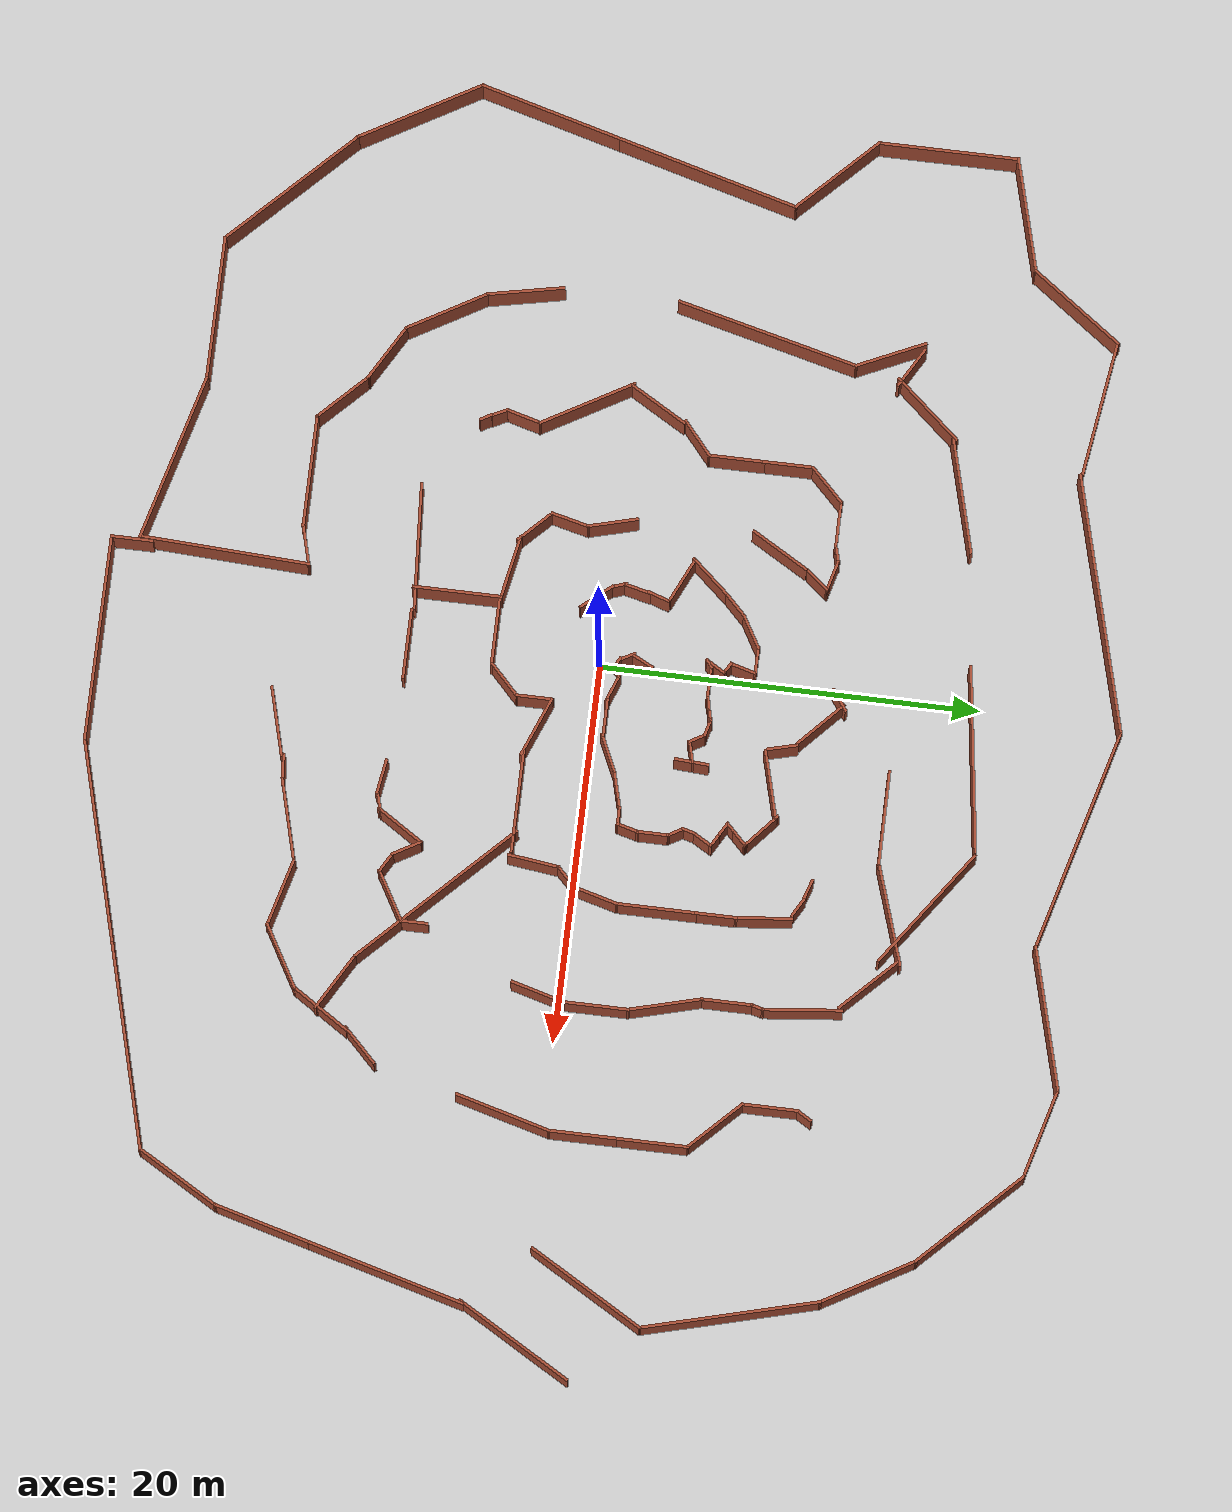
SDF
<sdf version="1.6">
 <world name="indoor4">
  <plugin name="gz::sim::systems::Physics" filename="gz-sim-physics-system"/>
  <plugin name="gz::sim::systems::UserCommands" filename="gz-sim-user-commands-system"/>
  <plugin name="gz::sim::systems::SceneBroadcaster" filename="gz-sim-scene-broadcaster-system"/>
  <plugin name="gz::sim::systems::Contact" filename="gz-sim-contact-system"/>
  <plugin name="gz::sim::systems::Imu" filename="gz-sim-imu-system"/>
  <plugin name="gz::sim::systems::AirPressure" filename="gz-sim-air-pressure-system"/>
  <plugin name="gz::sim::systems::ApplyLinkWrench" filename="gz-sim-apply-link-wrench-system"/>
  <plugin name="gz::sim::systems::NavSat" filename="gz-sim-navsat-system"/>
  <plugin name="gz::sim::systems::Sensors" filename="gz-sim-sensors-system">
   <render_engine>ogre2</render_engine>
  </plugin>
  <light name="sun" type="directional">
   <pose>0 0 10 0 -0 0</pose>
   <diffuse>0.8 0.8 0.8 1</diffuse>
   <specular>0.2 0.2 0.2 1</specular>
   <attenuation>
    <range>1000</range>
    <constant>0.9</constant>
    <linear>0.01</linear>
    <quadratic>0.001</quadratic>
   </attenuation>
   <direction>-0.5 0.1 -0.9</direction>
  </light>
  <model name="ground_plane">
   <static>1</static>
   <link name="link">
    <collision name="collision">
     <geometry><plane><normal>0 0 1</normal><size>100 100</size></plane></geometry>
     <friction><ode><mu>100</mu><mu2>50</mu2></ode></friction>
    </collision>
    <visual name="visual">
     <cast_shadows>0</cast_shadows>
     <geometry><plane><normal>0 0 1</normal><size>100 100</size></plane></geometry>
     <material>
      <script><uri>file://media/materials/scripts/gazebo.material</uri><name>Gazebo/Grey</name></script>
     </material>
    </visual>
   </link>
  </model>
  <gravity>0 0 -9.8</gravity>
  <magnetic_field>6e-06 2.3e-05 -4.2e-05</magnetic_field>
  <atmosphere type="adiabatic"/>
  <physics name="default_physics" default="0" type="ode">
   <max_step_size>0.004</max_step_size>
   <real_time_factor>1</real_time_factor>
   <real_time_update_rate>250</real_time_update_rate>
  </physics>
  <scene><ambient>0.4 0.4 0.4 1</ambient><background>0.7 0.7 0.7 1</background><shadows>1</shadows></scene>
  <spherical_coordinates>
   <surface_model>EARTH_WGS84</surface_model>
   <latitude_deg>0</latitude_deg>
   <longitude_deg>0</longitude_deg>
   <elevation>0</elevation>
   <heading_deg>0</heading_deg>
  </spherical_coordinates>
  <model name="Untitled1111">
   <link name="Wall_0">
    <pose>-5.60346 -1.19188 0 0 -0 2.26915</pose>
    <visual name="Wall_0_Visual">
     <pose>0 0 1.25 0 -0 0</pose>
     <geometry><box><size>2.13585 0.15 2.5</size></box></geometry>
     <material>
      <script><uri>file://media/materials/scripts/gazebo.material</uri><name>Gazebo/Bricks</name></script>
      <ambient>1 1 1 1</ambient>
      <shader type="pixel"/>
     </material>
     <meta><layer>0</layer></meta>
    </visual>
    <collision name="Wall_0_Collision">
     <pose>0 0 1.25 0 -0 0</pose>
     <geometry><box><size>2.13585 0.15 2.5</size></box></geometry>
     <friction>
      <ode><mu>1</mu><mu2>1</mu2><fdir1>0 0 0</fdir1><slip1>0</slip1><slip2>0</slip2></ode>
      <torsional>
       <coefficient>1</coefficient>
       <patch_radius>0</patch_radius>
       <surface_radius>0</surface_radius>
       <use_patch_radius>1</use_patch_radius>
       <ode><slip>0</slip></ode>
      </torsional>
     </friction>
     <bounce><restitution_coefficient>0</restitution_coefficient><threshold>1e+06</threshold></bounce>
     <contact>
      <collide_without_contact>0</collide_without_contact>
      <collide_without_contact_bitmask>1</collide_without_contact_bitmask>
      <collide_bitmask>1</collide_bitmask>
      <ode>
       <soft_cfm>0</soft_cfm>
       <soft_erp>0.2</soft_erp>
       <kp>1e+13</kp>
       <kd>1</kd>
       <max_vel>0.01</max_vel>
       <min_depth>0</min_depth>
      </ode>
      <bullet>
       <split_impulse>1</split_impulse>
       <split_impulse_penetration_threshold>-0.01</split_impulse_penetration_threshold>
       <soft_cfm>0</soft_cfm>
       <soft_erp>0.2</soft_erp>
       <kp>1e+13</kp>
       <kd>1</kd>
      </bullet>
     </contact>
    </collision>
   </link>
   <link name="Wall_1">
    <pose>-6.35977 -0.045403 0 0 -0 1.91127</pose>
    <visual name="Wall_1_Visual">
     <pose>0 0 1.25 0 -0 0</pose>
     <geometry><box><size>0.856129 0.15 2.5</size></box></geometry>
     <material>
      <script><uri>file://media/materials/scripts/gazebo.material</uri><name>Gazebo/Bricks</name></script>
      <ambient>1 1 1 1</ambient>
      <shader type="pixel"/>
     </material>
     <meta><layer>0</layer></meta>
    </visual>
    <collision name="Wall_1_Collision">
     <pose>0 0 1.25 0 -0 0</pose>
     <geometry><box><size>0.856129 0.15 2.5</size></box></geometry>
     <friction>
      <ode><mu>1</mu><mu2>1</mu2><fdir1>0 0 0</fdir1><slip1>0</slip1><slip2>0</slip2></ode>
      <torsional>
       <coefficient>1</coefficient>
       <patch_radius>0</patch_radius>
       <surface_radius>0</surface_radius>
       <use_patch_radius>1</use_patch_radius>
       <ode><slip>0</slip></ode>
      </torsional>
     </friction>
     <bounce><restitution_coefficient>0</restitution_coefficient><threshold>1e+06</threshold></bounce>
     <contact>
      <collide_without_contact>0</collide_without_contact>
      <collide_without_contact_bitmask>1</collide_without_contact_bitmask>
      <collide_bitmask>1</collide_bitmask>
      <ode>
       <soft_cfm>0</soft_cfm>
       <soft_erp>0.2</soft_erp>
       <kp>1e+13</kp>
       <kd>1</kd>
       <max_vel>0.01</max_vel>
       <min_depth>0</min_depth>
      </ode>
      <bullet>
       <split_impulse>1</split_impulse>
       <split_impulse_penetration_threshold>-0.01</split_impulse_penetration_threshold>
       <soft_cfm>0</soft_cfm>
       <soft_erp>0.2</soft_erp>
       <kp>1e+13</kp>
       <kd>1</kd>
      </bullet>
     </contact>
    </collision>
   </link>
   <link name="Wall_10">
    <pose>-2.6358 6.01879 0 0 0 -0.523599</pose>
    <visual name="Wall_10_Visual">
     <pose>0 0 1.25 0 -0 0</pose>
     <geometry><box><size>0.75 0.15 2.5</size></box></geometry>
     <material>
      <script><uri>file://media/materials/scripts/gazebo.material</uri><name>Gazebo/Bricks</name></script>
      <ambient>1 1 1 1</ambient>
      <shader type="pixel"/>
     </material>
     <meta><layer>0</layer></meta>
    </visual>
    <collision name="Wall_10_Collision">
     <pose>0 0 1.25 0 -0 0</pose>
     <geometry><box><size>0.75 0.15 2.5</size></box></geometry>
     <friction>
      <ode><mu>1</mu><mu2>1</mu2><fdir1>0 0 0</fdir1><slip1>0</slip1><slip2>0</slip2></ode>
      <torsional>
       <coefficient>1</coefficient>
       <patch_radius>0</patch_radius>
       <surface_radius>0</surface_radius>
       <use_patch_radius>1</use_patch_radius>
       <ode><slip>0</slip></ode>
      </torsional>
     </friction>
     <bounce><restitution_coefficient>0</restitution_coefficient><threshold>1e+06</threshold></bounce>
     <contact>
      <collide_without_contact>0</collide_without_contact>
      <collide_without_contact_bitmask>1</collide_without_contact_bitmask>
      <collide_bitmask>1</collide_bitmask>
      <ode>
       <soft_cfm>0</soft_cfm>
       <soft_erp>0.2</soft_erp>
       <kp>1e+13</kp>
       <kd>1</kd>
       <max_vel>0.01</max_vel>
       <min_depth>0</min_depth>
      </ode>
      <bullet>
       <split_impulse>1</split_impulse>
       <split_impulse_penetration_threshold>-0.01</split_impulse_penetration_threshold>
       <soft_cfm>0</soft_cfm>
       <soft_erp>0.2</soft_erp>
       <kp>1e+13</kp>
       <kd>1</kd>
      </bullet>
     </contact>
    </collision>
   </link>
   <link name="Wall_102">
    <pose>15.4586 -1.70898 0 0 -0 1.309</pose>
    <visual name="Wall_102_Visual">
     <pose>0 0 1.25 0 -0 0</pose>
     <geometry><box><size>3 0.15 2.5</size></box></geometry>
     <material>
      <script><uri>file://media/materials/scripts/gazebo.material</uri><name>Gazebo/Bricks</name></script>
      <ambient>1 1 1 1</ambient>
      <shader type="pixel"/>
     </material>
     <meta><layer>0</layer></meta>
    </visual>
    <collision name="Wall_102_Collision">
     <pose>0 0 1.25 0 -0 0</pose>
     <geometry><box><size>3 0.15 2.5</size></box></geometry>
     <friction>
      <ode><mu>1</mu><mu2>1</mu2><fdir1>0 0 0</fdir1><slip1>0</slip1><slip2>0</slip2></ode>
      <torsional>
       <coefficient>1</coefficient>
       <patch_radius>0</patch_radius>
       <surface_radius>0</surface_radius>
       <use_patch_radius>1</use_patch_radius>
       <ode><slip>0</slip></ode>
      </torsional>
     </friction>
     <bounce><restitution_coefficient>0</restitution_coefficient><threshold>1e+06</threshold></bounce>
     <contact>
      <collide_without_contact>0</collide_without_contact>
      <collide_without_contact_bitmask>1</collide_without_contact_bitmask>
      <collide_bitmask>1</collide_bitmask>
      <ode>
       <soft_cfm>0</soft_cfm>
       <soft_erp>0.2</soft_erp>
       <kp>1e+13</kp>
       <kd>1</kd>
       <max_vel>0.01</max_vel>
       <min_depth>0</min_depth>
      </ode>
      <bullet>
       <split_impulse>1</split_impulse>
       <split_impulse_penetration_threshold>-0.01</split_impulse_penetration_threshold>
       <soft_cfm>0</soft_cfm>
       <soft_erp>0.2</soft_erp>
       <kp>1e+13</kp>
       <kd>1</kd>
      </bullet>
     </contact>
    </collision>
   </link>
   <link name="Wall_103">
    <pose>15.8274 1.34246 0 0 -0 1.5708</pose>
    <visual name="Wall_103_Visual">
     <pose>0 0 1.25 0 -0 0</pose>
     <geometry><box><size>3.5 0.15 2.5</size></box></geometry>
     <material>
      <script><uri>file://media/materials/scripts/gazebo.material</uri><name>Gazebo/Bricks</name></script>
      <ambient>1 1 1 1</ambient>
      <shader type="pixel"/>
     </material>
     <meta><layer>0</layer></meta>
    </visual>
    <collision name="Wall_103_Collision">
     <pose>0 0 1.25 0 -0 0</pose>
     <geometry><box><size>3.5 0.15 2.5</size></box></geometry>
     <friction>
      <ode><mu>1</mu><mu2>1</mu2><fdir1>0 0 0</fdir1><slip1>0</slip1><slip2>0</slip2></ode>
      <torsional>
       <coefficient>1</coefficient>
       <patch_radius>0</patch_radius>
       <surface_radius>0</surface_radius>
       <use_patch_radius>1</use_patch_radius>
       <ode><slip>0</slip></ode>
      </torsional>
     </friction>
     <bounce><restitution_coefficient>0</restitution_coefficient><threshold>1e+06</threshold></bounce>
     <contact>
      <collide_without_contact>0</collide_without_contact>
      <collide_without_contact_bitmask>1</collide_without_contact_bitmask>
      <collide_bitmask>1</collide_bitmask>
      <ode>
       <soft_cfm>0</soft_cfm>
       <soft_erp>0.2</soft_erp>
       <kp>1e+13</kp>
       <kd>1</kd>
       <max_vel>0.01</max_vel>
       <min_depth>0</min_depth>
      </ode>
      <bullet>
       <split_impulse>1</split_impulse>
       <split_impulse_penetration_threshold>-0.01</split_impulse_penetration_threshold>
       <soft_cfm>0</soft_cfm>
       <soft_erp>0.2</soft_erp>
       <kp>1e+13</kp>
       <kd>1</kd>
      </bullet>
     </contact>
    </collision>
   </link>
   <link name="Wall_104">
    <pose>15.3292 4.87687 0 0 -0 1.8326</pose>
    <visual name="Wall_104_Visual">
     <pose>0 0 1.25 0 -0 0</pose>
     <geometry><box><size>4 0.15 2.5</size></box></geometry>
     <material>
      <script><uri>file://media/materials/scripts/gazebo.material</uri><name>Gazebo/Bricks</name></script>
      <ambient>1 1 1 1</ambient>
      <shader type="pixel"/>
     </material>
     <meta><layer>0</layer></meta>
    </visual>
    <collision name="Wall_104_Collision">
     <pose>0 0 1.25 0 -0 0</pose>
     <geometry><box><size>4 0.15 2.5</size></box></geometry>
     <friction>
      <ode><mu>1</mu><mu2>1</mu2><fdir1>0 0 0</fdir1><slip1>0</slip1><slip2>0</slip2></ode>
      <torsional>
       <coefficient>1</coefficient>
       <patch_radius>0</patch_radius>
       <surface_radius>0</surface_radius>
       <use_patch_radius>1</use_patch_radius>
       <ode><slip>0</slip></ode>
      </torsional>
     </friction>
     <bounce><restitution_coefficient>0</restitution_coefficient><threshold>1e+06</threshold></bounce>
     <contact>
      <collide_without_contact>0</collide_without_contact>
      <collide_without_contact_bitmask>1</collide_without_contact_bitmask>
      <collide_bitmask>1</collide_bitmask>
      <ode>
       <soft_cfm>0</soft_cfm>
       <soft_erp>0.2</soft_erp>
       <kp>1e+13</kp>
       <kd>1</kd>
       <max_vel>0.01</max_vel>
       <min_depth>0</min_depth>
      </ode>
      <bullet>
       <split_impulse>1</split_impulse>
       <split_impulse_penetration_threshold>-0.01</split_impulse_penetration_threshold>
       <soft_cfm>0</soft_cfm>
       <soft_erp>0.2</soft_erp>
       <kp>1e+13</kp>
       <kd>1</kd>
      </bullet>
     </contact>
    </collision>
   </link>
   <link name="Wall_105">
    <pose>14.831 8.03628 0 0 -0 1.5708</pose>
    <visual name="Wall_105_Visual">
     <pose>0 0 1.25 0 -0 0</pose>
     <geometry><box><size>2.75 0.15 2.5</size></box></geometry>
     <material>
      <script><uri>file://media/materials/scripts/gazebo.material</uri><name>Gazebo/Bricks</name></script>
      <ambient>1 1 1 1</ambient>
      <shader type="pixel"/>
     </material>
     <meta><layer>0</layer></meta>
    </visual>
    <collision name="Wall_105_Collision">
     <pose>0 0 1.25 0 -0 0</pose>
     <geometry><box><size>2.75 0.15 2.5</size></box></geometry>
     <friction>
      <ode><mu>1</mu><mu2>1</mu2><fdir1>0 0 0</fdir1><slip1>0</slip1><slip2>0</slip2></ode>
      <torsional>
       <coefficient>1</coefficient>
       <patch_radius>0</patch_radius>
       <surface_radius>0</surface_radius>
       <use_patch_radius>1</use_patch_radius>
       <ode><slip>0</slip></ode>
      </torsional>
     </friction>
     <bounce><restitution_coefficient>0</restitution_coefficient><threshold>1e+06</threshold></bounce>
     <contact>
      <collide_without_contact>0</collide_without_contact>
      <collide_without_contact_bitmask>1</collide_without_contact_bitmask>
      <collide_bitmask>1</collide_bitmask>
      <ode>
       <soft_cfm>0</soft_cfm>
       <soft_erp>0.2</soft_erp>
       <kp>1e+13</kp>
       <kd>1</kd>
       <max_vel>0.01</max_vel>
       <min_depth>0</min_depth>
      </ode>
      <bullet>
       <split_impulse>1</split_impulse>
       <split_impulse_penetration_threshold>-0.01</split_impulse_penetration_threshold>
       <soft_cfm>0</soft_cfm>
       <soft_erp>0.2</soft_erp>
       <kp>1e+13</kp>
       <kd>1</kd>
      </bullet>
     </contact>
    </collision>
   </link>
   <link name="Wall_106">
    <pose>14.9086 9.62606 0 0 -0 1.309</pose>
    <visual name="Wall_106_Visual">
     <pose>0 0 1.25 0 -0 0</pose>
     <geometry><box><size>0.75 0.15 2.5</size></box></geometry>
     <material>
      <script><uri>file://media/materials/scripts/gazebo.material</uri><name>Gazebo/Bricks</name></script>
      <ambient>1 1 1 1</ambient>
      <shader type="pixel"/>
     </material>
     <meta><layer>0</layer></meta>
    </visual>
    <collision name="Wall_106_Collision">
     <pose>0 0 1.25 0 -0 0</pose>
     <geometry><box><size>0.75 0.15 2.5</size></box></geometry>
     <friction>
      <ode><mu>1</mu><mu2>1</mu2><fdir1>0 0 0</fdir1><slip1>0</slip1><slip2>0</slip2></ode>
      <torsional>
       <coefficient>1</coefficient>
       <patch_radius>0</patch_radius>
       <surface_radius>0</surface_radius>
       <use_patch_radius>1</use_patch_radius>
       <ode><slip>0</slip></ode>
      </torsional>
     </friction>
     <bounce><restitution_coefficient>0</restitution_coefficient><threshold>1e+06</threshold></bounce>
     <contact>
      <collide_without_contact>0</collide_without_contact>
      <collide_without_contact_bitmask>1</collide_without_contact_bitmask>
      <collide_bitmask>1</collide_bitmask>
      <ode>
       <soft_cfm>0</soft_cfm>
       <soft_erp>0.2</soft_erp>
       <kp>1e+13</kp>
       <kd>1</kd>
       <max_vel>0.01</max_vel>
       <min_depth>0</min_depth>
      </ode>
      <bullet>
       <split_impulse>1</split_impulse>
       <split_impulse_penetration_threshold>-0.01</split_impulse_penetration_threshold>
       <soft_cfm>0</soft_cfm>
       <soft_erp>0.2</soft_erp>
       <kp>1e+13</kp>
       <kd>1</kd>
      </bullet>
     </contact>
    </collision>
   </link>
   <link name="Wall_107">
    <pose>14.774 11.9399 0 0 -0 1.67529</pose>
    <visual name="Wall_107_Visual">
     <pose>0 0 1.25 0 -0 0</pose>
     <geometry><box><size>4.22037 0.15 2.5</size></box></geometry>
     <material>
      <script><uri>file://media/materials/scripts/gazebo.material</uri><name>Gazebo/Bricks</name></script>
      <ambient>1 1 1 1</ambient>
      <shader type="pixel"/>
     </material>
     <meta><layer>0</layer></meta>
    </visual>
    <collision name="Wall_107_Collision">
     <pose>0 0 1.25 0 -0 0</pose>
     <geometry><box><size>4.22037 0.15 2.5</size></box></geometry>
     <friction>
      <ode><mu>1</mu><mu2>1</mu2><fdir1>0 0 0</fdir1><slip1>0</slip1><slip2>0</slip2></ode>
      <torsional>
       <coefficient>1</coefficient>
       <patch_radius>0</patch_radius>
       <surface_radius>0</surface_radius>
       <use_patch_radius>1</use_patch_radius>
       <ode><slip>0</slip></ode>
      </torsional>
     </friction>
     <bounce><restitution_coefficient>0</restitution_coefficient><threshold>1e+06</threshold></bounce>
     <contact>
      <collide_without_contact>0</collide_without_contact>
      <collide_without_contact_bitmask>1</collide_without_contact_bitmask>
      <collide_bitmask>1</collide_bitmask>
      <ode>
       <soft_cfm>0</soft_cfm>
       <soft_erp>0.2</soft_erp>
       <kp>1e+13</kp>
       <kd>1</kd>
       <max_vel>0.01</max_vel>
       <min_depth>0</min_depth>
      </ode>
      <bullet>
       <split_impulse>1</split_impulse>
       <split_impulse_penetration_threshold>-0.01</split_impulse_penetration_threshold>
       <soft_cfm>0</soft_cfm>
       <soft_erp>0.2</soft_erp>
       <kp>1e+13</kp>
       <kd>1</kd>
      </bullet>
     </contact>
    </collision>
   </link>
   <link name="Wall_108">
    <pose>13.059 15.1837 0 0 -0 2.35619</pose>
    <visual name="Wall_108_Visual">
     <pose>0 0 1.25 0 -0 0</pose>
     <geometry><box><size>4 0.15 2.5</size></box></geometry>
     <material>
      <script><uri>file://media/materials/scripts/gazebo.material</uri><name>Gazebo/Bricks</name></script>
      <ambient>1 1 1 1</ambient>
      <shader type="pixel"/>
     </material>
     <meta><layer>0</layer></meta>
    </visual>
    <collision name="Wall_108_Collision">
     <pose>0 0 1.25 0 -0 0</pose>
     <geometry><box><size>4 0.15 2.5</size></box></geometry>
     <friction>
      <ode><mu>1</mu><mu2>1</mu2><fdir1>0 0 0</fdir1><slip1>0</slip1><slip2>0</slip2></ode>
      <torsional>
       <coefficient>1</coefficient>
       <patch_radius>0</patch_radius>
       <surface_radius>0</surface_radius>
       <use_patch_radius>1</use_patch_radius>
       <ode><slip>0</slip></ode>
      </torsional>
     </friction>
     <bounce><restitution_coefficient>0</restitution_coefficient><threshold>1e+06</threshold></bounce>
     <contact>
      <collide_without_contact>0</collide_without_contact>
      <collide_without_contact_bitmask>1</collide_without_contact_bitmask>
      <collide_bitmask>1</collide_bitmask>
      <ode>
       <soft_cfm>0</soft_cfm>
       <soft_erp>0.2</soft_erp>
       <kp>1e+13</kp>
       <kd>1</kd>
       <max_vel>0.01</max_vel>
       <min_depth>0</min_depth>
      </ode>
      <bullet>
       <split_impulse>1</split_impulse>
       <split_impulse_penetration_threshold>-0.01</split_impulse_penetration_threshold>
       <soft_cfm>0</soft_cfm>
       <soft_erp>0.2</soft_erp>
       <kp>1e+13</kp>
       <kd>1</kd>
      </bullet>
     </contact>
    </collision>
   </link>
   <link name="Wall_109">
    <pose>9.25161 15.8373 0 0 0 -2.82454</pose>
    <visual name="Wall_109_Visual">
     <pose>0 0 1.25 0 -0 0</pose>
     <geometry><box><size>5.59694 0.15 2.5</size></box></geometry>
     <material>
      <script><uri>file://media/materials/scripts/gazebo.material</uri><name>Gazebo/Bricks</name></script>
      <ambient>1 1 1 1</ambient>
      <shader type="pixel"/>
     </material>
     <meta><layer>0</layer></meta>
    </visual>
    <collision name="Wall_109_Collision">
     <pose>0 0 1.25 0 -0 0</pose>
     <geometry><box><size>5.59694 0.15 2.5</size></box></geometry>
     <friction>
      <ode><mu>1</mu><mu2>1</mu2><fdir1>0 0 0</fdir1><slip1>0</slip1><slip2>0</slip2></ode>
      <torsional>
       <coefficient>1</coefficient>
       <patch_radius>0</patch_radius>
       <surface_radius>0</surface_radius>
       <use_patch_radius>1</use_patch_radius>
       <ode><slip>0</slip></ode>
      </torsional>
     </friction>
     <bounce><restitution_coefficient>0</restitution_coefficient><threshold>1e+06</threshold></bounce>
     <contact>
      <collide_without_contact>0</collide_without_contact>
      <collide_without_contact_bitmask>1</collide_without_contact_bitmask>
      <collide_bitmask>1</collide_bitmask>
      <ode>
       <soft_cfm>0</soft_cfm>
       <soft_erp>0.2</soft_erp>
       <kp>1e+13</kp>
       <kd>1</kd>
       <max_vel>0.01</max_vel>
       <min_depth>0</min_depth>
      </ode>
      <bullet>
       <split_impulse>1</split_impulse>
       <split_impulse_penetration_threshold>-0.01</split_impulse_penetration_threshold>
       <soft_cfm>0</soft_cfm>
       <soft_erp>0.2</soft_erp>
       <kp>1e+13</kp>
       <kd>1</kd>
      </bullet>
     </contact>
    </collision>
   </link>
   <link name="Wall_11">
    <pose>-2.65099 5.39248 0 0 0 -2.0944</pose>
    <visual name="Wall_11_Visual">
     <pose>0 0 1.25 0 -0 0</pose>
     <geometry><box><size>1.25 0.15 2.5</size></box></geometry>
     <material>
      <script><uri>file://media/materials/scripts/gazebo.material</uri><name>Gazebo/Bricks</name></script>
      <ambient>1 1 1 1</ambient>
      <shader type="pixel"/>
     </material>
     <meta><layer>0</layer></meta>
    </visual>
    <collision name="Wall_11_Collision">
     <pose>0 0 1.25 0 -0 0</pose>
     <geometry><box><size>1.25 0.15 2.5</size></box></geometry>
     <friction>
      <ode><mu>1</mu><mu2>1</mu2><fdir1>0 0 0</fdir1><slip1>0</slip1><slip2>0</slip2></ode>
      <torsional>
       <coefficient>1</coefficient>
       <patch_radius>0</patch_radius>
       <surface_radius>0</surface_radius>
       <use_patch_radius>1</use_patch_radius>
       <ode><slip>0</slip></ode>
      </torsional>
     </friction>
     <bounce><restitution_coefficient>0</restitution_coefficient><threshold>1e+06</threshold></bounce>
     <contact>
      <collide_without_contact>0</collide_without_contact>
      <collide_without_contact_bitmask>1</collide_without_contact_bitmask>
      <collide_bitmask>1</collide_bitmask>
      <ode>
       <soft_cfm>0</soft_cfm>
       <soft_erp>0.2</soft_erp>
       <kp>1e+13</kp>
       <kd>1</kd>
       <max_vel>0.01</max_vel>
       <min_depth>0</min_depth>
      </ode>
      <bullet>
       <split_impulse>1</split_impulse>
       <split_impulse_penetration_threshold>-0.01</split_impulse_penetration_threshold>
       <soft_cfm>0</soft_cfm>
       <soft_erp>0.2</soft_erp>
       <kp>1e+13</kp>
       <kd>1</kd>
      </bullet>
     </contact>
    </collision>
   </link>
   <link name="Wall_110">
    <pose>4.23888 14.9882 0 0 -0 3.14159</pose>
    <visual name="Wall_110_Visual">
     <pose>0 0 1.25 0 -0 0</pose>
     <geometry><box><size>5 0.15 2.5</size></box></geometry>
     <material>
      <script><uri>file://media/materials/scripts/gazebo.material</uri><name>Gazebo/Bricks</name></script>
      <ambient>1 1 1 1</ambient>
      <shader type="pixel"/>
     </material>
     <meta><layer>0</layer></meta>
    </visual>
    <collision name="Wall_110_Collision">
     <pose>0 0 1.25 0 -0 0</pose>
     <geometry><box><size>5 0.15 2.5</size></box></geometry>
     <friction>
      <ode><mu>1</mu><mu2>1</mu2><fdir1>0 0 0</fdir1><slip1>0</slip1><slip2>0</slip2></ode>
      <torsional>
       <coefficient>1</coefficient>
       <patch_radius>0</patch_radius>
       <surface_radius>0</surface_radius>
       <use_patch_radius>1</use_patch_radius>
       <ode><slip>0</slip></ode>
      </torsional>
     </friction>
     <bounce><restitution_coefficient>0</restitution_coefficient><threshold>1e+06</threshold></bounce>
     <contact>
      <collide_without_contact>0</collide_without_contact>
      <collide_without_contact_bitmask>1</collide_without_contact_bitmask>
      <collide_bitmask>1</collide_bitmask>
      <ode>
       <soft_cfm>0</soft_cfm>
       <soft_erp>0.2</soft_erp>
       <kp>1e+13</kp>
       <kd>1</kd>
       <max_vel>0.01</max_vel>
       <min_depth>0</min_depth>
      </ode>
      <bullet>
       <split_impulse>1</split_impulse>
       <split_impulse_penetration_threshold>-0.01</split_impulse_penetration_threshold>
       <soft_cfm>0</soft_cfm>
       <soft_erp>0.2</soft_erp>
       <kp>1e+13</kp>
       <kd>1</kd>
      </bullet>
     </contact>
    </collision>
   </link>
   <link name="Wall_112">
    <pose>-13.2085 17.0795 0 0 0 -2.87979</pose>
    <visual name="Wall_112_Visual">
     <pose>0 0 1.25 0 -0 0</pose>
     <geometry><box><size>6.25 0.15 2.5</size></box></geometry>
     <material>
      <script><uri>file://media/materials/scripts/gazebo.material</uri><name>Gazebo/Bricks</name></script>
      <ambient>1 1 1 1</ambient>
      <shader type="pixel"/>
     </material>
     <meta><layer>0</layer></meta>
    </visual>
    <collision name="Wall_112_Collision">
     <pose>0 0 1.25 0 -0 0</pose>
     <geometry><box><size>6.25 0.15 2.5</size></box></geometry>
     <friction>
      <ode><mu>1</mu><mu2>1</mu2><fdir1>0 0 0</fdir1><slip1>0</slip1><slip2>0</slip2></ode>
      <torsional>
       <coefficient>1</coefficient>
       <patch_radius>0</patch_radius>
       <surface_radius>0</surface_radius>
       <use_patch_radius>1</use_patch_radius>
       <ode><slip>0</slip></ode>
      </torsional>
     </friction>
     <bounce><restitution_coefficient>0</restitution_coefficient><threshold>1e+06</threshold></bounce>
     <contact>
      <collide_without_contact>0</collide_without_contact>
      <collide_without_contact_bitmask>1</collide_without_contact_bitmask>
      <collide_bitmask>1</collide_bitmask>
      <ode>
       <soft_cfm>0</soft_cfm>
       <soft_erp>0.2</soft_erp>
       <kp>1e+13</kp>
       <kd>1</kd>
       <max_vel>0.01</max_vel>
       <min_depth>0</min_depth>
      </ode>
      <bullet>
       <split_impulse>1</split_impulse>
       <split_impulse_penetration_threshold>-0.01</split_impulse_penetration_threshold>
       <soft_cfm>0</soft_cfm>
       <soft_erp>0.2</soft_erp>
       <kp>1e+13</kp>
       <kd>1</kd>
      </bullet>
     </contact>
    </collision>
   </link>
   <link name="Wall_113">
    <pose>-17.5992 14.7841 0 0 0 -2.28433</pose>
    <visual name="Wall_113_Visual">
     <pose>0 0 1.25 0 -0 0</pose>
     <geometry><box><size>4.56448 0.15 2.5</size></box></geometry>
     <material>
      <script><uri>file://media/materials/scripts/gazebo.material</uri><name>Gazebo/Bricks</name></script>
      <ambient>1 1 1 1</ambient>
      <shader type="pixel"/>
     </material>
     <meta><layer>0</layer></meta>
    </visual>
    <collision name="Wall_113_Collision">
     <pose>0 0 1.25 0 -0 0</pose>
     <geometry><box><size>4.56448 0.15 2.5</size></box></geometry>
     <friction>
      <ode><mu>1</mu><mu2>1</mu2><fdir1>0 0 0</fdir1><slip1>0</slip1><slip2>0</slip2></ode>
      <torsional>
       <coefficient>1</coefficient>
       <patch_radius>0</patch_radius>
       <surface_radius>0</surface_radius>
       <use_patch_radius>1</use_patch_radius>
       <ode><slip>0</slip></ode>
      </torsional>
     </friction>
     <bounce><restitution_coefficient>0</restitution_coefficient><threshold>1e+06</threshold></bounce>
     <contact>
      <collide_without_contact>0</collide_without_contact>
      <collide_without_contact_bitmask>1</collide_without_contact_bitmask>
      <collide_bitmask>1</collide_bitmask>
      <ode>
       <soft_cfm>0</soft_cfm>
       <soft_erp>0.2</soft_erp>
       <kp>1e+13</kp>
       <kd>1</kd>
       <max_vel>0.01</max_vel>
       <min_depth>0</min_depth>
      </ode>
      <bullet>
       <split_impulse>1</split_impulse>
       <split_impulse_penetration_threshold>-0.01</split_impulse_penetration_threshold>
       <soft_cfm>0</soft_cfm>
       <soft_erp>0.2</soft_erp>
       <kp>1e+13</kp>
       <kd>1</kd>
      </bullet>
     </contact>
    </collision>
   </link>
   <link name="Wall_114">
    <pose>-19.736 13.7028 0 0 -0 2.61799</pose>
    <visual name="Wall_114_Visual">
     <pose>0 0 1.25 0 -0 0</pose>
     <geometry><box><size>2.5 0.15 2.5</size></box></geometry>
     <material>
      <script><uri>file://media/materials/scripts/gazebo.material</uri><name>Gazebo/Bricks</name></script>
      <ambient>1 1 1 1</ambient>
      <shader type="pixel"/>
     </material>
     <meta><layer>0</layer></meta>
    </visual>
    <collision name="Wall_114_Collision">
     <pose>0 0 1.25 0 -0 0</pose>
     <geometry><box><size>2.5 0.15 2.5</size></box></geometry>
     <friction>
      <ode><mu>1</mu><mu2>1</mu2><fdir1>0 0 0</fdir1><slip1>0</slip1><slip2>0</slip2></ode>
      <torsional>
       <coefficient>1</coefficient>
       <patch_radius>0</patch_radius>
       <surface_radius>0</surface_radius>
       <use_patch_radius>1</use_patch_radius>
       <ode><slip>0</slip></ode>
      </torsional>
     </friction>
     <bounce><restitution_coefficient>0</restitution_coefficient><threshold>1e+06</threshold></bounce>
     <contact>
      <collide_without_contact>0</collide_without_contact>
      <collide_without_contact_bitmask>1</collide_without_contact_bitmask>
      <collide_bitmask>1</collide_bitmask>
      <ode>
       <soft_cfm>0</soft_cfm>
       <soft_erp>0.2</soft_erp>
       <kp>1e+13</kp>
       <kd>1</kd>
       <max_vel>0.01</max_vel>
       <min_depth>0</min_depth>
      </ode>
      <bullet>
       <split_impulse>1</split_impulse>
       <split_impulse_penetration_threshold>-0.01</split_impulse_penetration_threshold>
       <soft_cfm>0</soft_cfm>
       <soft_erp>0.2</soft_erp>
       <kp>1e+13</kp>
       <kd>1</kd>
      </bullet>
     </contact>
    </collision>
   </link>
   <link name="Wall_115">
    <pose>-20.2762 12.5425 0 0 0 -1.14016</pose>
    <visual name="Wall_115_Visual">
     <pose>0 0 1.25 0 -0 0</pose>
     <geometry><box><size>3.99669 0.15 2.5</size></box></geometry>
     <material>
      <script><uri>file://media/materials/scripts/gazebo.material</uri><name>Gazebo/Bricks</name></script>
      <ambient>1 1 1 1</ambient>
      <shader type="pixel"/>
     </material>
     <meta><layer>0</layer></meta>
    </visual>
    <collision name="Wall_115_Collision">
     <pose>0 0 1.25 0 -0 0</pose>
     <geometry><box><size>3.99669 0.15 2.5</size></box></geometry>
     <friction>
      <ode><mu>1</mu><mu2>1</mu2><fdir1>0 0 0</fdir1><slip1>0</slip1><slip2>0</slip2></ode>
      <torsional>
       <coefficient>1</coefficient>
       <patch_radius>0</patch_radius>
       <surface_radius>0</surface_radius>
       <use_patch_radius>1</use_patch_radius>
       <ode><slip>0</slip></ode>
      </torsional>
     </friction>
     <bounce><restitution_coefficient>0</restitution_coefficient><threshold>1e+06</threshold></bounce>
     <contact>
      <collide_without_contact>0</collide_without_contact>
      <collide_without_contact_bitmask>1</collide_without_contact_bitmask>
      <collide_bitmask>1</collide_bitmask>
      <ode>
       <soft_cfm>0</soft_cfm>
       <soft_erp>0.2</soft_erp>
       <kp>1e+13</kp>
       <kd>1</kd>
       <max_vel>0.01</max_vel>
       <min_depth>0</min_depth>
      </ode>
      <bullet>
       <split_impulse>1</split_impulse>
       <split_impulse_penetration_threshold>-0.01</split_impulse_penetration_threshold>
       <soft_cfm>0</soft_cfm>
       <soft_erp>0.2</soft_erp>
       <kp>1e+13</kp>
       <kd>1</kd>
      </bullet>
     </contact>
    </collision>
   </link>
   <link name="Wall_116">
    <pose>-20.6372 6.01657 0 0 0 -1.80973</pose>
    <visual name="Wall_116_Visual">
     <pose>0 0 1.25 0 -0 0</pose>
     <geometry><box><size>9.98588 0.15 2.5</size></box></geometry>
     <material>
      <script><uri>file://media/materials/scripts/gazebo.material</uri><name>Gazebo/Bricks</name></script>
      <ambient>1 1 1 1</ambient>
      <shader type="pixel"/>
     </material>
     <meta><layer>0</layer></meta>
    </visual>
    <collision name="Wall_116_Collision">
     <pose>0 0 1.25 0 -0 0</pose>
     <geometry><box><size>9.98588 0.15 2.5</size></box></geometry>
     <friction>
      <ode><mu>1</mu><mu2>1</mu2><fdir1>0 0 0</fdir1><slip1>0</slip1><slip2>0</slip2></ode>
      <torsional>
       <coefficient>1</coefficient>
       <patch_radius>0</patch_radius>
       <surface_radius>0</surface_radius>
       <use_patch_radius>1</use_patch_radius>
       <ode><slip>0</slip></ode>
      </torsional>
     </friction>
     <bounce><restitution_coefficient>0</restitution_coefficient><threshold>1e+06</threshold></bounce>
     <contact>
      <collide_without_contact>0</collide_without_contact>
      <collide_without_contact_bitmask>1</collide_without_contact_bitmask>
      <collide_bitmask>1</collide_bitmask>
      <ode>
       <soft_cfm>0</soft_cfm>
       <soft_erp>0.2</soft_erp>
       <kp>1e+13</kp>
       <kd>1</kd>
       <max_vel>0.01</max_vel>
       <min_depth>0</min_depth>
      </ode>
      <bullet>
       <split_impulse>1</split_impulse>
       <split_impulse_penetration_threshold>-0.01</split_impulse_penetration_threshold>
       <soft_cfm>0</soft_cfm>
       <soft_erp>0.2</soft_erp>
       <kp>1e+13</kp>
       <kd>1</kd>
      </bullet>
     </contact>
    </collision>
   </link>
   <link name="Wall_118">
    <pose>-21.3942 -6.83376 0 0 0 -1.36735</pose>
    <visual name="Wall_118_Visual">
     <pose>0 0 1.25 0 -0 0</pose>
     <geometry><box><size>4.17727 0.15 2.5</size></box></geometry>
     <material>
      <script><uri>file://media/materials/scripts/gazebo.material</uri><name>Gazebo/Bricks</name></script>
      <ambient>1 1 1 1</ambient>
      <shader type="pixel"/>
     </material>
     <meta><layer>0</layer></meta>
    </visual>
    <collision name="Wall_118_Collision">
     <pose>0 0 1.25 0 -0 0</pose>
     <geometry><box><size>4.17727 0.15 2.5</size></box></geometry>
     <friction>
      <ode><mu>1</mu><mu2>1</mu2><fdir1>0 0 0</fdir1><slip1>0</slip1><slip2>0</slip2></ode>
      <torsional>
       <coefficient>1</coefficient>
       <patch_radius>0</patch_radius>
       <surface_radius>0</surface_radius>
       <use_patch_radius>1</use_patch_radius>
       <ode><slip>0</slip></ode>
      </torsional>
     </friction>
     <bounce><restitution_coefficient>0</restitution_coefficient><threshold>1e+06</threshold></bounce>
     <contact>
      <collide_without_contact>0</collide_without_contact>
      <collide_without_contact_bitmask>1</collide_without_contact_bitmask>
      <collide_bitmask>1</collide_bitmask>
      <ode>
       <soft_cfm>0</soft_cfm>
       <soft_erp>0.2</soft_erp>
       <kp>1e+13</kp>
       <kd>1</kd>
       <max_vel>0.01</max_vel>
       <min_depth>0</min_depth>
      </ode>
      <bullet>
       <split_impulse>1</split_impulse>
       <split_impulse_penetration_threshold>-0.01</split_impulse_penetration_threshold>
       <soft_cfm>0</soft_cfm>
       <soft_erp>0.2</soft_erp>
       <kp>1e+13</kp>
       <kd>1</kd>
      </bullet>
     </contact>
    </collision>
   </link>
   <link name="Wall_119">
    <pose>-19.8374 -10.7977 0 0 0 -1.0472</pose>
    <visual name="Wall_119_Visual">
     <pose>0 0 1.25 0 -0 0</pose>
     <geometry><box><size>4.75 0.15 2.5</size></box></geometry>
     <material>
      <script><uri>file://media/materials/scripts/gazebo.material</uri><name>Gazebo/Bricks</name></script>
      <ambient>1 1 1 1</ambient>
      <shader type="pixel"/>
     </material>
     <meta><layer>0</layer></meta>
    </visual>
    <collision name="Wall_119_Collision">
     <pose>0 0 1.25 0 -0 0</pose>
     <geometry><box><size>4.75 0.15 2.5</size></box></geometry>
     <friction>
      <ode><mu>1</mu><mu2>1</mu2><fdir1>0 0 0</fdir1><slip1>0</slip1><slip2>0</slip2></ode>
      <torsional>
       <coefficient>1</coefficient>
       <patch_radius>0</patch_radius>
       <surface_radius>0</surface_radius>
       <use_patch_radius>1</use_patch_radius>
       <ode><slip>0</slip></ode>
      </torsional>
     </friction>
     <bounce><restitution_coefficient>0</restitution_coefficient><threshold>1e+06</threshold></bounce>
     <contact>
      <collide_without_contact>0</collide_without_contact>
      <collide_without_contact_bitmask>1</collide_without_contact_bitmask>
      <collide_bitmask>1</collide_bitmask>
      <ode>
       <soft_cfm>0</soft_cfm>
       <soft_erp>0.2</soft_erp>
       <kp>1e+13</kp>
       <kd>1</kd>
       <max_vel>0.01</max_vel>
       <min_depth>0</min_depth>
      </ode>
      <bullet>
       <split_impulse>1</split_impulse>
       <split_impulse_penetration_threshold>-0.01</split_impulse_penetration_threshold>
       <soft_cfm>0</soft_cfm>
       <soft_erp>0.2</soft_erp>
       <kp>1e+13</kp>
       <kd>1</kd>
      </bullet>
     </contact>
    </collision>
   </link>
   <link name="Wall_12">
    <pose>-2.75032 5.05347 0 0 -0 0.663411</pose>
    <visual name="Wall_12_Visual">
     <pose>0 0 1.25 0 -0 0</pose>
     <geometry><box><size>0.595922 0.15 2.5</size></box></geometry>
     <material>
      <script><uri>file://media/materials/scripts/gazebo.material</uri><name>Gazebo/Bricks</name></script>
      <ambient>1 1 1 1</ambient>
      <shader type="pixel"/>
     </material>
     <meta><layer>0</layer></meta>
    </visual>
    <collision name="Wall_12_Collision">
     <pose>0 0 1.25 0 -0 0</pose>
     <geometry><box><size>0.595922 0.15 2.5</size></box></geometry>
     <friction>
      <ode><mu>1</mu><mu2>1</mu2><fdir1>0 0 0</fdir1><slip1>0</slip1><slip2>0</slip2></ode>
      <torsional>
       <coefficient>1</coefficient>
       <patch_radius>0</patch_radius>
       <surface_radius>0</surface_radius>
       <use_patch_radius>1</use_patch_radius>
       <ode><slip>0</slip></ode>
      </torsional>
     </friction>
     <bounce><restitution_coefficient>0</restitution_coefficient><threshold>1e+06</threshold></bounce>
     <contact>
      <collide_without_contact>0</collide_without_contact>
      <collide_without_contact_bitmask>1</collide_without_contact_bitmask>
      <collide_bitmask>1</collide_bitmask>
      <ode>
       <soft_cfm>0</soft_cfm>
       <soft_erp>0.2</soft_erp>
       <kp>1e+13</kp>
       <kd>1</kd>
       <max_vel>0.01</max_vel>
       <min_depth>0</min_depth>
      </ode>
      <bullet>
       <split_impulse>1</split_impulse>
       <split_impulse_penetration_threshold>-0.01</split_impulse_penetration_threshold>
       <soft_cfm>0</soft_cfm>
       <soft_erp>0.2</soft_erp>
       <kp>1e+13</kp>
       <kd>1</kd>
      </bullet>
     </contact>
    </collision>
   </link>
   <link name="Wall_120">
    <pose>-17.2368 -13.6271 0 0 0 -0.523599</pose>
    <visual name="Wall_120_Visual">
     <pose>0 0 1.25 0 -0 0</pose>
     <geometry><box><size>3.5 0.15 2.5</size></box></geometry>
     <material>
      <script><uri>file://media/materials/scripts/gazebo.material</uri><name>Gazebo/Bricks</name></script>
      <ambient>1 1 1 1</ambient>
      <shader type="pixel"/>
     </material>
     <meta><layer>0</layer></meta>
    </visual>
    <collision name="Wall_120_Collision">
     <pose>0 0 1.25 0 -0 0</pose>
     <geometry><box><size>3.5 0.15 2.5</size></box></geometry>
     <friction>
      <ode><mu>1</mu><mu2>1</mu2><fdir1>0 0 0</fdir1><slip1>0</slip1><slip2>0</slip2></ode>
      <torsional>
       <coefficient>1</coefficient>
       <patch_radius>0</patch_radius>
       <surface_radius>0</surface_radius>
       <use_patch_radius>1</use_patch_radius>
       <ode><slip>0</slip></ode>
      </torsional>
     </friction>
     <bounce><restitution_coefficient>0</restitution_coefficient><threshold>1e+06</threshold></bounce>
     <contact>
      <collide_without_contact>0</collide_without_contact>
      <collide_without_contact_bitmask>1</collide_without_contact_bitmask>
      <collide_bitmask>1</collide_bitmask>
      <ode>
       <soft_cfm>0</soft_cfm>
       <soft_erp>0.2</soft_erp>
       <kp>1e+13</kp>
       <kd>1</kd>
       <max_vel>0.01</max_vel>
       <min_depth>0</min_depth>
      </ode>
      <bullet>
       <split_impulse>1</split_impulse>
       <split_impulse_penetration_threshold>-0.01</split_impulse_penetration_threshold>
       <soft_cfm>0</soft_cfm>
       <soft_erp>0.2</soft_erp>
       <kp>1e+13</kp>
       <kd>1</kd>
      </bullet>
     </contact>
    </collision>
   </link>
   <link name="Wall_121">
    <pose>-14.6018 -15.649 0 0 0 -0.785398</pose>
    <visual name="Wall_121_Visual">
     <pose>0 0 1.25 0 -0 0</pose>
     <geometry><box><size>3.5 0.15 2.5</size></box></geometry>
     <material>
      <script><uri>file://media/materials/scripts/gazebo.material</uri><name>Gazebo/Bricks</name></script>
      <ambient>1 1 1 1</ambient>
      <shader type="pixel"/>
     </material>
     <meta><layer>0</layer></meta>
    </visual>
    <collision name="Wall_121_Collision">
     <pose>0 0 1.25 0 -0 0</pose>
     <geometry><box><size>3.5 0.15 2.5</size></box></geometry>
     <friction>
      <ode><mu>1</mu><mu2>1</mu2><fdir1>0 0 0</fdir1><slip1>0</slip1><slip2>0</slip2></ode>
      <torsional>
       <coefficient>1</coefficient>
       <patch_radius>0</patch_radius>
       <surface_radius>0</surface_radius>
       <use_patch_radius>1</use_patch_radius>
       <ode><slip>0</slip></ode>
      </torsional>
     </friction>
     <bounce><restitution_coefficient>0</restitution_coefficient><threshold>1e+06</threshold></bounce>
     <contact>
      <collide_without_contact>0</collide_without_contact>
      <collide_without_contact_bitmask>1</collide_without_contact_bitmask>
      <collide_bitmask>1</collide_bitmask>
      <ode>
       <soft_cfm>0</soft_cfm>
       <soft_erp>0.2</soft_erp>
       <kp>1e+13</kp>
       <kd>1</kd>
       <max_vel>0.01</max_vel>
       <min_depth>0</min_depth>
      </ode>
      <bullet>
       <split_impulse>1</split_impulse>
       <split_impulse_penetration_threshold>-0.01</split_impulse_penetration_threshold>
       <soft_cfm>0</soft_cfm>
       <soft_erp>0.2</soft_erp>
       <kp>1e+13</kp>
       <kd>1</kd>
      </bullet>
     </contact>
    </collision>
   </link>
   <link name="Wall_122">
    <pose>-10.4924 -16.8334 0 0 -0 0</pose>
    <visual name="Wall_122_Visual">
     <pose>0 0 1.25 0 -0 0</pose>
     <geometry><box><size>6 0.15 2.5</size></box></geometry>
     <material>
      <script><uri>file://media/materials/scripts/gazebo.material</uri><name>Gazebo/Bricks</name></script>
      <ambient>1 1 1 1</ambient>
      <shader type="pixel"/>
     </material>
     <meta><layer>0</layer></meta>
    </visual>
    <collision name="Wall_122_Collision">
     <pose>0 0 1.25 0 -0 0</pose>
     <geometry><box><size>6 0.15 2.5</size></box></geometry>
     <friction>
      <ode><mu>1</mu><mu2>1</mu2><fdir1>0 0 0</fdir1><slip1>0</slip1><slip2>0</slip2></ode>
      <torsional>
       <coefficient>1</coefficient>
       <patch_radius>0</patch_radius>
       <surface_radius>0</surface_radius>
       <use_patch_radius>1</use_patch_radius>
       <ode><slip>0</slip></ode>
      </torsional>
     </friction>
     <bounce><restitution_coefficient>0</restitution_coefficient><threshold>1e+06</threshold></bounce>
     <contact>
      <collide_without_contact>0</collide_without_contact>
      <collide_without_contact_bitmask>1</collide_without_contact_bitmask>
      <collide_bitmask>1</collide_bitmask>
      <ode>
       <soft_cfm>0</soft_cfm>
       <soft_erp>0.2</soft_erp>
       <kp>1e+13</kp>
       <kd>1</kd>
       <max_vel>0.01</max_vel>
       <min_depth>0</min_depth>
      </ode>
      <bullet>
       <split_impulse>1</split_impulse>
       <split_impulse_penetration_threshold>-0.01</split_impulse_penetration_threshold>
       <soft_cfm>0</soft_cfm>
       <soft_erp>0.2</soft_erp>
       <kp>1e+13</kp>
       <kd>1</kd>
      </bullet>
     </contact>
    </collision>
   </link>
   <link name="Wall_123">
    <pose>-6.55315 -16.5616 0 0 -0 0.261799</pose>
    <visual name="Wall_123_Visual">
     <pose>0 0 1.25 0 -0 0</pose>
     <geometry><box><size>2.25 0.15 2.5</size></box></geometry>
     <material>
      <script><uri>file://media/materials/scripts/gazebo.material</uri><name>Gazebo/Bricks</name></script>
      <ambient>1 1 1 1</ambient>
      <shader type="pixel"/>
     </material>
     <meta><layer>0</layer></meta>
    </visual>
    <collision name="Wall_123_Collision">
     <pose>0 0 1.25 0 -0 0</pose>
     <geometry><box><size>2.25 0.15 2.5</size></box></geometry>
     <friction>
      <ode><mu>1</mu><mu2>1</mu2><fdir1>0 0 0</fdir1><slip1>0</slip1><slip2>0</slip2></ode>
      <torsional>
       <coefficient>1</coefficient>
       <patch_radius>0</patch_radius>
       <surface_radius>0</surface_radius>
       <use_patch_radius>1</use_patch_radius>
       <ode><slip>0</slip></ode>
      </torsional>
     </friction>
     <bounce><restitution_coefficient>0</restitution_coefficient><threshold>1e+06</threshold></bounce>
     <contact>
      <collide_without_contact>0</collide_without_contact>
      <collide_without_contact_bitmask>1</collide_without_contact_bitmask>
      <collide_bitmask>1</collide_bitmask>
      <ode>
       <soft_cfm>0</soft_cfm>
       <soft_erp>0.2</soft_erp>
       <kp>1e+13</kp>
       <kd>1</kd>
       <max_vel>0.01</max_vel>
       <min_depth>0</min_depth>
      </ode>
      <bullet>
       <split_impulse>1</split_impulse>
       <split_impulse_penetration_threshold>-0.01</split_impulse_penetration_threshold>
       <soft_cfm>0</soft_cfm>
       <soft_erp>0.2</soft_erp>
       <kp>1e+13</kp>
       <kd>1</kd>
      </bullet>
     </contact>
    </collision>
   </link>
   <link name="Wall_125">
    <pose>2.93183 -16.8951 0 0 -0 0.261799</pose>
    <visual name="Wall_125_Visual">
     <pose>0 0 1.25 0 -0 0</pose>
     <geometry><box><size>3.75 0.15 2.5</size></box></geometry>
     <material>
      <script><uri>file://media/materials/scripts/gazebo.material</uri><name>Gazebo/Bricks</name></script>
      <ambient>1 1 1 1</ambient>
      <shader type="pixel"/>
     </material>
     <meta><layer>0</layer></meta>
    </visual>
    <collision name="Wall_125_Collision">
     <pose>0 0 1.25 0 -0 0</pose>
     <geometry><box><size>3.75 0.15 2.5</size></box></geometry>
     <friction>
      <ode><mu>1</mu><mu2>1</mu2><fdir1>0 0 0</fdir1><slip1>0</slip1><slip2>0</slip2></ode>
      <torsional>
       <coefficient>1</coefficient>
       <patch_radius>0</patch_radius>
       <surface_radius>0</surface_radius>
       <use_patch_radius>1</use_patch_radius>
       <ode><slip>0</slip></ode>
      </torsional>
     </friction>
     <bounce><restitution_coefficient>0</restitution_coefficient><threshold>1e+06</threshold></bounce>
     <contact>
      <collide_without_contact>0</collide_without_contact>
      <collide_without_contact_bitmask>1</collide_without_contact_bitmask>
      <collide_bitmask>1</collide_bitmask>
      <ode>
       <soft_cfm>0</soft_cfm>
       <soft_erp>0.2</soft_erp>
       <kp>1e+13</kp>
       <kd>1</kd>
       <max_vel>0.01</max_vel>
       <min_depth>0</min_depth>
      </ode>
      <bullet>
       <split_impulse>1</split_impulse>
       <split_impulse_penetration_threshold>-0.01</split_impulse_penetration_threshold>
       <soft_cfm>0</soft_cfm>
       <soft_erp>0.2</soft_erp>
       <kp>1e+13</kp>
       <kd>1</kd>
      </bullet>
     </contact>
    </collision>
   </link>
   <link name="Wall_126">
    <pose>5.30143 -16.2622 0 0 -0 0.070665</pose>
    <visual name="Wall_126_Visual">
     <pose>0 0 1.25 0 -0 0</pose>
     <geometry><box><size>1.41503 0.15 2.5</size></box></geometry>
     <material>
      <script><uri>file://media/materials/scripts/gazebo.material</uri><name>Gazebo/Bricks</name></script>
      <ambient>1 1 1 1</ambient>
      <shader type="pixel"/>
     </material>
     <meta><layer>0</layer></meta>
    </visual>
    <collision name="Wall_126_Collision">
     <pose>0 0 1.25 0 -0 0</pose>
     <geometry><box><size>1.41503 0.15 2.5</size></box></geometry>
     <friction>
      <ode><mu>1</mu><mu2>1</mu2><fdir1>0 0 0</fdir1><slip1>0</slip1><slip2>0</slip2></ode>
      <torsional>
       <coefficient>1</coefficient>
       <patch_radius>0</patch_radius>
       <surface_radius>0</surface_radius>
       <use_patch_radius>1</use_patch_radius>
       <ode><slip>0</slip></ode>
      </torsional>
     </friction>
     <bounce><restitution_coefficient>0</restitution_coefficient><threshold>1e+06</threshold></bounce>
     <contact>
      <collide_without_contact>0</collide_without_contact>
      <collide_without_contact_bitmask>1</collide_without_contact_bitmask>
      <collide_bitmask>1</collide_bitmask>
      <ode>
       <soft_cfm>0</soft_cfm>
       <soft_erp>0.2</soft_erp>
       <kp>1e+13</kp>
       <kd>1</kd>
       <max_vel>0.01</max_vel>
       <min_depth>0</min_depth>
      </ode>
      <bullet>
       <split_impulse>1</split_impulse>
       <split_impulse_penetration_threshold>-0.01</split_impulse_penetration_threshold>
       <soft_cfm>0</soft_cfm>
       <soft_erp>0.2</soft_erp>
       <kp>1e+13</kp>
       <kd>1</kd>
      </bullet>
     </contact>
    </collision>
   </link>
   <link name="Wall_127">
    <pose>8.03326 -15.6546 0 0 -0 0.261799</pose>
    <visual name="Wall_127_Visual">
     <pose>0 0 1.25 0 -0 0</pose>
     <geometry><box><size>4.5 0.15 2.5</size></box></geometry>
     <material>
      <script><uri>file://media/materials/scripts/gazebo.material</uri><name>Gazebo/Bricks</name></script>
      <ambient>1 1 1 1</ambient>
      <shader type="pixel"/>
     </material>
     <meta><layer>0</layer></meta>
    </visual>
    <collision name="Wall_127_Collision">
     <pose>0 0 1.25 0 -0 0</pose>
     <geometry><box><size>4.5 0.15 2.5</size></box></geometry>
     <friction>
      <ode><mu>1</mu><mu2>1</mu2><fdir1>0 0 0</fdir1><slip1>0</slip1><slip2>0</slip2></ode>
      <torsional>
       <coefficient>1</coefficient>
       <patch_radius>0</patch_radius>
       <surface_radius>0</surface_radius>
       <use_patch_radius>1</use_patch_radius>
       <ode><slip>0</slip></ode>
      </torsional>
     </friction>
     <bounce><restitution_coefficient>0</restitution_coefficient><threshold>1e+06</threshold></bounce>
     <contact>
      <collide_without_contact>0</collide_without_contact>
      <collide_without_contact_bitmask>1</collide_without_contact_bitmask>
      <collide_bitmask>1</collide_bitmask>
      <ode>
       <soft_cfm>0</soft_cfm>
       <soft_erp>0.2</soft_erp>
       <kp>1e+13</kp>
       <kd>1</kd>
       <max_vel>0.01</max_vel>
       <min_depth>0</min_depth>
      </ode>
      <bullet>
       <split_impulse>1</split_impulse>
       <split_impulse_penetration_threshold>-0.01</split_impulse_penetration_threshold>
       <soft_cfm>0</soft_cfm>
       <soft_erp>0.2</soft_erp>
       <kp>1e+13</kp>
       <kd>1</kd>
      </bullet>
     </contact>
    </collision>
   </link>
   <link name="Wall_128">
    <pose>11.8728 -15.5576 0 0 0 -0.261799</pose>
    <visual name="Wall_128_Visual">
     <pose>0 0 1.25 0 -0 0</pose>
     <geometry><box><size>3.75 0.15 2.5</size></box></geometry>
     <material>
      <script><uri>file://media/materials/scripts/gazebo.material</uri><name>Gazebo/Bricks</name></script>
      <ambient>1 1 1 1</ambient>
      <shader type="pixel"/>
     </material>
     <meta><layer>0</layer></meta>
    </visual>
    <collision name="Wall_128_Collision">
     <pose>0 0 1.25 0 -0 0</pose>
     <geometry><box><size>3.75 0.15 2.5</size></box></geometry>
     <friction>
      <ode><mu>1</mu><mu2>1</mu2><fdir1>0 0 0</fdir1><slip1>0</slip1><slip2>0</slip2></ode>
      <torsional>
       <coefficient>1</coefficient>
       <patch_radius>0</patch_radius>
       <surface_radius>0</surface_radius>
       <use_patch_radius>1</use_patch_radius>
       <ode><slip>0</slip></ode>
      </torsional>
     </friction>
     <bounce><restitution_coefficient>0</restitution_coefficient><threshold>1e+06</threshold></bounce>
     <contact>
      <collide_without_contact>0</collide_without_contact>
      <collide_without_contact_bitmask>1</collide_without_contact_bitmask>
      <collide_bitmask>1</collide_bitmask>
      <ode>
       <soft_cfm>0</soft_cfm>
       <soft_erp>0.2</soft_erp>
       <kp>1e+13</kp>
       <kd>1</kd>
       <max_vel>0.01</max_vel>
       <min_depth>0</min_depth>
      </ode>
      <bullet>
       <split_impulse>1</split_impulse>
       <split_impulse_penetration_threshold>-0.01</split_impulse_penetration_threshold>
       <soft_cfm>0</soft_cfm>
       <soft_erp>0.2</soft_erp>
       <kp>1e+13</kp>
       <kd>1</kd>
      </bullet>
     </contact>
    </collision>
   </link>
   <link name="Wall_129">
    <pose>15.1703 -15.1234 0 0 -0 0.523599</pose>
    <visual name="Wall_129_Visual">
     <pose>0 0 1.25 0 -0 0</pose>
     <geometry><box><size>3.75 0.15 2.5</size></box></geometry>
     <material>
      <script><uri>file://media/materials/scripts/gazebo.material</uri><name>Gazebo/Bricks</name></script>
      <ambient>1 1 1 1</ambient>
      <shader type="pixel"/>
     </material>
     <meta><layer>0</layer></meta>
    </visual>
    <collision name="Wall_129_Collision">
     <pose>0 0 1.25 0 -0 0</pose>
     <geometry><box><size>3.75 0.15 2.5</size></box></geometry>
     <friction>
      <ode><mu>1</mu><mu2>1</mu2><fdir1>0 0 0</fdir1><slip1>0</slip1><slip2>0</slip2></ode>
      <torsional>
       <coefficient>1</coefficient>
       <patch_radius>0</patch_radius>
       <surface_radius>0</surface_radius>
       <use_patch_radius>1</use_patch_radius>
       <ode><slip>0</slip></ode>
      </torsional>
     </friction>
     <bounce><restitution_coefficient>0</restitution_coefficient><threshold>1e+06</threshold></bounce>
     <contact>
      <collide_without_contact>0</collide_without_contact>
      <collide_without_contact_bitmask>1</collide_without_contact_bitmask>
      <collide_bitmask>1</collide_bitmask>
      <ode>
       <soft_cfm>0</soft_cfm>
       <soft_erp>0.2</soft_erp>
       <kp>1e+13</kp>
       <kd>1</kd>
       <max_vel>0.01</max_vel>
       <min_depth>0</min_depth>
      </ode>
      <bullet>
       <split_impulse>1</split_impulse>
       <split_impulse_penetration_threshold>-0.01</split_impulse_penetration_threshold>
       <soft_cfm>0</soft_cfm>
       <soft_erp>0.2</soft_erp>
       <kp>1e+13</kp>
       <kd>1</kd>
      </bullet>
     </contact>
    </collision>
   </link>
   <link name="Wall_13">
    <pose>-1.73967 5.15579 0 0 -0 0</pose>
    <visual name="Wall_13_Visual">
     <pose>0 0 1.25 0 -0 0</pose>
     <geometry><box><size>1.75 0.15 2.5</size></box></geometry>
     <material>
      <script><uri>file://media/materials/scripts/gazebo.material</uri><name>Gazebo/Bricks</name></script>
      <ambient>1 1 1 1</ambient>
      <shader type="pixel"/>
     </material>
     <meta><layer>0</layer></meta>
    </visual>
    <collision name="Wall_13_Collision">
     <pose>0 0 1.25 0 -0 0</pose>
     <geometry><box><size>1.75 0.15 2.5</size></box></geometry>
     <friction>
      <ode><mu>1</mu><mu2>1</mu2><fdir1>0 0 0</fdir1><slip1>0</slip1><slip2>0</slip2></ode>
      <torsional>
       <coefficient>1</coefficient>
       <patch_radius>0</patch_radius>
       <surface_radius>0</surface_radius>
       <use_patch_radius>1</use_patch_radius>
       <ode><slip>0</slip></ode>
      </torsional>
     </friction>
     <bounce><restitution_coefficient>0</restitution_coefficient><threshold>1e+06</threshold></bounce>
     <contact>
      <collide_without_contact>0</collide_without_contact>
      <collide_without_contact_bitmask>1</collide_without_contact_bitmask>
      <collide_bitmask>1</collide_bitmask>
      <ode>
       <soft_cfm>0</soft_cfm>
       <soft_erp>0.2</soft_erp>
       <kp>1e+13</kp>
       <kd>1</kd>
       <max_vel>0.01</max_vel>
       <min_depth>0</min_depth>
      </ode>
      <bullet>
       <split_impulse>1</split_impulse>
       <split_impulse_penetration_threshold>-0.01</split_impulse_penetration_threshold>
       <soft_cfm>0</soft_cfm>
       <soft_erp>0.2</soft_erp>
       <kp>1e+13</kp>
       <kd>1</kd>
      </bullet>
     </contact>
    </collision>
   </link>
   <link name="Wall_130">
    <pose>17.6592 -12.7729 0 0 -0 1.00068</pose>
    <visual name="Wall_130_Visual">
     <pose>0 0 1.25 0 -0 0</pose>
     <geometry><box><size>3.59625 0.15 2.5</size></box></geometry>
     <material>
      <script><uri>file://media/materials/scripts/gazebo.material</uri><name>Gazebo/Bricks</name></script>
      <ambient>1 1 1 1</ambient>
      <shader type="pixel"/>
     </material>
     <meta><layer>0</layer></meta>
    </visual>
    <collision name="Wall_130_Collision">
     <pose>0 0 1.25 0 -0 0</pose>
     <geometry><box><size>3.59625 0.15 2.5</size></box></geometry>
     <friction>
      <ode><mu>1</mu><mu2>1</mu2><fdir1>0 0 0</fdir1><slip1>0</slip1><slip2>0</slip2></ode>
      <torsional>
       <coefficient>1</coefficient>
       <patch_radius>0</patch_radius>
       <surface_radius>0</surface_radius>
       <use_patch_radius>1</use_patch_radius>
       <ode><slip>0</slip></ode>
      </torsional>
     </friction>
     <bounce><restitution_coefficient>0</restitution_coefficient><threshold>1e+06</threshold></bounce>
     <contact>
      <collide_without_contact>0</collide_without_contact>
      <collide_without_contact_bitmask>1</collide_without_contact_bitmask>
      <collide_bitmask>1</collide_bitmask>
      <ode>
       <soft_cfm>0</soft_cfm>
       <soft_erp>0.2</soft_erp>
       <kp>1e+13</kp>
       <kd>1</kd>
       <max_vel>0.01</max_vel>
       <min_depth>0</min_depth>
      </ode>
      <bullet>
       <split_impulse>1</split_impulse>
       <split_impulse_penetration_threshold>-0.01</split_impulse_penetration_threshold>
       <soft_cfm>0</soft_cfm>
       <soft_erp>0.2</soft_erp>
       <kp>1e+13</kp>
       <kd>1</kd>
      </bullet>
     </contact>
    </collision>
   </link>
   <link name="Wall_131">
    <pose>19.3275 -10.4914 0 0 -0 0.785398</pose>
    <visual name="Wall_131_Visual">
     <pose>0 0 1.25 0 -0 0</pose>
     <geometry><box><size>2.5 0.15 2.5</size></box></geometry>
     <material>
      <script><uri>file://media/materials/scripts/gazebo.material</uri><name>Gazebo/Bricks</name></script>
      <ambient>1 1 1 1</ambient>
      <shader type="pixel"/>
     </material>
     <meta><layer>0</layer></meta>
    </visual>
    <collision name="Wall_131_Collision">
     <pose>0 0 1.25 0 -0 0</pose>
     <geometry><box><size>2.5 0.15 2.5</size></box></geometry>
     <friction>
      <ode><mu>1</mu><mu2>1</mu2><fdir1>0 0 0</fdir1><slip1>0</slip1><slip2>0</slip2></ode>
      <torsional>
       <coefficient>1</coefficient>
       <patch_radius>0</patch_radius>
       <surface_radius>0</surface_radius>
       <use_patch_radius>1</use_patch_radius>
       <ode><slip>0</slip></ode>
      </torsional>
     </friction>
     <bounce><restitution_coefficient>0</restitution_coefficient><threshold>1e+06</threshold></bounce>
     <contact>
      <collide_without_contact>0</collide_without_contact>
      <collide_without_contact_bitmask>1</collide_without_contact_bitmask>
      <collide_bitmask>1</collide_bitmask>
      <ode>
       <soft_cfm>0</soft_cfm>
       <soft_erp>0.2</soft_erp>
       <kp>1e+13</kp>
       <kd>1</kd>
       <max_vel>0.01</max_vel>
       <min_depth>0</min_depth>
      </ode>
      <bullet>
       <split_impulse>1</split_impulse>
       <split_impulse_penetration_threshold>-0.01</split_impulse_penetration_threshold>
       <soft_cfm>0</soft_cfm>
       <soft_erp>0.2</soft_erp>
       <kp>1e+13</kp>
       <kd>1</kd>
      </bullet>
     </contact>
    </collision>
   </link>
   <link name="Wall_133">
    <pose>21.9164 -2.75419 0 0 -0 1.309</pose>
    <visual name="Wall_133_Visual">
     <pose>0 0 1.25 0 -0 0</pose>
     <geometry><box><size>5.25 0.15 2.5</size></box></geometry>
     <material>
      <script><uri>file://media/materials/scripts/gazebo.material</uri><name>Gazebo/Bricks</name></script>
      <ambient>1 1 1 1</ambient>
      <shader type="pixel"/>
     </material>
     <meta><layer>0</layer></meta>
    </visual>
    <collision name="Wall_133_Collision">
     <pose>0 0 1.25 0 -0 0</pose>
     <geometry><box><size>5.25 0.15 2.5</size></box></geometry>
     <friction>
      <ode><mu>1</mu><mu2>1</mu2><fdir1>0 0 0</fdir1><slip1>0</slip1><slip2>0</slip2></ode>
      <torsional>
       <coefficient>1</coefficient>
       <patch_radius>0</patch_radius>
       <surface_radius>0</surface_radius>
       <use_patch_radius>1</use_patch_radius>
       <ode><slip>0</slip></ode>
      </torsional>
     </friction>
     <bounce><restitution_coefficient>0</restitution_coefficient><threshold>1e+06</threshold></bounce>
     <contact>
      <collide_without_contact>0</collide_without_contact>
      <collide_without_contact_bitmask>1</collide_without_contact_bitmask>
      <collide_bitmask>1</collide_bitmask>
      <ode>
       <soft_cfm>0</soft_cfm>
       <soft_erp>0.2</soft_erp>
       <kp>1e+13</kp>
       <kd>1</kd>
       <max_vel>0.01</max_vel>
       <min_depth>0</min_depth>
      </ode>
      <bullet>
       <split_impulse>1</split_impulse>
       <split_impulse_penetration_threshold>-0.01</split_impulse_penetration_threshold>
       <soft_cfm>0</soft_cfm>
       <soft_erp>0.2</soft_erp>
       <kp>1e+13</kp>
       <kd>1</kd>
      </bullet>
     </contact>
    </collision>
   </link>
   <link name="Wall_134">
    <pose>22.5764 1.50892 0 0 -0 1.5708</pose>
    <visual name="Wall_134_Visual">
     <pose>0 0 1.25 0 -0 0</pose>
     <geometry><box><size>3.75 0.15 2.5</size></box></geometry>
     <material>
      <script><uri>file://media/materials/scripts/gazebo.material</uri><name>Gazebo/Bricks</name></script>
      <ambient>1 1 1 1</ambient>
      <shader type="pixel"/>
     </material>
     <meta><layer>0</layer></meta>
    </visual>
    <collision name="Wall_134_Collision">
     <pose>0 0 1.25 0 -0 0</pose>
     <geometry><box><size>3.75 0.15 2.5</size></box></geometry>
     <friction>
      <ode><mu>1</mu><mu2>1</mu2><fdir1>0 0 0</fdir1><slip1>0</slip1><slip2>0</slip2></ode>
      <torsional>
       <coefficient>1</coefficient>
       <patch_radius>0</patch_radius>
       <surface_radius>0</surface_radius>
       <use_patch_radius>1</use_patch_radius>
       <ode><slip>0</slip></ode>
      </torsional>
     </friction>
     <bounce><restitution_coefficient>0</restitution_coefficient><threshold>1e+06</threshold></bounce>
     <contact>
      <collide_without_contact>0</collide_without_contact>
      <collide_without_contact_bitmask>1</collide_without_contact_bitmask>
      <collide_bitmask>1</collide_bitmask>
      <ode>
       <soft_cfm>0</soft_cfm>
       <soft_erp>0.2</soft_erp>
       <kp>1e+13</kp>
       <kd>1</kd>
       <max_vel>0.01</max_vel>
       <min_depth>0</min_depth>
      </ode>
      <bullet>
       <split_impulse>1</split_impulse>
       <split_impulse_penetration_threshold>-0.01</split_impulse_penetration_threshold>
       <soft_cfm>0</soft_cfm>
       <soft_erp>0.2</soft_erp>
       <kp>1e+13</kp>
       <kd>1</kd>
      </bullet>
     </contact>
    </collision>
   </link>
   <link name="Wall_135">
    <pose>22.5764 5.10892 0 0 -0 1.5708</pose>
    <visual name="Wall_135_Visual">
     <pose>0 0 1.25 0 -0 0</pose>
     <geometry><box><size>3.75 0.15 2.5</size></box></geometry>
     <material>
      <script><uri>file://media/materials/scripts/gazebo.material</uri><name>Gazebo/Bricks</name></script>
      <ambient>1 1 1 1</ambient>
      <shader type="pixel"/>
     </material>
     <meta><layer>0</layer></meta>
    </visual>
    <collision name="Wall_135_Collision">
     <pose>0 0 1.25 0 -0 0</pose>
     <geometry><box><size>3.75 0.15 2.5</size></box></geometry>
     <friction>
      <ode><mu>1</mu><mu2>1</mu2><fdir1>0 0 0</fdir1><slip1>0</slip1><slip2>0</slip2></ode>
      <torsional>
       <coefficient>1</coefficient>
       <patch_radius>0</patch_radius>
       <surface_radius>0</surface_radius>
       <use_patch_radius>1</use_patch_radius>
       <ode><slip>0</slip></ode>
      </torsional>
     </friction>
     <bounce><restitution_coefficient>0</restitution_coefficient><threshold>1e+06</threshold></bounce>
     <contact>
      <collide_without_contact>0</collide_without_contact>
      <collide_without_contact_bitmask>1</collide_without_contact_bitmask>
      <collide_bitmask>1</collide_bitmask>
      <ode>
       <soft_cfm>0</soft_cfm>
       <soft_erp>0.2</soft_erp>
       <kp>1e+13</kp>
       <kd>1</kd>
       <max_vel>0.01</max_vel>
       <min_depth>0</min_depth>
      </ode>
      <bullet>
       <split_impulse>1</split_impulse>
       <split_impulse_penetration_threshold>-0.01</split_impulse_penetration_threshold>
       <soft_cfm>0</soft_cfm>
       <soft_erp>0.2</soft_erp>
       <kp>1e+13</kp>
       <kd>1</kd>
      </bullet>
     </contact>
    </collision>
   </link>
   <link name="Wall_136">
    <pose>21.3036 8.18172 0 0 -0 2.35619</pose>
    <visual name="Wall_136_Visual">
     <pose>0 0 1.25 0 -0 0</pose>
     <geometry><box><size>3.75 0.15 2.5</size></box></geometry>
     <material>
      <script><uri>file://media/materials/scripts/gazebo.material</uri><name>Gazebo/Bricks</name></script>
      <ambient>1 1 1 1</ambient>
      <shader type="pixel"/>
     </material>
     <meta><layer>0</layer></meta>
    </visual>
    <collision name="Wall_136_Collision">
     <pose>0 0 1.25 0 -0 0</pose>
     <geometry><box><size>3.75 0.15 2.5</size></box></geometry>
     <friction>
      <ode><mu>1</mu><mu2>1</mu2><fdir1>0 0 0</fdir1><slip1>0</slip1><slip2>0</slip2></ode>
      <torsional>
       <coefficient>1</coefficient>
       <patch_radius>0</patch_radius>
       <surface_radius>0</surface_radius>
       <use_patch_radius>1</use_patch_radius>
       <ode><slip>0</slip></ode>
      </torsional>
     </friction>
     <bounce><restitution_coefficient>0</restitution_coefficient><threshold>1e+06</threshold></bounce>
     <contact>
      <collide_without_contact>0</collide_without_contact>
      <collide_without_contact_bitmask>1</collide_without_contact_bitmask>
      <collide_bitmask>1</collide_bitmask>
      <ode>
       <soft_cfm>0</soft_cfm>
       <soft_erp>0.2</soft_erp>
       <kp>1e+13</kp>
       <kd>1</kd>
       <max_vel>0.01</max_vel>
       <min_depth>0</min_depth>
      </ode>
      <bullet>
       <split_impulse>1</split_impulse>
       <split_impulse_penetration_threshold>-0.01</split_impulse_penetration_threshold>
       <soft_cfm>0</soft_cfm>
       <soft_erp>0.2</soft_erp>
       <kp>1e+13</kp>
       <kd>1</kd>
      </bullet>
     </contact>
    </collision>
   </link>
   <link name="Wall_137">
    <pose>20.0308 10.8795 0 0 -0 1.5708</pose>
    <visual name="Wall_137_Visual">
     <pose>0 0 1.25 0 -0 0</pose>
     <geometry><box><size>3 0.15 2.5</size></box></geometry>
     <material>
      <script><uri>file://media/materials/scripts/gazebo.material</uri><name>Gazebo/Bricks</name></script>
      <ambient>1 1 1 1</ambient>
      <shader type="pixel"/>
     </material>
     <meta><layer>0</layer></meta>
    </visual>
    <collision name="Wall_137_Collision">
     <pose>0 0 1.25 0 -0 0</pose>
     <geometry><box><size>3 0.15 2.5</size></box></geometry>
     <friction>
      <ode><mu>1</mu><mu2>1</mu2><fdir1>0 0 0</fdir1><slip1>0</slip1><slip2>0</slip2></ode>
      <torsional>
       <coefficient>1</coefficient>
       <patch_radius>0</patch_radius>
       <surface_radius>0</surface_radius>
       <use_patch_radius>1</use_patch_radius>
       <ode><slip>0</slip></ode>
      </torsional>
     </friction>
     <bounce><restitution_coefficient>0</restitution_coefficient><threshold>1e+06</threshold></bounce>
     <contact>
      <collide_without_contact>0</collide_without_contact>
      <collide_without_contact_bitmask>1</collide_without_contact_bitmask>
      <collide_bitmask>1</collide_bitmask>
      <ode>
       <soft_cfm>0</soft_cfm>
       <soft_erp>0.2</soft_erp>
       <kp>1e+13</kp>
       <kd>1</kd>
       <max_vel>0.01</max_vel>
       <min_depth>0</min_depth>
      </ode>
      <bullet>
       <split_impulse>1</split_impulse>
       <split_impulse_penetration_threshold>-0.01</split_impulse_penetration_threshold>
       <soft_cfm>0</soft_cfm>
       <soft_erp>0.2</soft_erp>
       <kp>1e+13</kp>
       <kd>1</kd>
      </bullet>
     </contact>
    </collision>
   </link>
   <link name="Wall_138">
    <pose>20.2433 12.6726 0 0 -0 1.0472</pose>
    <visual name="Wall_138_Visual">
     <pose>0 0 1.25 0 -0 0</pose>
     <geometry><box><size>1 0.15 2.5</size></box></geometry>
     <material>
      <script><uri>file://media/materials/scripts/gazebo.material</uri><name>Gazebo/Bricks</name></script>
      <ambient>1 1 1 1</ambient>
      <shader type="pixel"/>
     </material>
     <meta><layer>0</layer></meta>
    </visual>
    <collision name="Wall_138_Collision">
     <pose>0 0 1.25 0 -0 0</pose>
     <geometry><box><size>1 0.15 2.5</size></box></geometry>
     <friction>
      <ode><mu>1</mu><mu2>1</mu2><fdir1>0 0 0</fdir1><slip1>0</slip1><slip2>0</slip2></ode>
      <torsional>
       <coefficient>1</coefficient>
       <patch_radius>0</patch_radius>
       <surface_radius>0</surface_radius>
       <use_patch_radius>1</use_patch_radius>
       <ode><slip>0</slip></ode>
      </torsional>
     </friction>
     <bounce><restitution_coefficient>0</restitution_coefficient><threshold>1e+06</threshold></bounce>
     <contact>
      <collide_without_contact>0</collide_without_contact>
      <collide_without_contact_bitmask>1</collide_without_contact_bitmask>
      <collide_bitmask>1</collide_bitmask>
      <ode>
       <soft_cfm>0</soft_cfm>
       <soft_erp>0.2</soft_erp>
       <kp>1e+13</kp>
       <kd>1</kd>
       <max_vel>0.01</max_vel>
       <min_depth>0</min_depth>
      </ode>
      <bullet>
       <split_impulse>1</split_impulse>
       <split_impulse_penetration_threshold>-0.01</split_impulse_penetration_threshold>
       <soft_cfm>0</soft_cfm>
       <soft_erp>0.2</soft_erp>
       <kp>1e+13</kp>
       <kd>1</kd>
      </bullet>
     </contact>
    </collision>
   </link>
   <link name="Wall_14">
    <pose>-0.672263 5.25149 0 0 -0 0.198157</pose>
    <visual name="Wall_14_Visual">
     <pose>0 0 1.25 0 -0 0</pose>
     <geometry><box><size>0.766849 0.15 2.5</size></box></geometry>
     <material>
      <script><uri>file://media/materials/scripts/gazebo.material</uri><name>Gazebo/Bricks</name></script>
      <ambient>1 1 1 1</ambient>
      <shader type="pixel"/>
     </material>
     <meta><layer>0</layer></meta>
    </visual>
    <collision name="Wall_14_Collision">
     <pose>0 0 1.25 0 -0 0</pose>
     <geometry><box><size>0.766849 0.15 2.5</size></box></geometry>
     <friction>
      <ode><mu>1</mu><mu2>1</mu2><fdir1>0 0 0</fdir1><slip1>0</slip1><slip2>0</slip2></ode>
      <torsional>
       <coefficient>1</coefficient>
       <patch_radius>0</patch_radius>
       <surface_radius>0</surface_radius>
       <use_patch_radius>1</use_patch_radius>
       <ode><slip>0</slip></ode>
      </torsional>
     </friction>
     <bounce><restitution_coefficient>0</restitution_coefficient><threshold>1e+06</threshold></bounce>
     <contact>
      <collide_without_contact>0</collide_without_contact>
      <collide_without_contact_bitmask>1</collide_without_contact_bitmask>
      <collide_bitmask>1</collide_bitmask>
      <ode>
       <soft_cfm>0</soft_cfm>
       <soft_erp>0.2</soft_erp>
       <kp>1e+13</kp>
       <kd>1</kd>
       <max_vel>0.01</max_vel>
       <min_depth>0</min_depth>
      </ode>
      <bullet>
       <split_impulse>1</split_impulse>
       <split_impulse_penetration_threshold>-0.01</split_impulse_penetration_threshold>
       <soft_cfm>0</soft_cfm>
       <soft_erp>0.2</soft_erp>
       <kp>1e+13</kp>
       <kd>1</kd>
      </bullet>
     </contact>
    </collision>
   </link>
   <link name="Wall_143">
    <pose>10.9695 -7.57991 0 0 0 -0.785398</pose>
    <visual name="Wall_143_Visual">
     <pose>0 0 1.25 0 -0 0</pose>
     <geometry><box><size>10.75 0.15 2.5</size></box></geometry>
     <material>
      <script><uri>file://media/materials/scripts/gazebo.material</uri><name>Gazebo/Bricks</name></script>
      <ambient>1 1 1 1</ambient>
      <shader type="pixel"/>
     </material>
     <meta><layer>0</layer></meta>
    </visual>
    <collision name="Wall_143_Collision">
     <pose>0 0 1.25 0 -0 0</pose>
     <geometry><box><size>10.75 0.15 2.5</size></box></geometry>
     <friction>
      <ode><mu>1</mu><mu2>1</mu2><fdir1>0 0 0</fdir1><slip1>0</slip1><slip2>0</slip2></ode>
      <torsional>
       <coefficient>1</coefficient>
       <patch_radius>0</patch_radius>
       <surface_radius>0</surface_radius>
       <use_patch_radius>1</use_patch_radius>
       <ode><slip>0</slip></ode>
      </torsional>
     </friction>
     <bounce><restitution_coefficient>0</restitution_coefficient><threshold>1e+06</threshold></bounce>
     <contact>
      <collide_without_contact>0</collide_without_contact>
      <collide_without_contact_bitmask>1</collide_without_contact_bitmask>
      <collide_bitmask>1</collide_bitmask>
      <ode>
       <soft_cfm>0</soft_cfm>
       <soft_erp>0.2</soft_erp>
       <kp>1e+13</kp>
       <kd>1</kd>
       <max_vel>0.01</max_vel>
       <min_depth>0</min_depth>
      </ode>
      <bullet>
       <split_impulse>1</split_impulse>
       <split_impulse_penetration_threshold>-0.01</split_impulse_penetration_threshold>
       <soft_cfm>0</soft_cfm>
       <soft_erp>0.2</soft_erp>
       <kp>1e+13</kp>
       <kd>1</kd>
      </bullet>
     </contact>
    </collision>
   </link>
   <link name="Wall_145">
    <pose>-5.00108 -8.43338 0 0 0 -1.5708</pose>
    <visual name="Wall_145_Visual">
     <pose>0 0 1.25 0 -0 0</pose>
     <geometry><box><size>4.75 0.15 2.5</size></box></geometry>
     <material>
      <script><uri>file://media/materials/scripts/gazebo.material</uri><name>Gazebo/Bricks</name></script>
      <ambient>1 1 1 1</ambient>
      <shader type="pixel"/>
     </material>
     <meta><layer>0</layer></meta>
    </visual>
    <collision name="Wall_145_Collision">
     <pose>0 0 1.25 0 -0 0</pose>
     <geometry><box><size>4.75 0.15 2.5</size></box></geometry>
     <friction>
      <ode><mu>1</mu><mu2>1</mu2><fdir1>0 0 0</fdir1><slip1>0</slip1><slip2>0</slip2></ode>
      <torsional>
       <coefficient>1</coefficient>
       <patch_radius>0</patch_radius>
       <surface_radius>0</surface_radius>
       <use_patch_radius>1</use_patch_radius>
       <ode><slip>0</slip></ode>
      </torsional>
     </friction>
     <bounce><restitution_coefficient>0</restitution_coefficient><threshold>1e+06</threshold></bounce>
     <contact>
      <collide_without_contact>0</collide_without_contact>
      <collide_without_contact_bitmask>1</collide_without_contact_bitmask>
      <collide_bitmask>1</collide_bitmask>
      <ode>
       <soft_cfm>0</soft_cfm>
       <soft_erp>0.2</soft_erp>
       <kp>1e+13</kp>
       <kd>1</kd>
       <max_vel>0.01</max_vel>
       <min_depth>0</min_depth>
      </ode>
      <bullet>
       <split_impulse>1</split_impulse>
       <split_impulse_penetration_threshold>-0.01</split_impulse_penetration_threshold>
       <soft_cfm>0</soft_cfm>
       <soft_erp>0.2</soft_erp>
       <kp>1e+13</kp>
       <kd>1</kd>
      </bullet>
     </contact>
    </collision>
   </link>
   <link name="Wall_148">
    <pose>-18.65 23.7042 0 0 -0 2.99721</pose>
    <visual name="Wall_148_Visual">
     <pose>0 0 1.25 0 -0 0</pose>
     <geometry><box><size>7.25 0.15 2.5</size></box></geometry>
     <material>
      <script><uri>file://media/materials/scripts/gazebo.material</uri><name>Gazebo/Bricks</name></script>
      <ambient>1 1 1 1</ambient>
      <shader type="pixel"/>
     </material>
     <meta><layer>0</layer></meta>
    </visual>
    <collision name="Wall_148_Collision">
     <pose>0 0 1.25 0 -0 0</pose>
     <geometry><box><size>7.25 0.15 2.5</size></box></geometry>
     <friction>
      <ode><mu>1</mu><mu2>1</mu2><fdir1>0 0 0</fdir1><slip1>0</slip1><slip2>0</slip2></ode>
      <torsional>
       <coefficient>1</coefficient>
       <patch_radius>0</patch_radius>
       <surface_radius>0</surface_radius>
       <use_patch_radius>1</use_patch_radius>
       <ode><slip>0</slip></ode>
      </torsional>
     </friction>
     <bounce><restitution_coefficient>0</restitution_coefficient><threshold>1e+06</threshold></bounce>
     <contact>
      <collide_without_contact>0</collide_without_contact>
      <collide_without_contact_bitmask>1</collide_without_contact_bitmask>
      <collide_bitmask>1</collide_bitmask>
      <ode>
       <soft_cfm>0</soft_cfm>
       <soft_erp>0.2</soft_erp>
       <kp>1e+13</kp>
       <kd>1</kd>
       <max_vel>0.01</max_vel>
       <min_depth>0</min_depth>
      </ode>
      <bullet>
       <split_impulse>1</split_impulse>
       <split_impulse_penetration_threshold>-0.01</split_impulse_penetration_threshold>
       <soft_cfm>0</soft_cfm>
       <soft_erp>0.2</soft_erp>
       <kp>1e+13</kp>
       <kd>1</kd>
      </bullet>
     </contact>
    </collision>
   </link>
   <link name="Wall_149">
    <pose>-23.9657 21.9231 0 0 0 -2.19204</pose>
    <visual name="Wall_149_Visual">
     <pose>0 0 1.25 0 -0 0</pose>
     <geometry><box><size>5.96166 0.15 2.5</size></box></geometry>
     <material>
      <script><uri>file://media/materials/scripts/gazebo.material</uri><name>Gazebo/Bricks</name></script>
      <ambient>1 1 1 1</ambient>
      <shader type="pixel"/>
     </material>
     <meta><layer>0</layer></meta>
    </visual>
    <collision name="Wall_149_Collision">
     <pose>0 0 1.25 0 -0 0</pose>
     <geometry><box><size>5.96166 0.15 2.5</size></box></geometry>
     <friction>
      <ode><mu>1</mu><mu2>1</mu2><fdir1>0 0 0</fdir1><slip1>0</slip1><slip2>0</slip2></ode>
      <torsional>
       <coefficient>1</coefficient>
       <patch_radius>0</patch_radius>
       <surface_radius>0</surface_radius>
       <use_patch_radius>1</use_patch_radius>
       <ode><slip>0</slip></ode>
      </torsional>
     </friction>
     <bounce><restitution_coefficient>0</restitution_coefficient><threshold>1e+06</threshold></bounce>
     <contact>
      <collide_without_contact>0</collide_without_contact>
      <collide_without_contact_bitmask>1</collide_without_contact_bitmask>
      <collide_bitmask>1</collide_bitmask>
      <ode>
       <soft_cfm>0</soft_cfm>
       <soft_erp>0.2</soft_erp>
       <kp>1e+13</kp>
       <kd>1</kd>
       <max_vel>0.01</max_vel>
       <min_depth>0</min_depth>
      </ode>
      <bullet>
       <split_impulse>1</split_impulse>
       <split_impulse_penetration_threshold>-0.01</split_impulse_penetration_threshold>
       <soft_cfm>0</soft_cfm>
       <soft_erp>0.2</soft_erp>
       <kp>1e+13</kp>
       <kd>1</kd>
      </bullet>
     </contact>
    </collision>
   </link>
   <link name="Wall_15">
    <pose>-0.080096 5.38985 0 0 -0 0.261799</pose>
    <visual name="Wall_15_Visual">
     <pose>0 0 1.25 0 -0 0</pose>
     <geometry><box><size>0.75 0.15 2.5</size></box></geometry>
     <material>
      <script><uri>file://media/materials/scripts/gazebo.material</uri><name>Gazebo/Bricks</name></script>
      <ambient>1 1 1 1</ambient>
      <shader type="pixel"/>
     </material>
     <meta><layer>0</layer></meta>
    </visual>
    <collision name="Wall_15_Collision">
     <pose>0 0 1.25 0 -0 0</pose>
     <geometry><box><size>0.75 0.15 2.5</size></box></geometry>
     <friction>
      <ode><mu>1</mu><mu2>1</mu2><fdir1>0 0 0</fdir1><slip1>0</slip1><slip2>0</slip2></ode>
      <torsional>
       <coefficient>1</coefficient>
       <patch_radius>0</patch_radius>
       <surface_radius>0</surface_radius>
       <use_patch_radius>1</use_patch_radius>
       <ode><slip>0</slip></ode>
      </torsional>
     </friction>
     <bounce><restitution_coefficient>0</restitution_coefficient><threshold>1e+06</threshold></bounce>
     <contact>
      <collide_without_contact>0</collide_without_contact>
      <collide_without_contact_bitmask>1</collide_without_contact_bitmask>
      <collide_bitmask>1</collide_bitmask>
      <ode>
       <soft_cfm>0</soft_cfm>
       <soft_erp>0.2</soft_erp>
       <kp>1e+13</kp>
       <kd>1</kd>
       <max_vel>0.01</max_vel>
       <min_depth>0</min_depth>
      </ode>
      <bullet>
       <split_impulse>1</split_impulse>
       <split_impulse_penetration_threshold>-0.01</split_impulse_penetration_threshold>
       <soft_cfm>0</soft_cfm>
       <soft_erp>0.2</soft_erp>
       <kp>1e+13</kp>
       <kd>1</kd>
      </bullet>
     </contact>
    </collision>
   </link>
   <link name="Wall_150">
    <pose>-28.6031 18.7708 0 0 0 -2.87979</pose>
    <visual name="Wall_150_Visual">
     <pose>0 0 1.25 0 -0 0</pose>
     <geometry><box><size>6.25 0.15 2.5</size></box></geometry>
     <material>
      <script><uri>file://media/materials/scripts/gazebo.material</uri><name>Gazebo/Bricks</name></script>
      <ambient>1 1 1 1</ambient>
      <shader type="pixel"/>
     </material>
     <meta><layer>0</layer></meta>
    </visual>
    <collision name="Wall_150_Collision">
     <pose>0 0 1.25 0 -0 0</pose>
     <geometry><box><size>6.25 0.15 2.5</size></box></geometry>
     <friction>
      <ode><mu>1</mu><mu2>1</mu2><fdir1>0 0 0</fdir1><slip1>0</slip1><slip2>0</slip2></ode>
      <torsional>
       <coefficient>1</coefficient>
       <patch_radius>0</patch_radius>
       <surface_radius>0</surface_radius>
       <use_patch_radius>1</use_patch_radius>
       <ode><slip>0</slip></ode>
      </torsional>
     </friction>
     <bounce><restitution_coefficient>0</restitution_coefficient><threshold>1e+06</threshold></bounce>
     <contact>
      <collide_without_contact>0</collide_without_contact>
      <collide_without_contact_bitmask>1</collide_without_contact_bitmask>
      <collide_bitmask>1</collide_bitmask>
      <ode>
       <soft_cfm>0</soft_cfm>
       <soft_erp>0.2</soft_erp>
       <kp>1e+13</kp>
       <kd>1</kd>
       <max_vel>0.01</max_vel>
       <min_depth>0</min_depth>
      </ode>
      <bullet>
       <split_impulse>1</split_impulse>
       <split_impulse_penetration_threshold>-0.01</split_impulse_penetration_threshold>
       <soft_cfm>0</soft_cfm>
       <soft_erp>0.2</soft_erp>
       <kp>1e+13</kp>
       <kd>1</kd>
      </bullet>
     </contact>
    </collision>
   </link>
   <link name="Wall_151">
    <pose>-31.5491 14.3064 0 0 0 -1.5708</pose>
    <visual name="Wall_151_Visual">
     <pose>0 0 1.25 0 -0 0</pose>
     <geometry><box><size>7.5 0.15 2.5</size></box></geometry>
     <material>
      <script><uri>file://media/materials/scripts/gazebo.material</uri><name>Gazebo/Bricks</name></script>
      <ambient>1 1 1 1</ambient>
      <shader type="pixel"/>
     </material>
     <meta><layer>0</layer></meta>
    </visual>
    <collision name="Wall_151_Collision">
     <pose>0 0 1.25 0 -0 0</pose>
     <geometry><box><size>7.5 0.15 2.5</size></box></geometry>
     <friction>
      <ode><mu>1</mu><mu2>1</mu2><fdir1>0 0 0</fdir1><slip1>0</slip1><slip2>0</slip2></ode>
      <torsional>
       <coefficient>1</coefficient>
       <patch_radius>0</patch_radius>
       <surface_radius>0</surface_radius>
       <use_patch_radius>1</use_patch_radius>
       <ode><slip>0</slip></ode>
      </torsional>
     </friction>
     <bounce><restitution_coefficient>0</restitution_coefficient><threshold>1e+06</threshold></bounce>
     <contact>
      <collide_without_contact>0</collide_without_contact>
      <collide_without_contact_bitmask>1</collide_without_contact_bitmask>
      <collide_bitmask>1</collide_bitmask>
      <ode>
       <soft_cfm>0</soft_cfm>
       <soft_erp>0.2</soft_erp>
       <kp>1e+13</kp>
       <kd>1</kd>
       <max_vel>0.01</max_vel>
       <min_depth>0</min_depth>
      </ode>
      <bullet>
       <split_impulse>1</split_impulse>
       <split_impulse_penetration_threshold>-0.01</split_impulse_penetration_threshold>
       <soft_cfm>0</soft_cfm>
       <soft_erp>0.2</soft_erp>
       <kp>1e+13</kp>
       <kd>1</kd>
      </bullet>
     </contact>
    </collision>
   </link>
   <link name="Wall_152">
    <pose>-29.5693 8.65152 0 0 0 -0.785398</pose>
    <visual name="Wall_152_Visual">
     <pose>0 0 1.25 0 -0 0</pose>
     <geometry><box><size>5.75 0.15 2.5</size></box></geometry>
     <material>
      <script><uri>file://media/materials/scripts/gazebo.material</uri><name>Gazebo/Bricks</name></script>
      <ambient>1 1 1 1</ambient>
      <shader type="pixel"/>
     </material>
     <meta><layer>0</layer></meta>
    </visual>
    <collision name="Wall_152_Collision">
     <pose>0 0 1.25 0 -0 0</pose>
     <geometry><box><size>5.75 0.15 2.5</size></box></geometry>
     <friction>
      <ode><mu>1</mu><mu2>1</mu2><fdir1>0 0 0</fdir1><slip1>0</slip1><slip2>0</slip2></ode>
      <torsional>
       <coefficient>1</coefficient>
       <patch_radius>0</patch_radius>
       <surface_radius>0</surface_radius>
       <use_patch_radius>1</use_patch_radius>
       <ode><slip>0</slip></ode>
      </torsional>
     </friction>
     <bounce><restitution_coefficient>0</restitution_coefficient><threshold>1e+06</threshold></bounce>
     <contact>
      <collide_without_contact>0</collide_without_contact>
      <collide_without_contact_bitmask>1</collide_without_contact_bitmask>
      <collide_bitmask>1</collide_bitmask>
      <ode>
       <soft_cfm>0</soft_cfm>
       <soft_erp>0.2</soft_erp>
       <kp>1e+13</kp>
       <kd>1</kd>
       <max_vel>0.01</max_vel>
       <min_depth>0</min_depth>
      </ode>
      <bullet>
       <split_impulse>1</split_impulse>
       <split_impulse_penetration_threshold>-0.01</split_impulse_penetration_threshold>
       <soft_cfm>0</soft_cfm>
       <soft_erp>0.2</soft_erp>
       <kp>1e+13</kp>
       <kd>1</kd>
      </bullet>
     </contact>
    </collision>
   </link>
   <link name="Wall_153">
    <pose>-28.864 1.91444 0 0 0 -1.8326</pose>
    <visual name="Wall_153_Visual">
     <pose>0 0 1.25 0 -0 0</pose>
     <geometry><box><size>10 0.15 2.5</size></box></geometry>
     <material>
      <script><uri>file://media/materials/scripts/gazebo.material</uri><name>Gazebo/Bricks</name></script>
      <ambient>1 1 1 1</ambient>
      <shader type="pixel"/>
     </material>
     <meta><layer>0</layer></meta>
    </visual>
    <collision name="Wall_153_Collision">
     <pose>0 0 1.25 0 -0 0</pose>
     <geometry><box><size>10 0.15 2.5</size></box></geometry>
     <friction>
      <ode><mu>1</mu><mu2>1</mu2><fdir1>0 0 0</fdir1><slip1>0</slip1><slip2>0</slip2></ode>
      <torsional>
       <coefficient>1</coefficient>
       <patch_radius>0</patch_radius>
       <surface_radius>0</surface_radius>
       <use_patch_radius>1</use_patch_radius>
       <ode><slip>0</slip></ode>
      </torsional>
     </friction>
     <bounce><restitution_coefficient>0</restitution_coefficient><threshold>1e+06</threshold></bounce>
     <contact>
      <collide_without_contact>0</collide_without_contact>
      <collide_without_contact_bitmask>1</collide_without_contact_bitmask>
      <collide_bitmask>1</collide_bitmask>
      <ode>
       <soft_cfm>0</soft_cfm>
       <soft_erp>0.2</soft_erp>
       <kp>1e+13</kp>
       <kd>1</kd>
       <max_vel>0.01</max_vel>
       <min_depth>0</min_depth>
      </ode>
      <bullet>
       <split_impulse>1</split_impulse>
       <split_impulse_penetration_threshold>-0.01</split_impulse_penetration_threshold>
       <soft_cfm>0</soft_cfm>
       <soft_erp>0.2</soft_erp>
       <kp>1e+13</kp>
       <kd>1</kd>
      </bullet>
     </contact>
    </collision>
   </link>
   <link name="Wall_154">
    <pose>-31.1546 -6.63401 0 0 0 -1.8326</pose>
    <visual name="Wall_154_Visual">
     <pose>0 0 1.25 0 -0 0</pose>
     <geometry><box><size>8 0.15 2.5</size></box></geometry>
     <material>
      <script><uri>file://media/materials/scripts/gazebo.material</uri><name>Gazebo/Bricks</name></script>
      <ambient>1 1 1 1</ambient>
      <shader type="pixel"/>
     </material>
     <meta><layer>0</layer></meta>
    </visual>
    <collision name="Wall_154_Collision">
     <pose>0 0 1.25 0 -0 0</pose>
     <geometry><box><size>8 0.15 2.5</size></box></geometry>
     <friction>
      <ode><mu>1</mu><mu2>1</mu2><fdir1>0 0 0</fdir1><slip1>0</slip1><slip2>0</slip2></ode>
      <torsional>
       <coefficient>1</coefficient>
       <patch_radius>0</patch_radius>
       <surface_radius>0</surface_radius>
       <use_patch_radius>1</use_patch_radius>
       <ode><slip>0</slip></ode>
      </torsional>
     </friction>
     <bounce><restitution_coefficient>0</restitution_coefficient><threshold>1e+06</threshold></bounce>
     <contact>
      <collide_without_contact>0</collide_without_contact>
      <collide_without_contact_bitmask>1</collide_without_contact_bitmask>
      <collide_bitmask>1</collide_bitmask>
      <ode>
       <soft_cfm>0</soft_cfm>
       <soft_erp>0.2</soft_erp>
       <kp>1e+13</kp>
       <kd>1</kd>
       <max_vel>0.01</max_vel>
       <min_depth>0</min_depth>
      </ode>
      <bullet>
       <split_impulse>1</split_impulse>
       <split_impulse_penetration_threshold>-0.01</split_impulse_penetration_threshold>
       <soft_cfm>0</soft_cfm>
       <soft_erp>0.2</soft_erp>
       <kp>1e+13</kp>
       <kd>1</kd>
      </bullet>
     </contact>
    </collision>
   </link>
   <link name="Wall_155">
    <pose>-30.3954 -13.4997 0 0 0 -1.0472</pose>
    <visual name="Wall_155_Visual">
     <pose>0 0 1.25 0 -0 0</pose>
     <geometry><box><size>7.25 0.15 2.5</size></box></geometry>
     <material>
      <script><uri>file://media/materials/scripts/gazebo.material</uri><name>Gazebo/Bricks</name></script>
      <ambient>1 1 1 1</ambient>
      <shader type="pixel"/>
     </material>
     <meta><layer>0</layer></meta>
    </visual>
    <collision name="Wall_155_Collision">
     <pose>0 0 1.25 0 -0 0</pose>
     <geometry><box><size>7.25 0.15 2.5</size></box></geometry>
     <friction>
      <ode><mu>1</mu><mu2>1</mu2><fdir1>0 0 0</fdir1><slip1>0</slip1><slip2>0</slip2></ode>
      <torsional>
       <coefficient>1</coefficient>
       <patch_radius>0</patch_radius>
       <surface_radius>0</surface_radius>
       <use_patch_radius>1</use_patch_radius>
       <ode><slip>0</slip></ode>
      </torsional>
     </friction>
     <bounce><restitution_coefficient>0</restitution_coefficient><threshold>1e+06</threshold></bounce>
     <contact>
      <collide_without_contact>0</collide_without_contact>
      <collide_without_contact_bitmask>1</collide_without_contact_bitmask>
      <collide_bitmask>1</collide_bitmask>
      <ode>
       <soft_cfm>0</soft_cfm>
       <soft_erp>0.2</soft_erp>
       <kp>1e+13</kp>
       <kd>1</kd>
       <max_vel>0.01</max_vel>
       <min_depth>0</min_depth>
      </ode>
      <bullet>
       <split_impulse>1</split_impulse>
       <split_impulse_penetration_threshold>-0.01</split_impulse_penetration_threshold>
       <soft_cfm>0</soft_cfm>
       <soft_erp>0.2</soft_erp>
       <kp>1e+13</kp>
       <kd>1</kd>
      </bullet>
     </contact>
    </collision>
   </link>
   <link name="Wall_156">
    <pose>-25.4915 -19.703 0 0 0 -0.785398</pose>
    <visual name="Wall_156_Visual">
     <pose>0 0 1.25 0 -0 0</pose>
     <geometry><box><size>9 0.15 2.5</size></box></geometry>
     <material>
      <script><uri>file://media/materials/scripts/gazebo.material</uri><name>Gazebo/Bricks</name></script>
      <ambient>1 1 1 1</ambient>
      <shader type="pixel"/>
     </material>
     <meta><layer>0</layer></meta>
    </visual>
    <collision name="Wall_156_Collision">
     <pose>0 0 1.25 0 -0 0</pose>
     <geometry><box><size>9 0.15 2.5</size></box></geometry>
     <friction>
      <ode><mu>1</mu><mu2>1</mu2><fdir1>0 0 0</fdir1><slip1>0</slip1><slip2>0</slip2></ode>
      <torsional>
       <coefficient>1</coefficient>
       <patch_radius>0</patch_radius>
       <surface_radius>0</surface_radius>
       <use_patch_radius>1</use_patch_radius>
       <ode><slip>0</slip></ode>
      </torsional>
     </friction>
     <bounce><restitution_coefficient>0</restitution_coefficient><threshold>1e+06</threshold></bounce>
     <contact>
      <collide_without_contact>0</collide_without_contact>
      <collide_without_contact_bitmask>1</collide_without_contact_bitmask>
      <collide_bitmask>1</collide_bitmask>
      <ode>
       <soft_cfm>0</soft_cfm>
       <soft_erp>0.2</soft_erp>
       <kp>1e+13</kp>
       <kd>1</kd>
       <max_vel>0.01</max_vel>
       <min_depth>0</min_depth>
      </ode>
      <bullet>
       <split_impulse>1</split_impulse>
       <split_impulse_penetration_threshold>-0.01</split_impulse_penetration_threshold>
       <soft_cfm>0</soft_cfm>
       <soft_erp>0.2</soft_erp>
       <kp>1e+13</kp>
       <kd>1</kd>
      </bullet>
     </contact>
    </collision>
   </link>
   <link name="Wall_157">
    <pose>-18.5626 -22.8319 0 0 -0 0</pose>
    <visual name="Wall_157_Visual">
     <pose>0 0 1.25 0 -0 0</pose>
     <geometry><box><size>7.75 0.15 2.5</size></box></geometry>
     <material>
      <script><uri>file://media/materials/scripts/gazebo.material</uri><name>Gazebo/Bricks</name></script>
      <ambient>1 1 1 1</ambient>
      <shader type="pixel"/>
     </material>
     <meta><layer>0</layer></meta>
    </visual>
    <collision name="Wall_157_Collision">
     <pose>0 0 1.25 0 -0 0</pose>
     <geometry><box><size>7.75 0.15 2.5</size></box></geometry>
     <friction>
      <ode><mu>1</mu><mu2>1</mu2><fdir1>0 0 0</fdir1><slip1>0</slip1><slip2>0</slip2></ode>
      <torsional>
       <coefficient>1</coefficient>
       <patch_radius>0</patch_radius>
       <surface_radius>0</surface_radius>
       <use_patch_radius>1</use_patch_radius>
       <ode><slip>0</slip></ode>
      </torsional>
     </friction>
     <bounce><restitution_coefficient>0</restitution_coefficient><threshold>1e+06</threshold></bounce>
     <contact>
      <collide_without_contact>0</collide_without_contact>
      <collide_without_contact_bitmask>1</collide_without_contact_bitmask>
      <collide_bitmask>1</collide_bitmask>
      <ode>
       <soft_cfm>0</soft_cfm>
       <soft_erp>0.2</soft_erp>
       <kp>1e+13</kp>
       <kd>1</kd>
       <max_vel>0.01</max_vel>
       <min_depth>0</min_depth>
      </ode>
      <bullet>
       <split_impulse>1</split_impulse>
       <split_impulse_penetration_threshold>-0.01</split_impulse_penetration_threshold>
       <soft_cfm>0</soft_cfm>
       <soft_erp>0.2</soft_erp>
       <kp>1e+13</kp>
       <kd>1</kd>
      </bullet>
     </contact>
    </collision>
   </link>
   <link name="Wall_158">
    <pose>-10.3676 -24.0096 0 0 0 -0.261799</pose>
    <visual name="Wall_158_Visual">
     <pose>0 0 1.25 0 -0 0</pose>
     <geometry><box><size>9.25 0.15 2.5</size></box></geometry>
     <material>
      <script><uri>file://media/materials/scripts/gazebo.material</uri><name>Gazebo/Bricks</name></script>
      <ambient>1 1 1 1</ambient>
      <shader type="pixel"/>
     </material>
     <meta><layer>0</layer></meta>
    </visual>
    <collision name="Wall_158_Collision">
     <pose>0 0 1.25 0 -0 0</pose>
     <geometry><box><size>9.25 0.15 2.5</size></box></geometry>
     <friction>
      <ode><mu>1</mu><mu2>1</mu2><fdir1>0 0 0</fdir1><slip1>0</slip1><slip2>0</slip2></ode>
      <torsional>
       <coefficient>1</coefficient>
       <patch_radius>0</patch_radius>
       <surface_radius>0</surface_radius>
       <use_patch_radius>1</use_patch_radius>
       <ode><slip>0</slip></ode>
      </torsional>
     </friction>
     <bounce><restitution_coefficient>0</restitution_coefficient><threshold>1e+06</threshold></bounce>
     <contact>
      <collide_without_contact>0</collide_without_contact>
      <collide_without_contact_bitmask>1</collide_without_contact_bitmask>
      <collide_bitmask>1</collide_bitmask>
      <ode>
       <soft_cfm>0</soft_cfm>
       <soft_erp>0.2</soft_erp>
       <kp>1e+13</kp>
       <kd>1</kd>
       <max_vel>0.01</max_vel>
       <min_depth>0</min_depth>
      </ode>
      <bullet>
       <split_impulse>1</split_impulse>
       <split_impulse_penetration_threshold>-0.01</split_impulse_penetration_threshold>
       <soft_cfm>0</soft_cfm>
       <soft_erp>0.2</soft_erp>
       <kp>1e+13</kp>
       <kd>1</kd>
      </bullet>
     </contact>
    </collision>
   </link>
   <link name="Wall_159">
    <pose>-5.75578 -20.7385 0 0 -0 1.52209</pose>
    <visual name="Wall_159_Visual">
     <pose>0 0 1.25 0 -0 0</pose>
     <geometry><box><size>9.05788 0.15 2.5</size></box></geometry>
     <material>
      <script><uri>file://media/materials/scripts/gazebo.material</uri><name>Gazebo/Bricks</name></script>
      <ambient>1 1 1 1</ambient>
      <shader type="pixel"/>
     </material>
     <meta><layer>0</layer></meta>
    </visual>
    <collision name="Wall_159_Collision">
     <pose>0 0 1.25 0 -0 0</pose>
     <geometry><box><size>9.05788 0.15 2.5</size></box></geometry>
     <friction>
      <ode><mu>1</mu><mu2>1</mu2><fdir1>0 0 0</fdir1><slip1>0</slip1><slip2>0</slip2></ode>
      <torsional>
       <coefficient>1</coefficient>
       <patch_radius>0</patch_radius>
       <surface_radius>0</surface_radius>
       <use_patch_radius>1</use_patch_radius>
       <ode><slip>0</slip></ode>
      </torsional>
     </friction>
     <bounce><restitution_coefficient>0</restitution_coefficient><threshold>1e+06</threshold></bounce>
     <contact>
      <collide_without_contact>0</collide_without_contact>
      <collide_without_contact_bitmask>1</collide_without_contact_bitmask>
      <collide_bitmask>1</collide_bitmask>
      <ode>
       <soft_cfm>0</soft_cfm>
       <soft_erp>0.2</soft_erp>
       <kp>1e+13</kp>
       <kd>1</kd>
       <max_vel>0.01</max_vel>
       <min_depth>0</min_depth>
      </ode>
      <bullet>
       <split_impulse>1</split_impulse>
       <split_impulse_penetration_threshold>-0.01</split_impulse_penetration_threshold>
       <soft_cfm>0</soft_cfm>
       <soft_erp>0.2</soft_erp>
       <kp>1e+13</kp>
       <kd>1</kd>
      </bullet>
     </contact>
    </collision>
   </link>
   <link name="Wall_16">
    <pose>0.6202 5.3575 0 0 0 -0.261799</pose>
    <visual name="Wall_16_Visual">
     <pose>0 0 1.25 0 -0 0</pose>
     <geometry><box><size>1 0.15 2.5</size></box></geometry>
     <material>
      <script><uri>file://media/materials/scripts/gazebo.material</uri><name>Gazebo/Bricks</name></script>
      <ambient>1 1 1 1</ambient>
      <shader type="pixel"/>
     </material>
     <meta><layer>0</layer></meta>
    </visual>
    <collision name="Wall_16_Collision">
     <pose>0 0 1.25 0 -0 0</pose>
     <geometry><box><size>1 0.15 2.5</size></box></geometry>
     <friction>
      <ode><mu>1</mu><mu2>1</mu2><fdir1>0 0 0</fdir1><slip1>0</slip1><slip2>0</slip2></ode>
      <torsional>
       <coefficient>1</coefficient>
       <patch_radius>0</patch_radius>
       <surface_radius>0</surface_radius>
       <use_patch_radius>1</use_patch_radius>
       <ode><slip>0</slip></ode>
      </torsional>
     </friction>
     <bounce><restitution_coefficient>0</restitution_coefficient><threshold>1e+06</threshold></bounce>
     <contact>
      <collide_without_contact>0</collide_without_contact>
      <collide_without_contact_bitmask>1</collide_without_contact_bitmask>
      <collide_bitmask>1</collide_bitmask>
      <ode>
       <soft_cfm>0</soft_cfm>
       <soft_erp>0.2</soft_erp>
       <kp>1e+13</kp>
       <kd>1</kd>
       <max_vel>0.01</max_vel>
       <min_depth>0</min_depth>
      </ode>
      <bullet>
       <split_impulse>1</split_impulse>
       <split_impulse_penetration_threshold>-0.01</split_impulse_penetration_threshold>
       <soft_cfm>0</soft_cfm>
       <soft_erp>0.2</soft_erp>
       <kp>1e+13</kp>
       <kd>1</kd>
      </bullet>
     </contact>
    </collision>
   </link>
   <link name="Wall_161">
    <pose>-8.34749 24.8776 0 0 -0 0.261799</pose>
    <visual name="Wall_161_Visual">
     <pose>0 0 1.25 0 -0 0</pose>
     <geometry><box><size>14 0.15 2.5</size></box></geometry>
     <material>
      <script><uri>file://media/materials/scripts/gazebo.material</uri><name>Gazebo/Bricks</name></script>
      <ambient>1 1 1 1</ambient>
      <shader type="pixel"/>
     </material>
     <meta><layer>0</layer></meta>
    </visual>
    <collision name="Wall_161_Collision">
     <pose>0 0 1.25 0 -0 0</pose>
     <geometry><box><size>14 0.15 2.5</size></box></geometry>
     <friction>
      <ode><mu>1</mu><mu2>1</mu2><fdir1>0 0 0</fdir1><slip1>0</slip1><slip2>0</slip2></ode>
      <torsional>
       <coefficient>1</coefficient>
       <patch_radius>0</patch_radius>
       <surface_radius>0</surface_radius>
       <use_patch_radius>1</use_patch_radius>
       <ode><slip>0</slip></ode>
      </torsional>
     </friction>
     <bounce><restitution_coefficient>0</restitution_coefficient><threshold>1e+06</threshold></bounce>
     <contact>
      <collide_without_contact>0</collide_without_contact>
      <collide_without_contact_bitmask>1</collide_without_contact_bitmask>
      <collide_bitmask>1</collide_bitmask>
      <ode>
       <soft_cfm>0</soft_cfm>
       <soft_erp>0.2</soft_erp>
       <kp>1e+13</kp>
       <kd>1</kd>
       <max_vel>0.01</max_vel>
       <min_depth>0</min_depth>
      </ode>
      <bullet>
       <split_impulse>1</split_impulse>
       <split_impulse_penetration_threshold>-0.01</split_impulse_penetration_threshold>
       <soft_cfm>0</soft_cfm>
       <soft_erp>0.2</soft_erp>
       <kp>1e+13</kp>
       <kd>1</kd>
      </bullet>
     </contact>
    </collision>
   </link>
   <link name="Wall_162">
    <pose>4.1854 25.104 0 0 0 -0.261799</pose>
    <visual name="Wall_162_Visual">
     <pose>0 0 1.25 0 -0 0</pose>
     <geometry><box><size>12.25 0.15 2.5</size></box></geometry>
     <material>
      <script><uri>file://media/materials/scripts/gazebo.material</uri><name>Gazebo/Bricks</name></script>
      <ambient>1 1 1 1</ambient>
      <shader type="pixel"/>
     </material>
     <meta><layer>0</layer></meta>
    </visual>
    <collision name="Wall_162_Collision">
     <pose>0 0 1.25 0 -0 0</pose>
     <geometry><box><size>12.25 0.15 2.5</size></box></geometry>
     <friction>
      <ode><mu>1</mu><mu2>1</mu2><fdir1>0 0 0</fdir1><slip1>0</slip1><slip2>0</slip2></ode>
      <torsional>
       <coefficient>1</coefficient>
       <patch_radius>0</patch_radius>
       <surface_radius>0</surface_radius>
       <use_patch_radius>1</use_patch_radius>
       <ode><slip>0</slip></ode>
      </torsional>
     </friction>
     <bounce><restitution_coefficient>0</restitution_coefficient><threshold>1e+06</threshold></bounce>
     <contact>
      <collide_without_contact>0</collide_without_contact>
      <collide_without_contact_bitmask>1</collide_without_contact_bitmask>
      <collide_bitmask>1</collide_bitmask>
      <ode>
       <soft_cfm>0</soft_cfm>
       <soft_erp>0.2</soft_erp>
       <kp>1e+13</kp>
       <kd>1</kd>
       <max_vel>0.01</max_vel>
       <min_depth>0</min_depth>
      </ode>
      <bullet>
       <split_impulse>1</split_impulse>
       <split_impulse_penetration_threshold>-0.01</split_impulse_penetration_threshold>
       <soft_cfm>0</soft_cfm>
       <soft_erp>0.2</soft_erp>
       <kp>1e+13</kp>
       <kd>1</kd>
      </bullet>
     </contact>
    </collision>
   </link>
   <link name="Wall_163">
    <pose>13.6998 24.5217 0 0 -0 0.261799</pose>
    <visual name="Wall_163_Visual">
     <pose>0 0 1.25 0 -0 0</pose>
     <geometry><box><size>7.75 0.15 2.5</size></box></geometry>
     <material>
      <script><uri>file://media/materials/scripts/gazebo.material</uri><name>Gazebo/Bricks</name></script>
      <ambient>1 1 1 1</ambient>
      <shader type="pixel"/>
     </material>
     <meta><layer>0</layer></meta>
    </visual>
    <collision name="Wall_163_Collision">
     <pose>0 0 1.25 0 -0 0</pose>
     <geometry><box><size>7.75 0.15 2.5</size></box></geometry>
     <friction>
      <ode><mu>1</mu><mu2>1</mu2><fdir1>0 0 0</fdir1><slip1>0</slip1><slip2>0</slip2></ode>
      <torsional>
       <coefficient>1</coefficient>
       <patch_radius>0</patch_radius>
       <surface_radius>0</surface_radius>
       <use_patch_radius>1</use_patch_radius>
       <ode><slip>0</slip></ode>
      </torsional>
     </friction>
     <bounce><restitution_coefficient>0</restitution_coefficient><threshold>1e+06</threshold></bounce>
     <contact>
      <collide_without_contact>0</collide_without_contact>
      <collide_without_contact_bitmask>1</collide_without_contact_bitmask>
      <collide_bitmask>1</collide_bitmask>
      <ode>
       <soft_cfm>0</soft_cfm>
       <soft_erp>0.2</soft_erp>
       <kp>1e+13</kp>
       <kd>1</kd>
       <max_vel>0.01</max_vel>
       <min_depth>0</min_depth>
      </ode>
      <bullet>
       <split_impulse>1</split_impulse>
       <split_impulse_penetration_threshold>-0.01</split_impulse_penetration_threshold>
       <soft_cfm>0</soft_cfm>
       <soft_erp>0.2</soft_erp>
       <kp>1e+13</kp>
       <kd>1</kd>
      </bullet>
     </contact>
    </collision>
   </link>
   <link name="Wall_164">
    <pose>19.7127 24.8776 0 0 0 -0.261799</pose>
    <visual name="Wall_164_Visual">
     <pose>0 0 1.25 0 -0 0</pose>
     <geometry><box><size>5 0.15 2.5</size></box></geometry>
     <material>
      <script><uri>file://media/materials/scripts/gazebo.material</uri><name>Gazebo/Bricks</name></script>
      <ambient>1 1 1 1</ambient>
      <shader type="pixel"/>
     </material>
     <meta><layer>0</layer></meta>
    </visual>
    <collision name="Wall_164_Collision">
     <pose>0 0 1.25 0 -0 0</pose>
     <geometry><box><size>5 0.15 2.5</size></box></geometry>
     <friction>
      <ode><mu>1</mu><mu2>1</mu2><fdir1>0 0 0</fdir1><slip1>0</slip1><slip2>0</slip2></ode>
      <torsional>
       <coefficient>1</coefficient>
       <patch_radius>0</patch_radius>
       <surface_radius>0</surface_radius>
       <use_patch_radius>1</use_patch_radius>
       <ode><slip>0</slip></ode>
      </torsional>
     </friction>
     <bounce><restitution_coefficient>0</restitution_coefficient><threshold>1e+06</threshold></bounce>
     <contact>
      <collide_without_contact>0</collide_without_contact>
      <collide_without_contact_bitmask>1</collide_without_contact_bitmask>
      <collide_bitmask>1</collide_bitmask>
      <ode>
       <soft_cfm>0</soft_cfm>
       <soft_erp>0.2</soft_erp>
       <kp>1e+13</kp>
       <kd>1</kd>
       <max_vel>0.01</max_vel>
       <min_depth>0</min_depth>
      </ode>
      <bullet>
       <split_impulse>1</split_impulse>
       <split_impulse_penetration_threshold>-0.01</split_impulse_penetration_threshold>
       <soft_cfm>0</soft_cfm>
       <soft_erp>0.2</soft_erp>
       <kp>1e+13</kp>
       <kd>1</kd>
      </bullet>
     </contact>
    </collision>
   </link>
   <link name="Wall_165">
    <pose>24.5653 21.7397 0 0 0 -0.785398</pose>
    <visual name="Wall_165_Visual">
     <pose>0 0 1.25 0 -0 0</pose>
     <geometry><box><size>7.25 0.15 2.5</size></box></geometry>
     <material>
      <script><uri>file://media/materials/scripts/gazebo.material</uri><name>Gazebo/Bricks</name></script>
      <ambient>1 1 1 1</ambient>
      <shader type="pixel"/>
     </material>
     <meta><layer>0</layer></meta>
    </visual>
    <collision name="Wall_165_Collision">
     <pose>0 0 1.25 0 -0 0</pose>
     <geometry><box><size>7.25 0.15 2.5</size></box></geometry>
     <friction>
      <ode><mu>1</mu><mu2>1</mu2><fdir1>0 0 0</fdir1><slip1>0</slip1><slip2>0</slip2></ode>
      <torsional>
       <coefficient>1</coefficient>
       <patch_radius>0</patch_radius>
       <surface_radius>0</surface_radius>
       <use_patch_radius>1</use_patch_radius>
       <ode><slip>0</slip></ode>
      </torsional>
     </friction>
     <bounce><restitution_coefficient>0</restitution_coefficient><threshold>1e+06</threshold></bounce>
     <contact>
      <collide_without_contact>0</collide_without_contact>
      <collide_without_contact_bitmask>1</collide_without_contact_bitmask>
      <collide_bitmask>1</collide_bitmask>
      <ode>
       <soft_cfm>0</soft_cfm>
       <soft_erp>0.2</soft_erp>
       <kp>1e+13</kp>
       <kd>1</kd>
       <max_vel>0.01</max_vel>
       <min_depth>0</min_depth>
      </ode>
      <bullet>
       <split_impulse>1</split_impulse>
       <split_impulse_penetration_threshold>-0.01</split_impulse_penetration_threshold>
       <soft_cfm>0</soft_cfm>
       <soft_erp>0.2</soft_erp>
       <kp>1e+13</kp>
       <kd>1</kd>
      </bullet>
     </contact>
    </collision>
   </link>
   <link name="Wall_166">
    <pose>28.413 16.9129 0 0 0 -1.0472</pose>
    <visual name="Wall_166_Visual">
     <pose>0 0 1.25 0 -0 0</pose>
     <geometry><box><size>5.5 0.15 2.5</size></box></geometry>
     <material>
      <script><uri>file://media/materials/scripts/gazebo.material</uri><name>Gazebo/Bricks</name></script>
      <ambient>1 1 1 1</ambient>
      <shader type="pixel"/>
     </material>
     <meta><layer>0</layer></meta>
    </visual>
    <collision name="Wall_166_Collision">
     <pose>0 0 1.25 0 -0 0</pose>
     <geometry><box><size>5.5 0.15 2.5</size></box></geometry>
     <friction>
      <ode><mu>1</mu><mu2>1</mu2><fdir1>0 0 0</fdir1><slip1>0</slip1><slip2>0</slip2></ode>
      <torsional>
       <coefficient>1</coefficient>
       <patch_radius>0</patch_radius>
       <surface_radius>0</surface_radius>
       <use_patch_radius>1</use_patch_radius>
       <ode><slip>0</slip></ode>
      </torsional>
     </friction>
     <bounce><restitution_coefficient>0</restitution_coefficient><threshold>1e+06</threshold></bounce>
     <contact>
      <collide_without_contact>0</collide_without_contact>
      <collide_without_contact_bitmask>1</collide_without_contact_bitmask>
      <collide_bitmask>1</collide_bitmask>
      <ode>
       <soft_cfm>0</soft_cfm>
       <soft_erp>0.2</soft_erp>
       <kp>1e+13</kp>
       <kd>1</kd>
       <max_vel>0.01</max_vel>
       <min_depth>0</min_depth>
      </ode>
      <bullet>
       <split_impulse>1</split_impulse>
       <split_impulse_penetration_threshold>-0.01</split_impulse_penetration_threshold>
       <soft_cfm>0</soft_cfm>
       <soft_erp>0.2</soft_erp>
       <kp>1e+13</kp>
       <kd>1</kd>
      </bullet>
     </contact>
    </collision>
   </link>
   <link name="Wall_167">
    <pose>30.9605 10.0805 0 0 0 -1.309</pose>
    <visual name="Wall_167_Visual">
     <pose>0 0 1.25 0 -0 0</pose>
     <geometry><box><size>9.5 0.15 2.5</size></box></geometry>
     <material>
      <script><uri>file://media/materials/scripts/gazebo.material</uri><name>Gazebo/Bricks</name></script>
      <ambient>1 1 1 1</ambient>
      <shader type="pixel"/>
     </material>
     <meta><layer>0</layer></meta>
    </visual>
    <collision name="Wall_167_Collision">
     <pose>0 0 1.25 0 -0 0</pose>
     <geometry><box><size>9.5 0.15 2.5</size></box></geometry>
     <friction>
      <ode><mu>1</mu><mu2>1</mu2><fdir1>0 0 0</fdir1><slip1>0</slip1><slip2>0</slip2></ode>
      <torsional>
       <coefficient>1</coefficient>
       <patch_radius>0</patch_radius>
       <surface_radius>0</surface_radius>
       <use_patch_radius>1</use_patch_radius>
       <ode><slip>0</slip></ode>
      </torsional>
     </friction>
     <bounce><restitution_coefficient>0</restitution_coefficient><threshold>1e+06</threshold></bounce>
     <contact>
      <collide_without_contact>0</collide_without_contact>
      <collide_without_contact_bitmask>1</collide_without_contact_bitmask>
      <collide_bitmask>1</collide_bitmask>
      <ode>
       <soft_cfm>0</soft_cfm>
       <soft_erp>0.2</soft_erp>
       <kp>1e+13</kp>
       <kd>1</kd>
       <max_vel>0.01</max_vel>
       <min_depth>0</min_depth>
      </ode>
      <bullet>
       <split_impulse>1</split_impulse>
       <split_impulse_penetration_threshold>-0.01</split_impulse_penetration_threshold>
       <soft_cfm>0</soft_cfm>
       <soft_erp>0.2</soft_erp>
       <kp>1e+13</kp>
       <kd>1</kd>
      </bullet>
     </contact>
    </collision>
   </link>
   <link name="Wall_168">
    <pose>30.4579 2.59871 0 0 0 -2.0944</pose>
    <visual name="Wall_168_Visual">
     <pose>0 0 1.25 0 -0 0</pose>
     <geometry><box><size>7 0.15 2.5</size></box></geometry>
     <material>
      <script><uri>file://media/materials/scripts/gazebo.material</uri><name>Gazebo/Bricks</name></script>
      <ambient>1 1 1 1</ambient>
      <shader type="pixel"/>
     </material>
     <meta><layer>0</layer></meta>
    </visual>
    <collision name="Wall_168_Collision">
     <pose>0 0 1.25 0 -0 0</pose>
     <geometry><box><size>7 0.15 2.5</size></box></geometry>
     <friction>
      <ode><mu>1</mu><mu2>1</mu2><fdir1>0 0 0</fdir1><slip1>0</slip1><slip2>0</slip2></ode>
      <torsional>
       <coefficient>1</coefficient>
       <patch_radius>0</patch_radius>
       <surface_radius>0</surface_radius>
       <use_patch_radius>1</use_patch_radius>
       <ode><slip>0</slip></ode>
      </torsional>
     </friction>
     <bounce><restitution_coefficient>0</restitution_coefficient><threshold>1e+06</threshold></bounce>
     <contact>
      <collide_without_contact>0</collide_without_contact>
      <collide_without_contact_bitmask>1</collide_without_contact_bitmask>
      <collide_bitmask>1</collide_bitmask>
      <ode>
       <soft_cfm>0</soft_cfm>
       <soft_erp>0.2</soft_erp>
       <kp>1e+13</kp>
       <kd>1</kd>
       <max_vel>0.01</max_vel>
       <min_depth>0</min_depth>
      </ode>
      <bullet>
       <split_impulse>1</split_impulse>
       <split_impulse_penetration_threshold>-0.01</split_impulse_penetration_threshold>
       <soft_cfm>0</soft_cfm>
       <soft_erp>0.2</soft_erp>
       <kp>1e+13</kp>
       <kd>1</kd>
      </bullet>
     </contact>
    </collision>
   </link>
   <link name="Wall_168_clone">
    <pose>33.5672 -0.785047 0 0 0 -2.0944</pose>
    <visual name="Wall_168_Visual">
     <pose>0 0 1.25 0 -0 0</pose>
     <geometry><box><size>7 0.15 2.5</size></box></geometry>
     <material>
      <script><uri>file://media/materials/scripts/gazebo.material</uri><name>Gazebo/Bricks</name></script>
      <ambient>1 1 1 1</ambient>
      <shader type="pixel"/>
     </material>
     <meta><layer>0</layer></meta>
    </visual>
    <collision name="Wall_168_Collision">
     <pose>0 0 1.25 0 -0 0</pose>
     <geometry><box><size>7 0.15 2.5</size></box></geometry>
     <friction>
      <ode><mu>1</mu><mu2>1</mu2><fdir1>0 0 0</fdir1><slip1>0</slip1><slip2>0</slip2></ode>
      <torsional>
       <coefficient>1</coefficient>
       <patch_radius>0</patch_radius>
       <surface_radius>0</surface_radius>
       <use_patch_radius>1</use_patch_radius>
       <ode><slip>0</slip></ode>
      </torsional>
     </friction>
     <bounce><restitution_coefficient>0</restitution_coefficient><threshold>1e+06</threshold></bounce>
     <contact>
      <collide_without_contact>0</collide_without_contact>
      <collide_without_contact_bitmask>1</collide_without_contact_bitmask>
      <collide_bitmask>1</collide_bitmask>
      <ode>
       <soft_cfm>0</soft_cfm>
       <soft_erp>0.2</soft_erp>
       <kp>1e+13</kp>
       <kd>1</kd>
       <max_vel>0.01</max_vel>
       <min_depth>0</min_depth>
      </ode>
      <bullet>
       <split_impulse>1</split_impulse>
       <split_impulse_penetration_threshold>-0.01</split_impulse_penetration_threshold>
       <soft_cfm>0</soft_cfm>
       <soft_erp>0.2</soft_erp>
       <kp>1e+13</kp>
       <kd>1</kd>
      </bullet>
     </contact>
    </collision>
   </link>
   <link name="Wall_17">
    <pose>1.24322 4.87944 0 0 0 -1.0472</pose>
    <visual name="Wall_17_Visual">
     <pose>0 0 1.25 0 -0 0</pose>
     <geometry><box><size>1 0.15 2.5</size></box></geometry>
     <material>
      <script><uri>file://media/materials/scripts/gazebo.material</uri><name>Gazebo/Bricks</name></script>
      <ambient>1 1 1 1</ambient>
      <shader type="pixel"/>
     </material>
     <meta><layer>0</layer></meta>
    </visual>
    <collision name="Wall_17_Collision">
     <pose>0 0 1.25 0 -0 0</pose>
     <geometry><box><size>1 0.15 2.5</size></box></geometry>
     <friction>
      <ode><mu>1</mu><mu2>1</mu2><fdir1>0 0 0</fdir1><slip1>0</slip1><slip2>0</slip2></ode>
      <torsional>
       <coefficient>1</coefficient>
       <patch_radius>0</patch_radius>
       <surface_radius>0</surface_radius>
       <use_patch_radius>1</use_patch_radius>
       <ode><slip>0</slip></ode>
      </torsional>
     </friction>
     <bounce><restitution_coefficient>0</restitution_coefficient><threshold>1e+06</threshold></bounce>
     <contact>
      <collide_without_contact>0</collide_without_contact>
      <collide_without_contact_bitmask>1</collide_without_contact_bitmask>
      <collide_bitmask>1</collide_bitmask>
      <ode>
       <soft_cfm>0</soft_cfm>
       <soft_erp>0.2</soft_erp>
       <kp>1e+13</kp>
       <kd>1</kd>
       <max_vel>0.01</max_vel>
       <min_depth>0</min_depth>
      </ode>
      <bullet>
       <split_impulse>1</split_impulse>
       <split_impulse_penetration_threshold>-0.01</split_impulse_penetration_threshold>
       <soft_cfm>0</soft_cfm>
       <soft_erp>0.2</soft_erp>
       <kp>1e+13</kp>
       <kd>1</kd>
      </bullet>
     </contact>
    </collision>
   </link>
   <link name="Wall_170">
    <pose>30.8852 -7.7736 0 0 0 -1.8326</pose>
    <visual name="Wall_170_Visual">
     <pose>0 0 1.25 0 -0 0</pose>
     <geometry><box><size>8.75 0.15 2.5</size></box></geometry>
     <material>
      <script><uri>file://media/materials/scripts/gazebo.material</uri><name>Gazebo/Bricks</name></script>
      <ambient>1 1 1 1</ambient>
      <shader type="pixel"/>
     </material>
     <meta><layer>0</layer></meta>
    </visual>
    <collision name="Wall_170_Collision">
     <pose>0 0 1.25 0 -0 0</pose>
     <geometry><box><size>8.75 0.15 2.5</size></box></geometry>
     <friction>
      <ode><mu>1</mu><mu2>1</mu2><fdir1>0 0 0</fdir1><slip1>0</slip1><slip2>0</slip2></ode>
      <torsional>
       <coefficient>1</coefficient>
       <patch_radius>0</patch_radius>
       <surface_radius>0</surface_radius>
       <use_patch_radius>1</use_patch_radius>
       <ode><slip>0</slip></ode>
      </torsional>
     </friction>
     <bounce><restitution_coefficient>0</restitution_coefficient><threshold>1e+06</threshold></bounce>
     <contact>
      <collide_without_contact>0</collide_without_contact>
      <collide_without_contact_bitmask>1</collide_without_contact_bitmask>
      <collide_bitmask>1</collide_bitmask>
      <ode>
       <soft_cfm>0</soft_cfm>
       <soft_erp>0.2</soft_erp>
       <kp>1e+13</kp>
       <kd>1</kd>
       <max_vel>0.01</max_vel>
       <min_depth>0</min_depth>
      </ode>
      <bullet>
       <split_impulse>1</split_impulse>
       <split_impulse_penetration_threshold>-0.01</split_impulse_penetration_threshold>
       <soft_cfm>0</soft_cfm>
       <soft_erp>0.2</soft_erp>
       <kp>1e+13</kp>
       <kd>1</kd>
      </bullet>
     </contact>
    </collision>
   </link>
   <link name="Wall_171">
    <pose>29.1123 -14.3902 0 0 0 -1.8326</pose>
    <visual name="Wall_171_Visual">
     <pose>0 0 1.25 0 -0 0</pose>
     <geometry><box><size>5.25 0.15 2.5</size></box></geometry>
     <material>
      <script><uri>file://media/materials/scripts/gazebo.material</uri><name>Gazebo/Bricks</name></script>
      <ambient>1 1 1 1</ambient>
      <shader type="pixel"/>
     </material>
     <meta><layer>0</layer></meta>
    </visual>
    <collision name="Wall_171_Collision">
     <pose>0 0 1.25 0 -0 0</pose>
     <geometry><box><size>5.25 0.15 2.5</size></box></geometry>
     <friction>
      <ode><mu>1</mu><mu2>1</mu2><fdir1>0 0 0</fdir1><slip1>0</slip1><slip2>0</slip2></ode>
      <torsional>
       <coefficient>1</coefficient>
       <patch_radius>0</patch_radius>
       <surface_radius>0</surface_radius>
       <use_patch_radius>1</use_patch_radius>
       <ode><slip>0</slip></ode>
      </torsional>
     </friction>
     <bounce><restitution_coefficient>0</restitution_coefficient><threshold>1e+06</threshold></bounce>
     <contact>
      <collide_without_contact>0</collide_without_contact>
      <collide_without_contact_bitmask>1</collide_without_contact_bitmask>
      <collide_bitmask>1</collide_bitmask>
      <ode>
       <soft_cfm>0</soft_cfm>
       <soft_erp>0.2</soft_erp>
       <kp>1e+13</kp>
       <kd>1</kd>
       <max_vel>0.01</max_vel>
       <min_depth>0</min_depth>
      </ode>
      <bullet>
       <split_impulse>1</split_impulse>
       <split_impulse_penetration_threshold>-0.01</split_impulse_penetration_threshold>
       <soft_cfm>0</soft_cfm>
       <soft_erp>0.2</soft_erp>
       <kp>1e+13</kp>
       <kd>1</kd>
      </bullet>
     </contact>
    </collision>
   </link>
   <link name="Wall_172">
    <pose>27.2398 -18.9534 0 0 0 -2.0944</pose>
    <visual name="Wall_172_Visual">
     <pose>0 0 1.25 0 -0 0</pose>
     <geometry><box><size>5 0.15 2.5</size></box></geometry>
     <material>
      <script><uri>file://media/materials/scripts/gazebo.material</uri><name>Gazebo/Bricks</name></script>
      <ambient>1 1 1 1</ambient>
      <shader type="pixel"/>
     </material>
     <meta><layer>0</layer></meta>
    </visual>
    <collision name="Wall_172_Collision">
     <pose>0 0 1.25 0 -0 0</pose>
     <geometry><box><size>5 0.15 2.5</size></box></geometry>
     <friction>
      <ode><mu>1</mu><mu2>1</mu2><fdir1>0 0 0</fdir1><slip1>0</slip1><slip2>0</slip2></ode>
      <torsional>
       <coefficient>1</coefficient>
       <patch_radius>0</patch_radius>
       <surface_radius>0</surface_radius>
       <use_patch_radius>1</use_patch_radius>
       <ode><slip>0</slip></ode>
      </torsional>
     </friction>
     <bounce><restitution_coefficient>0</restitution_coefficient><threshold>1e+06</threshold></bounce>
     <contact>
      <collide_without_contact>0</collide_without_contact>
      <collide_without_contact_bitmask>1</collide_without_contact_bitmask>
      <collide_bitmask>1</collide_bitmask>
      <ode>
       <soft_cfm>0</soft_cfm>
       <soft_erp>0.2</soft_erp>
       <kp>1e+13</kp>
       <kd>1</kd>
       <max_vel>0.01</max_vel>
       <min_depth>0</min_depth>
      </ode>
      <bullet>
       <split_impulse>1</split_impulse>
       <split_impulse_penetration_threshold>-0.01</split_impulse_penetration_threshold>
       <soft_cfm>0</soft_cfm>
       <soft_erp>0.2</soft_erp>
       <kp>1e+13</kp>
       <kd>1</kd>
      </bullet>
     </contact>
    </collision>
   </link>
   <link name="Wall_173">
    <pose>20.7872 -22.4576 0 0 0 -2.87979</pose>
    <visual name="Wall_173_Visual">
     <pose>0 0 1.25 0 -0 0</pose>
     <geometry><box><size>11 0.15 2.5</size></box></geometry>
     <material>
      <script><uri>file://media/materials/scripts/gazebo.material</uri><name>Gazebo/Bricks</name></script>
      <ambient>1 1 1 1</ambient>
      <shader type="pixel"/>
     </material>
     <meta><layer>0</layer></meta>
    </visual>
    <collision name="Wall_173_Collision">
     <pose>0 0 1.25 0 -0 0</pose>
     <geometry><box><size>11 0.15 2.5</size></box></geometry>
     <friction>
      <ode><mu>1</mu><mu2>1</mu2><fdir1>0 0 0</fdir1><slip1>0</slip1><slip2>0</slip2></ode>
      <torsional>
       <coefficient>1</coefficient>
       <patch_radius>0</patch_radius>
       <surface_radius>0</surface_radius>
       <use_patch_radius>1</use_patch_radius>
       <ode><slip>0</slip></ode>
      </torsional>
     </friction>
     <bounce><restitution_coefficient>0</restitution_coefficient><threshold>1e+06</threshold></bounce>
     <contact>
      <collide_without_contact>0</collide_without_contact>
      <collide_without_contact_bitmask>1</collide_without_contact_bitmask>
      <collide_bitmask>1</collide_bitmask>
      <ode>
       <soft_cfm>0</soft_cfm>
       <soft_erp>0.2</soft_erp>
       <kp>1e+13</kp>
       <kd>1</kd>
       <max_vel>0.01</max_vel>
       <min_depth>0</min_depth>
      </ode>
      <bullet>
       <split_impulse>1</split_impulse>
       <split_impulse_penetration_threshold>-0.01</split_impulse_penetration_threshold>
       <soft_cfm>0</soft_cfm>
       <soft_erp>0.2</soft_erp>
       <kp>1e+13</kp>
       <kd>1</kd>
      </bullet>
     </contact>
    </collision>
   </link>
   <link name="Wall_174">
    <pose>10.3069 -25.2658 0 0 0 -2.87979</pose>
    <visual name="Wall_174_Visual">
     <pose>0 0 1.25 0 -0 0</pose>
     <geometry><box><size>11 0.15 2.5</size></box></geometry>
     <material>
      <script><uri>file://media/materials/scripts/gazebo.material</uri><name>Gazebo/Bricks</name></script>
      <ambient>1 1 1 1</ambient>
      <shader type="pixel"/>
     </material>
     <meta><layer>0</layer></meta>
    </visual>
    <collision name="Wall_174_Collision">
     <pose>0 0 1.25 0 -0 0</pose>
     <geometry><box><size>11 0.15 2.5</size></box></geometry>
     <friction>
      <ode><mu>1</mu><mu2>1</mu2><fdir1>0 0 0</fdir1><slip1>0</slip1><slip2>0</slip2></ode>
      <torsional>
       <coefficient>1</coefficient>
       <patch_radius>0</patch_radius>
       <surface_radius>0</surface_radius>
       <use_patch_radius>1</use_patch_radius>
       <ode><slip>0</slip></ode>
      </torsional>
     </friction>
     <bounce><restitution_coefficient>0</restitution_coefficient><threshold>1e+06</threshold></bounce>
     <contact>
      <collide_without_contact>0</collide_without_contact>
      <collide_without_contact_bitmask>1</collide_without_contact_bitmask>
      <collide_bitmask>1</collide_bitmask>
      <ode>
       <soft_cfm>0</soft_cfm>
       <soft_erp>0.2</soft_erp>
       <kp>1e+13</kp>
       <kd>1</kd>
       <max_vel>0.01</max_vel>
       <min_depth>0</min_depth>
      </ode>
      <bullet>
       <split_impulse>1</split_impulse>
       <split_impulse_penetration_threshold>-0.01</split_impulse_penetration_threshold>
       <soft_cfm>0</soft_cfm>
       <soft_erp>0.2</soft_erp>
       <kp>1e+13</kp>
       <kd>1</kd>
      </bullet>
     </contact>
    </collision>
   </link>
   <link name="Wall_175">
    <pose>-0.358273 -26.6699 0 0 -0 3.14159</pose>
    <visual name="Wall_175_Visual">
     <pose>0 0 1.25 0 -0 0</pose>
     <geometry><box><size>11 0.15 2.5</size></box></geometry>
     <material>
      <script><uri>file://media/materials/scripts/gazebo.material</uri><name>Gazebo/Bricks</name></script>
      <ambient>1 1 1 1</ambient>
      <shader type="pixel"/>
     </material>
     <meta><layer>0</layer></meta>
    </visual>
    <collision name="Wall_175_Collision">
     <pose>0 0 1.25 0 -0 0</pose>
     <geometry><box><size>11 0.15 2.5</size></box></geometry>
     <friction>
      <ode><mu>1</mu><mu2>1</mu2><fdir1>0 0 0</fdir1><slip1>0</slip1><slip2>0</slip2></ode>
      <torsional>
       <coefficient>1</coefficient>
       <patch_radius>0</patch_radius>
       <surface_radius>0</surface_radius>
       <use_patch_radius>1</use_patch_radius>
       <ode><slip>0</slip></ode>
      </torsional>
     </friction>
     <bounce><restitution_coefficient>0</restitution_coefficient><threshold>1e+06</threshold></bounce>
     <contact>
      <collide_without_contact>0</collide_without_contact>
      <collide_without_contact_bitmask>1</collide_without_contact_bitmask>
      <collide_bitmask>1</collide_bitmask>
      <ode>
       <soft_cfm>0</soft_cfm>
       <soft_erp>0.2</soft_erp>
       <kp>1e+13</kp>
       <kd>1</kd>
       <max_vel>0.01</max_vel>
       <min_depth>0</min_depth>
      </ode>
      <bullet>
       <split_impulse>1</split_impulse>
       <split_impulse_penetration_threshold>-0.01</split_impulse_penetration_threshold>
       <soft_cfm>0</soft_cfm>
       <soft_erp>0.2</soft_erp>
       <kp>1e+13</kp>
       <kd>1</kd>
      </bullet>
     </contact>
    </collision>
   </link>
   <link name="Wall_176">
    <pose>-5.78327 -25.6199 0 0 -0 1.5708</pose>
    <visual name="Wall_176_Visual">
     <pose>0 0 1.25 0 -0 0</pose>
     <geometry><box><size>2.25 0.15 2.5</size></box></geometry>
     <material>
      <script><uri>file://media/materials/scripts/gazebo.material</uri><name>Gazebo/Bricks</name></script>
      <ambient>1 1 1 1</ambient>
      <shader type="pixel"/>
     </material>
     <meta><layer>0</layer></meta>
    </visual>
    <collision name="Wall_176_Collision">
     <pose>0 0 1.25 0 -0 0</pose>
     <geometry><box><size>2.25 0.15 2.5</size></box></geometry>
     <friction>
      <ode><mu>1</mu><mu2>1</mu2><fdir1>0 0 0</fdir1><slip1>0</slip1><slip2>0</slip2></ode>
      <torsional>
       <coefficient>1</coefficient>
       <patch_radius>0</patch_radius>
       <surface_radius>0</surface_radius>
       <use_patch_radius>1</use_patch_radius>
       <ode><slip>0</slip></ode>
      </torsional>
     </friction>
     <bounce><restitution_coefficient>0</restitution_coefficient><threshold>1e+06</threshold></bounce>
     <contact>
      <collide_without_contact>0</collide_without_contact>
      <collide_without_contact_bitmask>1</collide_without_contact_bitmask>
      <collide_bitmask>1</collide_bitmask>
      <ode>
       <soft_cfm>0</soft_cfm>
       <soft_erp>0.2</soft_erp>
       <kp>1e+13</kp>
       <kd>1</kd>
       <max_vel>0.01</max_vel>
       <min_depth>0</min_depth>
      </ode>
      <bullet>
       <split_impulse>1</split_impulse>
       <split_impulse_penetration_threshold>-0.01</split_impulse_penetration_threshold>
       <soft_cfm>0</soft_cfm>
       <soft_erp>0.2</soft_erp>
       <kp>1e+13</kp>
       <kd>1</kd>
      </bullet>
     </contact>
    </collision>
   </link>
   <link name="Wall_18">
    <pose>1.98698 4.65373 0 0 -0 0.261799</pose>
    <visual name="Wall_18_Visual">
     <pose>0 0 1.25 0 -0 0</pose>
     <geometry><box><size>1.25 0.15 2.5</size></box></geometry>
     <material>
      <script><uri>file://media/materials/scripts/gazebo.material</uri><name>Gazebo/Bricks</name></script>
      <ambient>1 1 1 1</ambient>
      <shader type="pixel"/>
     </material>
     <meta><layer>0</layer></meta>
    </visual>
    <collision name="Wall_18_Collision">
     <pose>0 0 1.25 0 -0 0</pose>
     <geometry><box><size>1.25 0.15 2.5</size></box></geometry>
     <friction>
      <ode><mu>1</mu><mu2>1</mu2><fdir1>0 0 0</fdir1><slip1>0</slip1><slip2>0</slip2></ode>
      <torsional>
       <coefficient>1</coefficient>
       <patch_radius>0</patch_radius>
       <surface_radius>0</surface_radius>
       <use_patch_radius>1</use_patch_radius>
       <ode><slip>0</slip></ode>
      </torsional>
     </friction>
     <bounce><restitution_coefficient>0</restitution_coefficient><threshold>1e+06</threshold></bounce>
     <contact>
      <collide_without_contact>0</collide_without_contact>
      <collide_without_contact_bitmask>1</collide_without_contact_bitmask>
      <collide_bitmask>1</collide_bitmask>
      <ode>
       <soft_cfm>0</soft_cfm>
       <soft_erp>0.2</soft_erp>
       <kp>1e+13</kp>
       <kd>1</kd>
       <max_vel>0.01</max_vel>
       <min_depth>0</min_depth>
      </ode>
      <bullet>
       <split_impulse>1</split_impulse>
       <split_impulse_penetration_threshold>-0.01</split_impulse_penetration_threshold>
       <soft_cfm>0</soft_cfm>
       <soft_erp>0.2</soft_erp>
       <kp>1e+13</kp>
       <kd>1</kd>
      </bullet>
     </contact>
    </collision>
   </link>
   <link name="Wall_180">
    <pose>16.1678 -12.1651 0 0 0 -0.523599</pose>
    <visual name="Wall_180_Visual">
     <pose>0 0 1.25 0 -0 0</pose>
     <geometry><box><size>3.5 0.15 2.5</size></box></geometry>
     <material>
      <script><uri>file://media/materials/scripts/gazebo.material</uri><name>Gazebo/Bricks</name></script>
      <ambient>1 1 1 1</ambient>
      <shader type="pixel"/>
     </material>
     <meta><layer>0</layer></meta>
    </visual>
    <collision name="Wall_180_Collision">
     <pose>0 0 1.25 0 -0 0</pose>
     <geometry><box><size>3.5 0.15 2.5</size></box></geometry>
     <friction>
      <ode><mu>1</mu><mu2>1</mu2><fdir1>0 0 0</fdir1><slip1>0</slip1><slip2>0</slip2></ode>
      <torsional>
       <coefficient>1</coefficient>
       <patch_radius>0</patch_radius>
       <surface_radius>0</surface_radius>
       <use_patch_radius>1</use_patch_radius>
       <ode><slip>0</slip></ode>
      </torsional>
     </friction>
     <bounce><restitution_coefficient>0</restitution_coefficient><threshold>1e+06</threshold></bounce>
     <contact>
      <collide_without_contact>0</collide_without_contact>
      <collide_without_contact_bitmask>1</collide_without_contact_bitmask>
      <collide_bitmask>1</collide_bitmask>
      <ode>
       <soft_cfm>0</soft_cfm>
       <soft_erp>0.2</soft_erp>
       <kp>1e+13</kp>
       <kd>1</kd>
       <max_vel>0.01</max_vel>
       <min_depth>0</min_depth>
      </ode>
      <bullet>
       <split_impulse>1</split_impulse>
       <split_impulse_penetration_threshold>-0.01</split_impulse_penetration_threshold>
       <soft_cfm>0</soft_cfm>
       <soft_erp>0.2</soft_erp>
       <kp>1e+13</kp>
       <kd>1</kd>
      </bullet>
     </contact>
    </collision>
   </link>
   <link name="Wall_182">
    <pose>0.624028 19.2141 0 0 -0 0.136321</pose>
    <visual name="Wall_182_Visual">
     <pose>0 0 1.25 0 -0 0</pose>
     <geometry><box><size>9.92535 0.15 2.5</size></box></geometry>
     <material>
      <script><uri>file://media/materials/scripts/gazebo.material</uri><name>Gazebo/Bricks</name></script>
      <ambient>1 1 1 1</ambient>
      <shader type="pixel"/>
     </material>
     <meta><layer>0</layer></meta>
    </visual>
    <collision name="Wall_182_Collision">
     <pose>0 0 1.25 0 -0 0</pose>
     <geometry><box><size>9.92535 0.15 2.5</size></box></geometry>
     <friction>
      <ode><mu>1</mu><mu2>1</mu2><fdir1>0 0 0</fdir1><slip1>0</slip1><slip2>0</slip2></ode>
      <torsional>
       <coefficient>1</coefficient>
       <patch_radius>0</patch_radius>
       <surface_radius>0</surface_radius>
       <use_patch_radius>1</use_patch_radius>
       <ode><slip>0</slip></ode>
      </torsional>
     </friction>
     <bounce><restitution_coefficient>0</restitution_coefficient><threshold>1e+06</threshold></bounce>
     <contact>
      <collide_without_contact>0</collide_without_contact>
      <collide_without_contact_bitmask>1</collide_without_contact_bitmask>
      <collide_bitmask>1</collide_bitmask>
      <ode>
       <soft_cfm>0</soft_cfm>
       <soft_erp>0.2</soft_erp>
       <kp>1e+13</kp>
       <kd>1</kd>
       <max_vel>0.01</max_vel>
       <min_depth>0</min_depth>
      </ode>
      <bullet>
       <split_impulse>1</split_impulse>
       <split_impulse_penetration_threshold>-0.01</split_impulse_penetration_threshold>
       <soft_cfm>0</soft_cfm>
       <soft_erp>0.2</soft_erp>
       <kp>1e+13</kp>
       <kd>1</kd>
      </bullet>
     </contact>
    </collision>
   </link>
   <link name="Wall_183">
    <pose>8.70454 17.7279 0 0 0 -0.618316</pose>
    <visual name="Wall_183_Visual">
     <pose>0 0 1.25 0 -0 0</pose>
     <geometry><box><size>7.56963 0.15 2.5</size></box></geometry>
     <material>
      <script><uri>file://media/materials/scripts/gazebo.material</uri><name>Gazebo/Bricks</name></script>
      <ambient>1 1 1 1</ambient>
      <shader type="pixel"/>
     </material>
     <meta><layer>0</layer></meta>
    </visual>
    <collision name="Wall_183_Collision">
     <pose>0 0 1.25 0 -0 0</pose>
     <geometry><box><size>7.56963 0.15 2.5</size></box></geometry>
     <friction>
      <ode><mu>1</mu><mu2>1</mu2><fdir1>0 0 0</fdir1><slip1>0</slip1><slip2>0</slip2></ode>
      <torsional>
       <coefficient>1</coefficient>
       <patch_radius>0</patch_radius>
       <surface_radius>0</surface_radius>
       <use_patch_radius>1</use_patch_radius>
       <ode><slip>0</slip></ode>
      </torsional>
     </friction>
     <bounce><restitution_coefficient>0</restitution_coefficient><threshold>1e+06</threshold></bounce>
     <contact>
      <collide_without_contact>0</collide_without_contact>
      <collide_without_contact_bitmask>1</collide_without_contact_bitmask>
      <collide_bitmask>1</collide_bitmask>
      <ode>
       <soft_cfm>0</soft_cfm>
       <soft_erp>0.2</soft_erp>
       <kp>1e+13</kp>
       <kd>1</kd>
       <max_vel>0.01</max_vel>
       <min_depth>0</min_depth>
      </ode>
      <bullet>
       <split_impulse>1</split_impulse>
       <split_impulse_penetration_threshold>-0.01</split_impulse_penetration_threshold>
       <soft_cfm>0</soft_cfm>
       <soft_erp>0.2</soft_erp>
       <kp>1e+13</kp>
       <kd>1</kd>
      </bullet>
     </contact>
    </collision>
   </link>
   <link name="Wall_2">
    <pose>-6.27387 0.870109 0 0 -0 1.33825</pose>
    <visual name="Wall_2_Visual">
     <pose>0 0 1.25 0 -0 0</pose>
     <geometry><box><size>1.45701 0.15 2.5</size></box></geometry>
     <material>
      <script><uri>file://media/materials/scripts/gazebo.material</uri><name>Gazebo/Bricks</name></script>
      <ambient>1 1 1 1</ambient>
      <shader type="pixel"/>
     </material>
     <meta><layer>0</layer></meta>
    </visual>
    <collision name="Wall_2_Collision">
     <pose>0 0 1.25 0 -0 0</pose>
     <geometry><box><size>1.45701 0.15 2.5</size></box></geometry>
     <friction>
      <ode><mu>1</mu><mu2>1</mu2><fdir1>0 0 0</fdir1><slip1>0</slip1><slip2>0</slip2></ode>
      <torsional>
       <coefficient>1</coefficient>
       <patch_radius>0</patch_radius>
       <surface_radius>0</surface_radius>
       <use_patch_radius>1</use_patch_radius>
       <ode><slip>0</slip></ode>
      </torsional>
     </friction>
     <bounce><restitution_coefficient>0</restitution_coefficient><threshold>1e+06</threshold></bounce>
     <contact>
      <collide_without_contact>0</collide_without_contact>
      <collide_without_contact_bitmask>1</collide_without_contact_bitmask>
      <collide_bitmask>1</collide_bitmask>
      <ode>
       <soft_cfm>0</soft_cfm>
       <soft_erp>0.2</soft_erp>
       <kp>1e+13</kp>
       <kd>1</kd>
       <max_vel>0.01</max_vel>
       <min_depth>0</min_depth>
      </ode>
      <bullet>
       <split_impulse>1</split_impulse>
       <split_impulse_penetration_threshold>-0.01</split_impulse_penetration_threshold>
       <soft_cfm>0</soft_cfm>
       <soft_erp>0.2</soft_erp>
       <kp>1e+13</kp>
       <kd>1</kd>
      </bullet>
     </contact>
    </collision>
   </link>
   <link name="Wall_21">
    <pose>2.50556 4.7383 0 0 0 -1.63384</pose>
    <visual name="Wall_21_Visual">
     <pose>0 0 1.25 0 -0 0</pose>
     <geometry><box><size>1.84484 0.15 2.5</size></box></geometry>
     <material>
      <script><uri>file://media/materials/scripts/gazebo.material</uri><name>Gazebo/Bricks</name></script>
      <ambient>1 1 1 1</ambient>
      <shader type="pixel"/>
     </material>
     <meta><layer>0</layer></meta>
    </visual>
    <collision name="Wall_21_Collision">
     <pose>0 0 1.25 0 -0 0</pose>
     <geometry><box><size>1.84484 0.15 2.5</size></box></geometry>
     <friction>
      <ode><mu>1</mu><mu2>1</mu2><fdir1>0 0 0</fdir1><slip1>0</slip1><slip2>0</slip2></ode>
      <torsional>
       <coefficient>1</coefficient>
       <patch_radius>0</patch_radius>
       <surface_radius>0</surface_radius>
       <use_patch_radius>1</use_patch_radius>
       <ode><slip>0</slip></ode>
      </torsional>
     </friction>
     <bounce><restitution_coefficient>0</restitution_coefficient><threshold>1e+06</threshold></bounce>
     <contact>
      <collide_without_contact>0</collide_without_contact>
      <collide_without_contact_bitmask>1</collide_without_contact_bitmask>
      <collide_bitmask>1</collide_bitmask>
      <ode>
       <soft_cfm>0</soft_cfm>
       <soft_erp>0.2</soft_erp>
       <kp>1e+13</kp>
       <kd>1</kd>
       <max_vel>0.01</max_vel>
       <min_depth>0</min_depth>
      </ode>
      <bullet>
       <split_impulse>1</split_impulse>
       <split_impulse_penetration_threshold>-0.01</split_impulse_penetration_threshold>
       <soft_cfm>0</soft_cfm>
       <soft_erp>0.2</soft_erp>
       <kp>1e+13</kp>
       <kd>1</kd>
      </bullet>
     </contact>
    </collision>
   </link>
   <link name="Wall_3">
    <pose>-5.99948 1.9931 0 0 -0 1.25423</pose>
    <visual name="Wall_3_Visual">
     <pose>0 0 1.25 0 -0 0</pose>
     <geometry><box><size>1.28706 0.15 2.5</size></box></geometry>
     <material>
      <script><uri>file://media/materials/scripts/gazebo.material</uri><name>Gazebo/Bricks</name></script>
      <ambient>1 1 1 1</ambient>
      <shader type="pixel"/>
     </material>
     <meta><layer>0</layer></meta>
    </visual>
    <collision name="Wall_3_Collision">
     <pose>0 0 1.25 0 -0 0</pose>
     <geometry><box><size>1.28706 0.15 2.5</size></box></geometry>
     <friction>
      <ode><mu>1</mu><mu2>1</mu2><fdir1>0 0 0</fdir1><slip1>0</slip1><slip2>0</slip2></ode>
      <torsional>
       <coefficient>1</coefficient>
       <patch_radius>0</patch_radius>
       <surface_radius>0</surface_radius>
       <use_patch_radius>1</use_patch_radius>
       <ode><slip>0</slip></ode>
      </torsional>
     </friction>
     <bounce><restitution_coefficient>0</restitution_coefficient><threshold>1e+06</threshold></bounce>
     <contact>
      <collide_without_contact>0</collide_without_contact>
      <collide_without_contact_bitmask>1</collide_without_contact_bitmask>
      <collide_bitmask>1</collide_bitmask>
      <ode>
       <soft_cfm>0</soft_cfm>
       <soft_erp>0.2</soft_erp>
       <kp>1e+13</kp>
       <kd>1</kd>
       <max_vel>0.01</max_vel>
       <min_depth>0</min_depth>
      </ode>
      <bullet>
       <split_impulse>1</split_impulse>
       <split_impulse_penetration_threshold>-0.01</split_impulse_penetration_threshold>
       <soft_cfm>0</soft_cfm>
       <soft_erp>0.2</soft_erp>
       <kp>1e+13</kp>
       <kd>1</kd>
      </bullet>
     </contact>
    </collision>
   </link>
   <link name="Wall_30">
    <pose>-2.46568 1.63142 0 0 0 -2.0319</pose>
    <visual name="Wall_30_Visual">
     <pose>0 0 1.25 0 -0 0</pose>
     <geometry><box><size>1.26072 0.15 2.5</size></box></geometry>
     <material>
      <script><uri>file://media/materials/scripts/gazebo.material</uri><name>Gazebo/Bricks</name></script>
      <ambient>1 1 1 1</ambient>
      <shader type="pixel"/>
     </material>
     <meta><layer>0</layer></meta>
    </visual>
    <collision name="Wall_30_Collision">
     <pose>0 0 1.25 0 -0 0</pose>
     <geometry><box><size>1.26072 0.15 2.5</size></box></geometry>
     <friction>
      <ode><mu>1</mu><mu2>1</mu2><fdir1>0 0 0</fdir1><slip1>0</slip1><slip2>0</slip2></ode>
      <torsional>
       <coefficient>1</coefficient>
       <patch_radius>0</patch_radius>
       <surface_radius>0</surface_radius>
       <use_patch_radius>1</use_patch_radius>
       <ode><slip>0</slip></ode>
      </torsional>
     </friction>
     <bounce><restitution_coefficient>0</restitution_coefficient><threshold>1e+06</threshold></bounce>
     <contact>
      <collide_without_contact>0</collide_without_contact>
      <collide_without_contact_bitmask>1</collide_without_contact_bitmask>
      <collide_bitmask>1</collide_bitmask>
      <ode>
       <soft_cfm>0</soft_cfm>
       <soft_erp>0.2</soft_erp>
       <kp>1e+13</kp>
       <kd>1</kd>
       <max_vel>0.01</max_vel>
       <min_depth>0</min_depth>
      </ode>
      <bullet>
       <split_impulse>1</split_impulse>
       <split_impulse_penetration_threshold>-0.01</split_impulse_penetration_threshold>
       <soft_cfm>0</soft_cfm>
       <soft_erp>0.2</soft_erp>
       <kp>1e+13</kp>
       <kd>1</kd>
      </bullet>
     </contact>
    </collision>
   </link>
   <link name="Wall_31">
    <pose>-2.65958 0.834061 0 0 0 -1.08187</pose>
    <visual name="Wall_31_Visual">
     <pose>0 0 1.25 0 -0 0</pose>
     <geometry><box><size>0.829625 0.15 2.5</size></box></geometry>
     <material>
      <script><uri>file://media/materials/scripts/gazebo.material</uri><name>Gazebo/Bricks</name></script>
      <ambient>1 1 1 1</ambient>
      <shader type="pixel"/>
     </material>
     <meta><layer>0</layer></meta>
    </visual>
    <collision name="Wall_31_Collision">
     <pose>0 0 1.25 0 -0 0</pose>
     <geometry><box><size>0.829625 0.15 2.5</size></box></geometry>
     <friction>
      <ode><mu>1</mu><mu2>1</mu2><fdir1>0 0 0</fdir1><slip1>0</slip1><slip2>0</slip2></ode>
      <torsional>
       <coefficient>1</coefficient>
       <patch_radius>0</patch_radius>
       <surface_radius>0</surface_radius>
       <use_patch_radius>1</use_patch_radius>
       <ode><slip>0</slip></ode>
      </torsional>
     </friction>
     <bounce><restitution_coefficient>0</restitution_coefficient><threshold>1e+06</threshold></bounce>
     <contact>
      <collide_without_contact>0</collide_without_contact>
      <collide_without_contact_bitmask>1</collide_without_contact_bitmask>
      <collide_bitmask>1</collide_bitmask>
      <ode>
       <soft_cfm>0</soft_cfm>
       <soft_erp>0.2</soft_erp>
       <kp>1e+13</kp>
       <kd>1</kd>
       <max_vel>0.01</max_vel>
       <min_depth>0</min_depth>
      </ode>
      <bullet>
       <split_impulse>1</split_impulse>
       <split_impulse_penetration_threshold>-0.01</split_impulse_penetration_threshold>
       <soft_cfm>0</soft_cfm>
       <soft_erp>0.2</soft_erp>
       <kp>1e+13</kp>
       <kd>1</kd>
      </bullet>
     </contact>
    </collision>
   </link>
   <link name="Wall_32">
    <pose>-2.31378 0.321863 0 0 0 -0.516701</pose>
    <visual name="Wall_32_Visual">
     <pose>0 0 1.25 0 -0 0</pose>
     <geometry><box><size>0.578318 0.15 2.5</size></box></geometry>
     <material>
      <script><uri>file://media/materials/scripts/gazebo.material</uri><name>Gazebo/Bricks</name></script>
      <ambient>1 1 1 1</ambient>
      <shader type="pixel"/>
     </material>
     <meta><layer>0</layer></meta>
    </visual>
    <collision name="Wall_32_Collision">
     <pose>0 0 1.25 0 -0 0</pose>
     <geometry><box><size>0.578318 0.15 2.5</size></box></geometry>
     <friction>
      <ode><mu>1</mu><mu2>1</mu2><fdir1>0 0 0</fdir1><slip1>0</slip1><slip2>0</slip2></ode>
      <torsional>
       <coefficient>1</coefficient>
       <patch_radius>0</patch_radius>
       <surface_radius>0</surface_radius>
       <use_patch_radius>1</use_patch_radius>
       <ode><slip>0</slip></ode>
      </torsional>
     </friction>
     <bounce><restitution_coefficient>0</restitution_coefficient><threshold>1e+06</threshold></bounce>
     <contact>
      <collide_without_contact>0</collide_without_contact>
      <collide_without_contact_bitmask>1</collide_without_contact_bitmask>
      <collide_bitmask>1</collide_bitmask>
      <ode>
       <soft_cfm>0</soft_cfm>
       <soft_erp>0.2</soft_erp>
       <kp>1e+13</kp>
       <kd>1</kd>
       <max_vel>0.01</max_vel>
       <min_depth>0</min_depth>
      </ode>
      <bullet>
       <split_impulse>1</split_impulse>
       <split_impulse_penetration_threshold>-0.01</split_impulse_penetration_threshold>
       <soft_cfm>0</soft_cfm>
       <soft_erp>0.2</soft_erp>
       <kp>1e+13</kp>
       <kd>1</kd>
      </bullet>
     </contact>
    </collision>
   </link>
   <link name="Wall_33">
    <pose>-1.85365 0.367748 0 0 -0 0.292428</pose>
    <visual name="Wall_33_Visual">
     <pose>0 0 1.25 0 -0 0</pose>
     <geometry><box><size>0.833247 0.15 2.5</size></box></geometry>
     <material>
      <script><uri>file://media/materials/scripts/gazebo.material</uri><name>Gazebo/Bricks</name></script>
      <ambient>1 1 1 1</ambient>
      <shader type="pixel"/>
     </material>
     <meta><layer>0</layer></meta>
    </visual>
    <collision name="Wall_33_Collision">
     <pose>0 0 1.25 0 -0 0</pose>
     <geometry><box><size>0.833247 0.15 2.5</size></box></geometry>
     <friction>
      <ode><mu>1</mu><mu2>1</mu2><fdir1>0 0 0</fdir1><slip1>0</slip1><slip2>0</slip2></ode>
      <torsional>
       <coefficient>1</coefficient>
       <patch_radius>0</patch_radius>
       <surface_radius>0</surface_radius>
       <use_patch_radius>1</use_patch_radius>
       <ode><slip>0</slip></ode>
      </torsional>
     </friction>
     <bounce><restitution_coefficient>0</restitution_coefficient><threshold>1e+06</threshold></bounce>
     <contact>
      <collide_without_contact>0</collide_without_contact>
      <collide_without_contact_bitmask>1</collide_without_contact_bitmask>
      <collide_bitmask>1</collide_bitmask>
      <ode>
       <soft_cfm>0</soft_cfm>
       <soft_erp>0.2</soft_erp>
       <kp>1e+13</kp>
       <kd>1</kd>
       <max_vel>0.01</max_vel>
       <min_depth>0</min_depth>
      </ode>
      <bullet>
       <split_impulse>1</split_impulse>
       <split_impulse_penetration_threshold>-0.01</split_impulse_penetration_threshold>
       <soft_cfm>0</soft_cfm>
       <soft_erp>0.2</soft_erp>
       <kp>1e+13</kp>
       <kd>1</kd>
      </bullet>
     </contact>
    </collision>
   </link>
   <link name="Wall_34">
    <pose>-0.874534 0.21533 0 0 0 -0.367349</pose>
    <visual name="Wall_34_Visual">
     <pose>0 0 1.25 0 -0 0</pose>
     <geometry><box><size>1.54722 0.15 2.5</size></box></geometry>
     <material>
      <script><uri>file://media/materials/scripts/gazebo.material</uri><name>Gazebo/Bricks</name></script>
      <ambient>1 1 1 1</ambient>
      <shader type="pixel"/>
     </material>
     <meta><layer>0</layer></meta>
    </visual>
    <collision name="Wall_34_Collision">
     <pose>0 0 1.25 0 -0 0</pose>
     <geometry><box><size>1.54722 0.15 2.5</size></box></geometry>
     <friction>
      <ode><mu>1</mu><mu2>1</mu2><fdir1>0 0 0</fdir1><slip1>0</slip1><slip2>0</slip2></ode>
      <torsional>
       <coefficient>1</coefficient>
       <patch_radius>0</patch_radius>
       <surface_radius>0</surface_radius>
       <use_patch_radius>1</use_patch_radius>
       <ode><slip>0</slip></ode>
      </torsional>
     </friction>
     <bounce><restitution_coefficient>0</restitution_coefficient><threshold>1e+06</threshold></bounce>
     <contact>
      <collide_without_contact>0</collide_without_contact>
      <collide_without_contact_bitmask>1</collide_without_contact_bitmask>
      <collide_bitmask>1</collide_bitmask>
      <ode>
       <soft_cfm>0</soft_cfm>
       <soft_erp>0.2</soft_erp>
       <kp>1e+13</kp>
       <kd>1</kd>
       <max_vel>0.01</max_vel>
       <min_depth>0</min_depth>
      </ode>
      <bullet>
       <split_impulse>1</split_impulse>
       <split_impulse_penetration_threshold>-0.01</split_impulse_penetration_threshold>
       <soft_cfm>0</soft_cfm>
       <soft_erp>0.2</soft_erp>
       <kp>1e+13</kp>
       <kd>1</kd>
      </bullet>
     </contact>
    </collision>
   </link>
   <link name="Wall_35">
    <pose>0.702466 0.01763 0 0 -0 0</pose>
    <visual name="Wall_35_Visual">
     <pose>0 0 1.25 0 -0 0</pose>
     <geometry><box><size>2 0.15 2.5</size></box></geometry>
     <material>
      <script><uri>file://media/materials/scripts/gazebo.material</uri><name>Gazebo/Bricks</name></script>
      <ambient>1 1 1 1</ambient>
      <shader type="pixel"/>
     </material>
     <meta><layer>0</layer></meta>
    </visual>
    <collision name="Wall_35_Collision">
     <pose>0 0 1.25 0 -0 0</pose>
     <geometry><box><size>2 0.15 2.5</size></box></geometry>
     <friction>
      <ode><mu>1</mu><mu2>1</mu2><fdir1>0 0 0</fdir1><slip1>0</slip1><slip2>0</slip2></ode>
      <torsional>
       <coefficient>1</coefficient>
       <patch_radius>0</patch_radius>
       <surface_radius>0</surface_radius>
       <use_patch_radius>1</use_patch_radius>
       <ode><slip>0</slip></ode>
      </torsional>
     </friction>
     <bounce><restitution_coefficient>0</restitution_coefficient><threshold>1e+06</threshold></bounce>
     <contact>
      <collide_without_contact>0</collide_without_contact>
      <collide_without_contact_bitmask>1</collide_without_contact_bitmask>
      <collide_bitmask>1</collide_bitmask>
      <ode>
       <soft_cfm>0</soft_cfm>
       <soft_erp>0.2</soft_erp>
       <kp>1e+13</kp>
       <kd>1</kd>
       <max_vel>0.01</max_vel>
       <min_depth>0</min_depth>
      </ode>
      <bullet>
       <split_impulse>1</split_impulse>
       <split_impulse_penetration_threshold>-0.01</split_impulse_penetration_threshold>
       <soft_cfm>0</soft_cfm>
       <soft_erp>0.2</soft_erp>
       <kp>1e+13</kp>
       <kd>1</kd>
      </bullet>
     </contact>
    </collision>
   </link>
   <link name="Wall_36">
    <pose>2.55247 0.390033 0 0 -0 0.431231</pose>
    <visual name="Wall_36_Visual">
     <pose>0 0 1.25 0 -0 0</pose>
     <geometry><box><size>2.18643 0.15 2.5</size></box></geometry>
     <material>
      <script><uri>file://media/materials/scripts/gazebo.material</uri><name>Gazebo/Bricks</name></script>
      <ambient>1 1 1 1</ambient>
      <shader type="pixel"/>
     </material>
     <meta><layer>0</layer></meta>
    </visual>
    <collision name="Wall_36_Collision">
     <pose>0 0 1.25 0 -0 0</pose>
     <geometry><box><size>2.18643 0.15 2.5</size></box></geometry>
     <friction>
      <ode><mu>1</mu><mu2>1</mu2><fdir1>0 0 0</fdir1><slip1>0</slip1><slip2>0</slip2></ode>
      <torsional>
       <coefficient>1</coefficient>
       <patch_radius>0</patch_radius>
       <surface_radius>0</surface_radius>
       <use_patch_radius>1</use_patch_radius>
       <ode><slip>0</slip></ode>
      </torsional>
     </friction>
     <bounce><restitution_coefficient>0</restitution_coefficient><threshold>1e+06</threshold></bounce>
     <contact>
      <collide_without_contact>0</collide_without_contact>
      <collide_without_contact_bitmask>1</collide_without_contact_bitmask>
      <collide_bitmask>1</collide_bitmask>
      <ode>
       <soft_cfm>0</soft_cfm>
       <soft_erp>0.2</soft_erp>
       <kp>1e+13</kp>
       <kd>1</kd>
       <max_vel>0.01</max_vel>
       <min_depth>0</min_depth>
      </ode>
      <bullet>
       <split_impulse>1</split_impulse>
       <split_impulse_penetration_threshold>-0.01</split_impulse_penetration_threshold>
       <soft_cfm>0</soft_cfm>
       <soft_erp>0.2</soft_erp>
       <kp>1e+13</kp>
       <kd>1</kd>
      </bullet>
     </contact>
    </collision>
   </link>
   <link name="Wall_37">
    <pose>4.12947 0.990339 0 0 -0 0.261799</pose>
    <visual name="Wall_37_Visual">
     <pose>0 0 1.25 0 -0 0</pose>
     <geometry><box><size>1.5 0.15 2.5</size></box></geometry>
     <material>
      <script><uri>file://media/materials/scripts/gazebo.material</uri><name>Gazebo/Bricks</name></script>
      <ambient>1 1 1 1</ambient>
      <shader type="pixel"/>
     </material>
     <meta><layer>0</layer></meta>
    </visual>
    <collision name="Wall_37_Collision">
     <pose>0 0 1.25 0 -0 0</pose>
     <geometry><box><size>1.5 0.15 2.5</size></box></geometry>
     <friction>
      <ode><mu>1</mu><mu2>1</mu2><fdir1>0 0 0</fdir1><slip1>0</slip1><slip2>0</slip2></ode>
      <torsional>
       <coefficient>1</coefficient>
       <patch_radius>0</patch_radius>
       <surface_radius>0</surface_radius>
       <use_patch_radius>1</use_patch_radius>
       <ode><slip>0</slip></ode>
      </torsional>
     </friction>
     <bounce><restitution_coefficient>0</restitution_coefficient><threshold>1e+06</threshold></bounce>
     <contact>
      <collide_without_contact>0</collide_without_contact>
      <collide_without_contact_bitmask>1</collide_without_contact_bitmask>
      <collide_bitmask>1</collide_bitmask>
      <ode>
       <soft_cfm>0</soft_cfm>
       <soft_erp>0.2</soft_erp>
       <kp>1e+13</kp>
       <kd>1</kd>
       <max_vel>0.01</max_vel>
       <min_depth>0</min_depth>
      </ode>
      <bullet>
       <split_impulse>1</split_impulse>
       <split_impulse_penetration_threshold>-0.01</split_impulse_penetration_threshold>
       <soft_cfm>0</soft_cfm>
       <soft_erp>0.2</soft_erp>
       <kp>1e+13</kp>
       <kd>1</kd>
      </bullet>
     </contact>
    </collision>
   </link>
   <link name="Wall_38">
    <pose>5.07124 1.24269 0 0 -0 0.261799</pose>
    <visual name="Wall_38_Visual">
     <pose>0 0 1.25 0 -0 0</pose>
     <geometry><box><size>0.75 0.15 2.5</size></box></geometry>
     <material>
      <script><uri>file://media/materials/scripts/gazebo.material</uri><name>Gazebo/Bricks</name></script>
      <ambient>1 1 1 1</ambient>
      <shader type="pixel"/>
     </material>
     <meta><layer>0</layer></meta>
    </visual>
    <collision name="Wall_38_Collision">
     <pose>0 0 1.25 0 -0 0</pose>
     <geometry><box><size>0.75 0.15 2.5</size></box></geometry>
     <friction>
      <ode><mu>1</mu><mu2>1</mu2><fdir1>0 0 0</fdir1><slip1>0</slip1><slip2>0</slip2></ode>
      <torsional>
       <coefficient>1</coefficient>
       <patch_radius>0</patch_radius>
       <surface_radius>0</surface_radius>
       <use_patch_radius>1</use_patch_radius>
       <ode><slip>0</slip></ode>
      </torsional>
     </friction>
     <bounce><restitution_coefficient>0</restitution_coefficient><threshold>1e+06</threshold></bounce>
     <contact>
      <collide_without_contact>0</collide_without_contact>
      <collide_without_contact_bitmask>1</collide_without_contact_bitmask>
      <collide_bitmask>1</collide_bitmask>
      <ode>
       <soft_cfm>0</soft_cfm>
       <soft_erp>0.2</soft_erp>
       <kp>1e+13</kp>
       <kd>1</kd>
       <max_vel>0.01</max_vel>
       <min_depth>0</min_depth>
      </ode>
      <bullet>
       <split_impulse>1</split_impulse>
       <split_impulse_penetration_threshold>-0.01</split_impulse_penetration_threshold>
       <soft_cfm>0</soft_cfm>
       <soft_erp>0.2</soft_erp>
       <kp>1e+13</kp>
       <kd>1</kd>
      </bullet>
     </contact>
    </collision>
   </link>
   <link name="Wall_39">
    <pose>5.78602 1.32033 0 0 -0 0</pose>
    <visual name="Wall_39_Visual">
     <pose>0 0 1.25 0 -0 0</pose>
     <geometry><box><size>1 0.15 2.5</size></box></geometry>
     <material>
      <script><uri>file://media/materials/scripts/gazebo.material</uri><name>Gazebo/Bricks</name></script>
      <ambient>1 1 1 1</ambient>
      <shader type="pixel"/>
     </material>
     <meta><layer>0</layer></meta>
    </visual>
    <collision name="Wall_39_Collision">
     <pose>0 0 1.25 0 -0 0</pose>
     <geometry><box><size>1 0.15 2.5</size></box></geometry>
     <friction>
      <ode><mu>1</mu><mu2>1</mu2><fdir1>0 0 0</fdir1><slip1>0</slip1><slip2>0</slip2></ode>
      <torsional>
       <coefficient>1</coefficient>
       <patch_radius>0</patch_radius>
       <surface_radius>0</surface_radius>
       <use_patch_radius>1</use_patch_radius>
       <ode><slip>0</slip></ode>
      </torsional>
     </friction>
     <bounce><restitution_coefficient>0</restitution_coefficient><threshold>1e+06</threshold></bounce>
     <contact>
      <collide_without_contact>0</collide_without_contact>
      <collide_without_contact_bitmask>1</collide_without_contact_bitmask>
      <collide_bitmask>1</collide_bitmask>
      <ode>
       <soft_cfm>0</soft_cfm>
       <soft_erp>0.2</soft_erp>
       <kp>1e+13</kp>
       <kd>1</kd>
       <max_vel>0.01</max_vel>
       <min_depth>0</min_depth>
      </ode>
      <bullet>
       <split_impulse>1</split_impulse>
       <split_impulse_penetration_threshold>-0.01</split_impulse_penetration_threshold>
       <soft_cfm>0</soft_cfm>
       <soft_erp>0.2</soft_erp>
       <kp>1e+13</kp>
       <kd>1</kd>
      </bullet>
     </contact>
    </collision>
   </link>
   <link name="Wall_4">
    <pose>-7.02821 3.14773 0 0 -0 2.70325</pose>
    <visual name="Wall_4_Visual">
     <pose>0 0 1.25 0 -0 0</pose>
     <geometry><box><size>2.60887 0.15 2.5</size></box></geometry>
     <material>
      <script><uri>file://media/materials/scripts/gazebo.material</uri><name>Gazebo/Bricks</name></script>
      <ambient>1 1 1 1</ambient>
      <shader type="pixel"/>
     </material>
     <meta><layer>0</layer></meta>
    </visual>
    <collision name="Wall_4_Collision">
     <pose>0 0 1.25 0 -0 0</pose>
     <geometry><box><size>2.60887 0.15 2.5</size></box></geometry>
     <friction>
      <ode><mu>1</mu><mu2>1</mu2><fdir1>0 0 0</fdir1><slip1>0</slip1><slip2>0</slip2></ode>
      <torsional>
       <coefficient>1</coefficient>
       <patch_radius>0</patch_radius>
       <surface_radius>0</surface_radius>
       <use_patch_radius>1</use_patch_radius>
       <ode><slip>0</slip></ode>
      </torsional>
     </friction>
     <bounce><restitution_coefficient>0</restitution_coefficient><threshold>1e+06</threshold></bounce>
     <contact>
      <collide_without_contact>0</collide_without_contact>
      <collide_without_contact_bitmask>1</collide_without_contact_bitmask>
      <collide_bitmask>1</collide_bitmask>
      <ode>
       <soft_cfm>0</soft_cfm>
       <soft_erp>0.2</soft_erp>
       <kp>1e+13</kp>
       <kd>1</kd>
       <max_vel>0.01</max_vel>
       <min_depth>0</min_depth>
      </ode>
      <bullet>
       <split_impulse>1</split_impulse>
       <split_impulse_penetration_threshold>-0.01</split_impulse_penetration_threshold>
       <soft_cfm>0</soft_cfm>
       <soft_erp>0.2</soft_erp>
       <kp>1e+13</kp>
       <kd>1</kd>
      </bullet>
     </contact>
    </collision>
   </link>
   <link name="Wall_40">
    <pose>6.35337 1.85159 0 0 -0 1.309</pose>
    <visual name="Wall_40_Visual">
     <pose>0 0 1.25 0 -0 0</pose>
     <geometry><box><size>1.25 0.15 2.5</size></box></geometry>
     <material>
      <script><uri>file://media/materials/scripts/gazebo.material</uri><name>Gazebo/Bricks</name></script>
      <ambient>1 1 1 1</ambient>
      <shader type="pixel"/>
     </material>
     <meta><layer>0</layer></meta>
    </visual>
    <collision name="Wall_40_Collision">
     <pose>0 0 1.25 0 -0 0</pose>
     <geometry><box><size>1.25 0.15 2.5</size></box></geometry>
     <friction>
      <ode><mu>1</mu><mu2>1</mu2><fdir1>0 0 0</fdir1><slip1>0</slip1><slip2>0</slip2></ode>
      <torsional>
       <coefficient>1</coefficient>
       <patch_radius>0</patch_radius>
       <surface_radius>0</surface_radius>
       <use_patch_radius>1</use_patch_radius>
       <ode><slip>0</slip></ode>
      </torsional>
     </friction>
     <bounce><restitution_coefficient>0</restitution_coefficient><threshold>1e+06</threshold></bounce>
     <contact>
      <collide_without_contact>0</collide_without_contact>
      <collide_without_contact_bitmask>1</collide_without_contact_bitmask>
      <collide_bitmask>1</collide_bitmask>
      <ode>
       <soft_cfm>0</soft_cfm>
       <soft_erp>0.2</soft_erp>
       <kp>1e+13</kp>
       <kd>1</kd>
       <max_vel>0.01</max_vel>
       <min_depth>0</min_depth>
      </ode>
      <bullet>
       <split_impulse>1</split_impulse>
       <split_impulse_penetration_threshold>-0.01</split_impulse_penetration_threshold>
       <soft_cfm>0</soft_cfm>
       <soft_erp>0.2</soft_erp>
       <kp>1e+13</kp>
       <kd>1</kd>
      </bullet>
     </contact>
    </collision>
   </link>
   <link name="Wall_41">
    <pose>6.49572 3.18285 0 0 -0 1.5708</pose>
    <visual name="Wall_41_Visual">
     <pose>0 0 1.25 0 -0 0</pose>
     <geometry><box><size>1.75 0.15 2.5</size></box></geometry>
     <material>
      <script><uri>file://media/materials/scripts/gazebo.material</uri><name>Gazebo/Bricks</name></script>
      <ambient>1 1 1 1</ambient>
      <shader type="pixel"/>
     </material>
     <meta><layer>0</layer></meta>
    </visual>
    <collision name="Wall_41_Collision">
     <pose>0 0 1.25 0 -0 0</pose>
     <geometry><box><size>1.75 0.15 2.5</size></box></geometry>
     <friction>
      <ode><mu>1</mu><mu2>1</mu2><fdir1>0 0 0</fdir1><slip1>0</slip1><slip2>0</slip2></ode>
      <torsional>
       <coefficient>1</coefficient>
       <patch_radius>0</patch_radius>
       <surface_radius>0</surface_radius>
       <use_patch_radius>1</use_patch_radius>
       <ode><slip>0</slip></ode>
      </torsional>
     </friction>
     <bounce><restitution_coefficient>0</restitution_coefficient><threshold>1e+06</threshold></bounce>
     <contact>
      <collide_without_contact>0</collide_without_contact>
      <collide_without_contact_bitmask>1</collide_without_contact_bitmask>
      <collide_bitmask>1</collide_bitmask>
      <ode>
       <soft_cfm>0</soft_cfm>
       <soft_erp>0.2</soft_erp>
       <kp>1e+13</kp>
       <kd>1</kd>
       <max_vel>0.01</max_vel>
       <min_depth>0</min_depth>
      </ode>
      <bullet>
       <split_impulse>1</split_impulse>
       <split_impulse_penetration_threshold>-0.01</split_impulse_penetration_threshold>
       <soft_cfm>0</soft_cfm>
       <soft_erp>0.2</soft_erp>
       <kp>1e+13</kp>
       <kd>1</kd>
      </bullet>
     </contact>
    </collision>
   </link>
   <link name="Wall_42">
    <pose>6.28322 4.35091 0 0 -0 2.0944</pose>
    <visual name="Wall_42_Visual">
     <pose>0 0 1.25 0 -0 0</pose>
     <geometry><box><size>1 0.15 2.5</size></box></geometry>
     <material>
      <script><uri>file://media/materials/scripts/gazebo.material</uri><name>Gazebo/Bricks</name></script>
      <ambient>1 1 1 1</ambient>
      <shader type="pixel"/>
     </material>
     <meta><layer>0</layer></meta>
    </visual>
    <collision name="Wall_42_Collision">
     <pose>0 0 1.25 0 -0 0</pose>
     <geometry><box><size>1 0.15 2.5</size></box></geometry>
     <friction>
      <ode><mu>1</mu><mu2>1</mu2><fdir1>0 0 0</fdir1><slip1>0</slip1><slip2>0</slip2></ode>
      <torsional>
       <coefficient>1</coefficient>
       <patch_radius>0</patch_radius>
       <surface_radius>0</surface_radius>
       <use_patch_radius>1</use_patch_radius>
       <ode><slip>0</slip></ode>
      </torsional>
     </friction>
     <bounce><restitution_coefficient>0</restitution_coefficient><threshold>1e+06</threshold></bounce>
     <contact>
      <collide_without_contact>0</collide_without_contact>
      <collide_without_contact_bitmask>1</collide_without_contact_bitmask>
      <collide_bitmask>1</collide_bitmask>
      <ode>
       <soft_cfm>0</soft_cfm>
       <soft_erp>0.2</soft_erp>
       <kp>1e+13</kp>
       <kd>1</kd>
       <max_vel>0.01</max_vel>
       <min_depth>0</min_depth>
      </ode>
      <bullet>
       <split_impulse>1</split_impulse>
       <split_impulse_penetration_threshold>-0.01</split_impulse_penetration_threshold>
       <soft_cfm>0</soft_cfm>
       <soft_erp>0.2</soft_erp>
       <kp>1e+13</kp>
       <kd>1</kd>
      </bullet>
     </contact>
    </collision>
   </link>
   <link name="Wall_43">
    <pose>6.14837 5.00875 0 0 -0 1.309</pose>
    <visual name="Wall_43_Visual">
     <pose>0 0 1.25 0 -0 0</pose>
     <geometry><box><size>0.75 0.15 2.5</size></box></geometry>
     <material>
      <script><uri>file://media/materials/scripts/gazebo.material</uri><name>Gazebo/Bricks</name></script>
      <ambient>1 1 1 1</ambient>
      <shader type="pixel"/>
     </material>
     <meta><layer>0</layer></meta>
    </visual>
    <collision name="Wall_43_Collision">
     <pose>0 0 1.25 0 -0 0</pose>
     <geometry><box><size>0.75 0.15 2.5</size></box></geometry>
     <friction>
      <ode><mu>1</mu><mu2>1</mu2><fdir1>0 0 0</fdir1><slip1>0</slip1><slip2>0</slip2></ode>
      <torsional>
       <coefficient>1</coefficient>
       <patch_radius>0</patch_radius>
       <surface_radius>0</surface_radius>
       <use_patch_radius>1</use_patch_radius>
       <ode><slip>0</slip></ode>
      </torsional>
     </friction>
     <bounce><restitution_coefficient>0</restitution_coefficient><threshold>1e+06</threshold></bounce>
     <contact>
      <collide_without_contact>0</collide_without_contact>
      <collide_without_contact_bitmask>1</collide_without_contact_bitmask>
      <collide_bitmask>1</collide_bitmask>
      <ode>
       <soft_cfm>0</soft_cfm>
       <soft_erp>0.2</soft_erp>
       <kp>1e+13</kp>
       <kd>1</kd>
       <max_vel>0.01</max_vel>
       <min_depth>0</min_depth>
      </ode>
      <bullet>
       <split_impulse>1</split_impulse>
       <split_impulse_penetration_threshold>-0.01</split_impulse_penetration_threshold>
       <soft_cfm>0</soft_cfm>
       <soft_erp>0.2</soft_erp>
       <kp>1e+13</kp>
       <kd>1</kd>
      </bullet>
     </contact>
    </collision>
   </link>
   <link name="Wall_44">
    <pose>6.50101 5.77484 0 0 -0 1.0472</pose>
    <visual name="Wall_44_Visual">
     <pose>0 0 1.25 0 -0 0</pose>
     <geometry><box><size>1.25 0.15 2.5</size></box></geometry>
     <material>
      <script><uri>file://media/materials/scripts/gazebo.material</uri><name>Gazebo/Bricks</name></script>
      <ambient>1 1 1 1</ambient>
      <shader type="pixel"/>
     </material>
     <meta><layer>0</layer></meta>
    </visual>
    <collision name="Wall_44_Collision">
     <pose>0 0 1.25 0 -0 0</pose>
     <geometry><box><size>1.25 0.15 2.5</size></box></geometry>
     <friction>
      <ode><mu>1</mu><mu2>1</mu2><fdir1>0 0 0</fdir1><slip1>0</slip1><slip2>0</slip2></ode>
      <torsional>
       <coefficient>1</coefficient>
       <patch_radius>0</patch_radius>
       <surface_radius>0</surface_radius>
       <use_patch_radius>1</use_patch_radius>
       <ode><slip>0</slip></ode>
      </torsional>
     </friction>
     <bounce><restitution_coefficient>0</restitution_coefficient><threshold>1e+06</threshold></bounce>
     <contact>
      <collide_without_contact>0</collide_without_contact>
      <collide_without_contact_bitmask>1</collide_without_contact_bitmask>
      <collide_bitmask>1</collide_bitmask>
      <ode>
       <soft_cfm>0</soft_cfm>
       <soft_erp>0.2</soft_erp>
       <kp>1e+13</kp>
       <kd>1</kd>
       <max_vel>0.01</max_vel>
       <min_depth>0</min_depth>
      </ode>
      <bullet>
       <split_impulse>1</split_impulse>
       <split_impulse_penetration_threshold>-0.01</split_impulse_penetration_threshold>
       <soft_cfm>0</soft_cfm>
       <soft_erp>0.2</soft_erp>
       <kp>1e+13</kp>
       <kd>1</kd>
      </bullet>
     </contact>
    </collision>
   </link>
   <link name="Wall_45">
    <pose>6.51621 6.40116 0 0 -0 2.61799</pose>
    <visual name="Wall_45_Visual">
     <pose>0 0 1.25 0 -0 0</pose>
     <geometry><box><size>0.75 0.15 2.5</size></box></geometry>
     <material>
      <script><uri>file://media/materials/scripts/gazebo.material</uri><name>Gazebo/Bricks</name></script>
      <ambient>1 1 1 1</ambient>
      <shader type="pixel"/>
     </material>
     <meta><layer>0</layer></meta>
    </visual>
    <collision name="Wall_45_Collision">
     <pose>0 0 1.25 0 -0 0</pose>
     <geometry><box><size>0.75 0.15 2.5</size></box></geometry>
     <friction>
      <ode><mu>1</mu><mu2>1</mu2><fdir1>0 0 0</fdir1><slip1>0</slip1><slip2>0</slip2></ode>
      <torsional>
       <coefficient>1</coefficient>
       <patch_radius>0</patch_radius>
       <surface_radius>0</surface_radius>
       <use_patch_radius>1</use_patch_radius>
       <ode><slip>0</slip></ode>
      </torsional>
     </friction>
     <bounce><restitution_coefficient>0</restitution_coefficient><threshold>1e+06</threshold></bounce>
     <contact>
      <collide_without_contact>0</collide_without_contact>
      <collide_without_contact_bitmask>1</collide_without_contact_bitmask>
      <collide_bitmask>1</collide_bitmask>
      <ode>
       <soft_cfm>0</soft_cfm>
       <soft_erp>0.2</soft_erp>
       <kp>1e+13</kp>
       <kd>1</kd>
       <max_vel>0.01</max_vel>
       <min_depth>0</min_depth>
      </ode>
      <bullet>
       <split_impulse>1</split_impulse>
       <split_impulse_penetration_threshold>-0.01</split_impulse_penetration_threshold>
       <soft_cfm>0</soft_cfm>
       <soft_erp>0.2</soft_erp>
       <kp>1e+13</kp>
       <kd>1</kd>
      </bullet>
     </contact>
    </collision>
   </link>
   <link name="Wall_46">
    <pose>5.88834 6.76366 0 0 -0 2.61799</pose>
    <visual name="Wall_46_Visual">
     <pose>0 0 1.25 0 -0 0</pose>
     <geometry><box><size>1 0.15 2.5</size></box></geometry>
     <material>
      <script><uri>file://media/materials/scripts/gazebo.material</uri><name>Gazebo/Bricks</name></script>
      <ambient>1 1 1 1</ambient>
      <shader type="pixel"/>
     </material>
     <meta><layer>0</layer></meta>
    </visual>
    <collision name="Wall_46_Collision">
     <pose>0 0 1.25 0 -0 0</pose>
     <geometry><box><size>1 0.15 2.5</size></box></geometry>
     <friction>
      <ode><mu>1</mu><mu2>1</mu2><fdir1>0 0 0</fdir1><slip1>0</slip1><slip2>0</slip2></ode>
      <torsional>
       <coefficient>1</coefficient>
       <patch_radius>0</patch_radius>
       <surface_radius>0</surface_radius>
       <use_patch_radius>1</use_patch_radius>
       <ode><slip>0</slip></ode>
      </torsional>
     </friction>
     <bounce><restitution_coefficient>0</restitution_coefficient><threshold>1e+06</threshold></bounce>
     <contact>
      <collide_without_contact>0</collide_without_contact>
      <collide_without_contact_bitmask>1</collide_without_contact_bitmask>
      <collide_bitmask>1</collide_bitmask>
      <ode>
       <soft_cfm>0</soft_cfm>
       <soft_erp>0.2</soft_erp>
       <kp>1e+13</kp>
       <kd>1</kd>
       <max_vel>0.01</max_vel>
       <min_depth>0</min_depth>
      </ode>
      <bullet>
       <split_impulse>1</split_impulse>
       <split_impulse_penetration_threshold>-0.01</split_impulse_penetration_threshold>
       <soft_cfm>0</soft_cfm>
       <soft_erp>0.2</soft_erp>
       <kp>1e+13</kp>
       <kd>1</kd>
      </bullet>
     </contact>
    </collision>
   </link>
   <link name="Wall_47">
    <pose>5.73241 7.18829 0 0 -0 0.785398</pose>
    <visual name="Wall_47_Visual">
     <pose>0 0 1.25 0 -0 0</pose>
     <geometry><box><size>0.75 0.15 2.5</size></box></geometry>
     <material>
      <script><uri>file://media/materials/scripts/gazebo.material</uri><name>Gazebo/Bricks</name></script>
      <ambient>1 1 1 1</ambient>
      <shader type="pixel"/>
     </material>
     <meta><layer>0</layer></meta>
    </visual>
    <collision name="Wall_47_Collision">
     <pose>0 0 1.25 0 -0 0</pose>
     <geometry><box><size>0.75 0.15 2.5</size></box></geometry>
     <friction>
      <ode><mu>1</mu><mu2>1</mu2><fdir1>0 0 0</fdir1><slip1>0</slip1><slip2>0</slip2></ode>
      <torsional>
       <coefficient>1</coefficient>
       <patch_radius>0</patch_radius>
       <surface_radius>0</surface_radius>
       <use_patch_radius>1</use_patch_radius>
       <ode><slip>0</slip></ode>
      </torsional>
     </friction>
     <bounce><restitution_coefficient>0</restitution_coefficient><threshold>1e+06</threshold></bounce>
     <contact>
      <collide_without_contact>0</collide_without_contact>
      <collide_without_contact_bitmask>1</collide_without_contact_bitmask>
      <collide_bitmask>1</collide_bitmask>
      <ode>
       <soft_cfm>0</soft_cfm>
       <soft_erp>0.2</soft_erp>
       <kp>1e+13</kp>
       <kd>1</kd>
       <max_vel>0.01</max_vel>
       <min_depth>0</min_depth>
      </ode>
      <bullet>
       <split_impulse>1</split_impulse>
       <split_impulse_penetration_threshold>-0.01</split_impulse_penetration_threshold>
       <soft_cfm>0</soft_cfm>
       <soft_erp>0.2</soft_erp>
       <kp>1e+13</kp>
       <kd>1</kd>
      </bullet>
     </contact>
    </collision>
   </link>
   <link name="Wall_48">
    <pose>6.24506 7.70094 0 0 -0 0.785398</pose>
    <visual name="Wall_48_Visual">
     <pose>0 0 1.25 0 -0 0</pose>
     <geometry><box><size>1 0.15 2.5</size></box></geometry>
     <material>
      <script><uri>file://media/materials/scripts/gazebo.material</uri><name>Gazebo/Bricks</name></script>
      <ambient>1 1 1 1</ambient>
      <shader type="pixel"/>
     </material>
     <meta><layer>0</layer></meta>
    </visual>
    <collision name="Wall_48_Collision">
     <pose>0 0 1.25 0 -0 0</pose>
     <geometry><box><size>1 0.15 2.5</size></box></geometry>
     <friction>
      <ode><mu>1</mu><mu2>1</mu2><fdir1>0 0 0</fdir1><slip1>0</slip1><slip2>0</slip2></ode>
      <torsional>
       <coefficient>1</coefficient>
       <patch_radius>0</patch_radius>
       <surface_radius>0</surface_radius>
       <use_patch_radius>1</use_patch_radius>
       <ode><slip>0</slip></ode>
      </torsional>
     </friction>
     <bounce><restitution_coefficient>0</restitution_coefficient><threshold>1e+06</threshold></bounce>
     <contact>
      <collide_without_contact>0</collide_without_contact>
      <collide_without_contact_bitmask>1</collide_without_contact_bitmask>
      <collide_bitmask>1</collide_bitmask>
      <ode>
       <soft_cfm>0</soft_cfm>
       <soft_erp>0.2</soft_erp>
       <kp>1e+13</kp>
       <kd>1</kd>
       <max_vel>0.01</max_vel>
       <min_depth>0</min_depth>
      </ode>
      <bullet>
       <split_impulse>1</split_impulse>
       <split_impulse_penetration_threshold>-0.01</split_impulse_penetration_threshold>
       <soft_cfm>0</soft_cfm>
       <soft_erp>0.2</soft_erp>
       <kp>1e+13</kp>
       <kd>1</kd>
      </bullet>
     </contact>
    </collision>
   </link>
   <link name="Wall_49">
    <pose>5.69862 8.75263 0 0 -0 2.41606</pose>
    <visual name="Wall_49_Visual">
     <pose>0 0 1.25 0 -0 0</pose>
     <geometry><box><size>2.41415 0.15 2.5</size></box></geometry>
     <material>
      <script><uri>file://media/materials/scripts/gazebo.material</uri><name>Gazebo/Bricks</name></script>
      <ambient>1 1 1 1</ambient>
      <shader type="pixel"/>
     </material>
     <meta><layer>0</layer></meta>
    </visual>
    <collision name="Wall_49_Collision">
     <pose>0 0 1.25 0 -0 0</pose>
     <geometry><box><size>2.41415 0.15 2.5</size></box></geometry>
     <friction>
      <ode><mu>1</mu><mu2>1</mu2><fdir1>0 0 0</fdir1><slip1>0</slip1><slip2>0</slip2></ode>
      <torsional>
       <coefficient>1</coefficient>
       <patch_radius>0</patch_radius>
       <surface_radius>0</surface_radius>
       <use_patch_radius>1</use_patch_radius>
       <ode><slip>0</slip></ode>
      </torsional>
     </friction>
     <bounce><restitution_coefficient>0</restitution_coefficient><threshold>1e+06</threshold></bounce>
     <contact>
      <collide_without_contact>0</collide_without_contact>
      <collide_without_contact_bitmask>1</collide_without_contact_bitmask>
      <collide_bitmask>1</collide_bitmask>
      <ode>
       <soft_cfm>0</soft_cfm>
       <soft_erp>0.2</soft_erp>
       <kp>1e+13</kp>
       <kd>1</kd>
       <max_vel>0.01</max_vel>
       <min_depth>0</min_depth>
      </ode>
      <bullet>
       <split_impulse>1</split_impulse>
       <split_impulse_penetration_threshold>-0.01</split_impulse_penetration_threshold>
       <soft_cfm>0</soft_cfm>
       <soft_erp>0.2</soft_erp>
       <kp>1e+13</kp>
       <kd>1</kd>
      </bullet>
     </contact>
    </collision>
   </link>
   <link name="Wall_5">
    <pose>-7.37481 4.55469 0 0 -0 0.852123</pose>
    <visual name="Wall_5_Visual">
     <pose>0 0 1.25 0 -0 0</pose>
     <geometry><box><size>2.66455 0.15 2.5</size></box></geometry>
     <material>
      <script><uri>file://media/materials/scripts/gazebo.material</uri><name>Gazebo/Bricks</name></script>
      <ambient>1 1 1 1</ambient>
      <shader type="pixel"/>
     </material>
     <meta><layer>0</layer></meta>
    </visual>
    <collision name="Wall_5_Collision">
     <pose>0 0 1.25 0 -0 0</pose>
     <geometry><box><size>2.66455 0.15 2.5</size></box></geometry>
     <friction>
      <ode><mu>1</mu><mu2>1</mu2><fdir1>0 0 0</fdir1><slip1>0</slip1><slip2>0</slip2></ode>
      <torsional>
       <coefficient>1</coefficient>
       <patch_radius>0</patch_radius>
       <surface_radius>0</surface_radius>
       <use_patch_radius>1</use_patch_radius>
       <ode><slip>0</slip></ode>
      </torsional>
     </friction>
     <bounce><restitution_coefficient>0</restitution_coefficient><threshold>1e+06</threshold></bounce>
     <contact>
      <collide_without_contact>0</collide_without_contact>
      <collide_without_contact_bitmask>1</collide_without_contact_bitmask>
      <collide_bitmask>1</collide_bitmask>
      <ode>
       <soft_cfm>0</soft_cfm>
       <soft_erp>0.2</soft_erp>
       <kp>1e+13</kp>
       <kd>1</kd>
       <max_vel>0.01</max_vel>
       <min_depth>0</min_depth>
      </ode>
      <bullet>
       <split_impulse>1</split_impulse>
       <split_impulse_penetration_threshold>-0.01</split_impulse_penetration_threshold>
       <soft_cfm>0</soft_cfm>
       <soft_erp>0.2</soft_erp>
       <kp>1e+13</kp>
       <kd>1</kd>
      </bullet>
     </contact>
    </collision>
   </link>
   <link name="Wall_50">
    <pose>3.20605 8.94488 0 0 0 -2.87979</pose>
    <visual name="Wall_50_Visual">
     <pose>0 0 1.25 0 -0 0</pose>
     <geometry><box><size>3.75 0.15 2.5</size></box></geometry>
     <material>
      <script><uri>file://media/materials/scripts/gazebo.material</uri><name>Gazebo/Bricks</name></script>
      <ambient>1 1 1 1</ambient>
      <shader type="pixel"/>
     </material>
     <meta><layer>0</layer></meta>
    </visual>
    <collision name="Wall_50_Collision">
     <pose>0 0 1.25 0 -0 0</pose>
     <geometry><box><size>3.75 0.15 2.5</size></box></geometry>
     <friction>
      <ode><mu>1</mu><mu2>1</mu2><fdir1>0 0 0</fdir1><slip1>0</slip1><slip2>0</slip2></ode>
      <torsional>
       <coefficient>1</coefficient>
       <patch_radius>0</patch_radius>
       <surface_radius>0</surface_radius>
       <use_patch_radius>1</use_patch_radius>
       <ode><slip>0</slip></ode>
      </torsional>
     </friction>
     <bounce><restitution_coefficient>0</restitution_coefficient><threshold>1e+06</threshold></bounce>
     <contact>
      <collide_without_contact>0</collide_without_contact>
      <collide_without_contact_bitmask>1</collide_without_contact_bitmask>
      <collide_bitmask>1</collide_bitmask>
      <ode>
       <soft_cfm>0</soft_cfm>
       <soft_erp>0.2</soft_erp>
       <kp>1e+13</kp>
       <kd>1</kd>
       <max_vel>0.01</max_vel>
       <min_depth>0</min_depth>
      </ode>
      <bullet>
       <split_impulse>1</split_impulse>
       <split_impulse_penetration_threshold>-0.01</split_impulse_penetration_threshold>
       <soft_cfm>0</soft_cfm>
       <soft_erp>0.2</soft_erp>
       <kp>1e+13</kp>
       <kd>1</kd>
      </bullet>
     </contact>
    </collision>
   </link>
   <link name="Wall_51">
    <pose>1.17871 9.32323 0 0 -0 1.82556</pose>
    <visual name="Wall_51_Visual">
     <pose>0 0 1.25 0 -0 0</pose>
     <geometry><box><size>1.70245 0.15 2.5</size></box></geometry>
     <material>
      <script><uri>file://media/materials/scripts/gazebo.material</uri><name>Gazebo/Bricks</name></script>
      <ambient>1 1 1 1</ambient>
      <shader type="pixel"/>
     </material>
     <meta><layer>0</layer></meta>
    </visual>
    <collision name="Wall_51_Collision">
     <pose>0 0 1.25 0 -0 0</pose>
     <geometry><box><size>1.70245 0.15 2.5</size></box></geometry>
     <friction>
      <ode><mu>1</mu><mu2>1</mu2><fdir1>0 0 0</fdir1><slip1>0</slip1><slip2>0</slip2></ode>
      <torsional>
       <coefficient>1</coefficient>
       <patch_radius>0</patch_radius>
       <surface_radius>0</surface_radius>
       <use_patch_radius>1</use_patch_radius>
       <ode><slip>0</slip></ode>
      </torsional>
     </friction>
     <bounce><restitution_coefficient>0</restitution_coefficient><threshold>1e+06</threshold></bounce>
     <contact>
      <collide_without_contact>0</collide_without_contact>
      <collide_without_contact_bitmask>1</collide_without_contact_bitmask>
      <collide_bitmask>1</collide_bitmask>
      <ode>
       <soft_cfm>0</soft_cfm>
       <soft_erp>0.2</soft_erp>
       <kp>1e+13</kp>
       <kd>1</kd>
       <max_vel>0.01</max_vel>
       <min_depth>0</min_depth>
      </ode>
      <bullet>
       <split_impulse>1</split_impulse>
       <split_impulse_penetration_threshold>-0.01</split_impulse_penetration_threshold>
       <soft_cfm>0</soft_cfm>
       <soft_erp>0.2</soft_erp>
       <kp>1e+13</kp>
       <kd>1</kd>
      </bullet>
     </contact>
    </collision>
   </link>
   <link name="Wall_52">
    <pose>-0.25176 11.1535 0 0 -0 2.38443</pose>
    <visual name="Wall_52_Visual">
     <pose>0 0 1.25 0 -0 0</pose>
     <geometry><box><size>3.29205 0.15 2.5</size></box></geometry>
     <material>
      <script><uri>file://media/materials/scripts/gazebo.material</uri><name>Gazebo/Bricks</name></script>
      <ambient>1 1 1 1</ambient>
      <shader type="pixel"/>
     </material>
     <meta><layer>0</layer></meta>
    </visual>
    <collision name="Wall_52_Collision">
     <pose>0 0 1.25 0 -0 0</pose>
     <geometry><box><size>3.29205 0.15 2.5</size></box></geometry>
     <friction>
      <ode><mu>1</mu><mu2>1</mu2><fdir1>0 0 0</fdir1><slip1>0</slip1><slip2>0</slip2></ode>
      <torsional>
       <coefficient>1</coefficient>
       <patch_radius>0</patch_radius>
       <surface_radius>0</surface_radius>
       <use_patch_radius>1</use_patch_radius>
       <ode><slip>0</slip></ode>
      </torsional>
     </friction>
     <bounce><restitution_coefficient>0</restitution_coefficient><threshold>1e+06</threshold></bounce>
     <contact>
      <collide_without_contact>0</collide_without_contact>
      <collide_without_contact_bitmask>1</collide_without_contact_bitmask>
      <collide_bitmask>1</collide_bitmask>
      <ode>
       <soft_cfm>0</soft_cfm>
       <soft_erp>0.2</soft_erp>
       <kp>1e+13</kp>
       <kd>1</kd>
       <max_vel>0.01</max_vel>
       <min_depth>0</min_depth>
      </ode>
      <bullet>
       <split_impulse>1</split_impulse>
       <split_impulse_penetration_threshold>-0.01</split_impulse_penetration_threshold>
       <soft_cfm>0</soft_cfm>
       <soft_erp>0.2</soft_erp>
       <kp>1e+13</kp>
       <kd>1</kd>
      </bullet>
     </contact>
    </collision>
   </link>
   <link name="Wall_53">
    <pose>-1.65181 11.9908 0 0 0 -2.51542</pose>
    <visual name="Wall_53_Visual">
     <pose>0 0 1.25 0 -0 0</pose>
     <geometry><box><size>1.39492 0.15 2.5</size></box></geometry>
     <material>
      <script><uri>file://media/materials/scripts/gazebo.material</uri><name>Gazebo/Bricks</name></script>
      <ambient>1 1 1 1</ambient>
      <shader type="pixel"/>
     </material>
     <meta><layer>0</layer></meta>
    </visual>
    <collision name="Wall_53_Collision">
     <pose>0 0 1.25 0 -0 0</pose>
     <geometry><box><size>1.39492 0.15 2.5</size></box></geometry>
     <friction>
      <ode><mu>1</mu><mu2>1</mu2><fdir1>0 0 0</fdir1><slip1>0</slip1><slip2>0</slip2></ode>
      <torsional>
       <coefficient>1</coefficient>
       <patch_radius>0</patch_radius>
       <surface_radius>0</surface_radius>
       <use_patch_radius>1</use_patch_radius>
       <ode><slip>0</slip></ode>
      </torsional>
     </friction>
     <bounce><restitution_coefficient>0</restitution_coefficient><threshold>1e+06</threshold></bounce>
     <contact>
      <collide_without_contact>0</collide_without_contact>
      <collide_without_contact_bitmask>1</collide_without_contact_bitmask>
      <collide_bitmask>1</collide_bitmask>
      <ode>
       <soft_cfm>0</soft_cfm>
       <soft_erp>0.2</soft_erp>
       <kp>1e+13</kp>
       <kd>1</kd>
       <max_vel>0.01</max_vel>
       <min_depth>0</min_depth>
      </ode>
      <bullet>
       <split_impulse>1</split_impulse>
       <split_impulse_penetration_threshold>-0.01</split_impulse_penetration_threshold>
       <soft_cfm>0</soft_cfm>
       <soft_erp>0.2</soft_erp>
       <kp>1e+13</kp>
       <kd>1</kd>
      </bullet>
     </contact>
    </collision>
   </link>
   <link name="Wall_56">
    <pose>8.43524 11.5309 0 0 0 -0.320883</pose>
    <visual name="Wall_56_Visual">
     <pose>0 0 1.25 0 -0 0</pose>
     <geometry><box><size>1.10173 0.15 2.5</size></box></geometry>
     <material>
      <script><uri>file://media/materials/scripts/gazebo.material</uri><name>Gazebo/Bricks</name></script>
      <ambient>1 1 1 1</ambient>
      <shader type="pixel"/>
     </material>
     <meta><layer>0</layer></meta>
    </visual>
    <collision name="Wall_56_Collision">
     <pose>0 0 1.25 0 -0 0</pose>
     <geometry><box><size>1.10173 0.15 2.5</size></box></geometry>
     <friction>
      <ode><mu>1</mu><mu2>1</mu2><fdir1>0 0 0</fdir1><slip1>0</slip1><slip2>0</slip2></ode>
      <torsional>
       <coefficient>1</coefficient>
       <patch_radius>0</patch_radius>
       <surface_radius>0</surface_radius>
       <use_patch_radius>1</use_patch_radius>
       <ode><slip>0</slip></ode>
      </torsional>
     </friction>
     <bounce><restitution_coefficient>0</restitution_coefficient><threshold>1e+06</threshold></bounce>
     <contact>
      <collide_without_contact>0</collide_without_contact>
      <collide_without_contact_bitmask>1</collide_without_contact_bitmask>
      <collide_bitmask>1</collide_bitmask>
      <ode>
       <soft_cfm>0</soft_cfm>
       <soft_erp>0.2</soft_erp>
       <kp>1e+13</kp>
       <kd>1</kd>
       <max_vel>0.01</max_vel>
       <min_depth>0</min_depth>
      </ode>
      <bullet>
       <split_impulse>1</split_impulse>
       <split_impulse_penetration_threshold>-0.01</split_impulse_penetration_threshold>
       <soft_cfm>0</soft_cfm>
       <soft_erp>0.2</soft_erp>
       <kp>1e+13</kp>
       <kd>1</kd>
      </bullet>
     </contact>
    </collision>
   </link>
   <link name="Wall_57">
    <pose>9.46339 11.1133 0 0 0 -0.517838</pose>
    <visual name="Wall_57_Visual">
     <pose>0 0 1.25 0 -0 0</pose>
     <geometry><box><size>1.23085 0.15 2.5</size></box></geometry>
     <material>
      <script><uri>file://media/materials/scripts/gazebo.material</uri><name>Gazebo/Bricks</name></script>
      <ambient>1 1 1 1</ambient>
      <shader type="pixel"/>
     </material>
     <meta><layer>0</layer></meta>
    </visual>
    <collision name="Wall_57_Collision">
     <pose>0 0 1.25 0 -0 0</pose>
     <geometry><box><size>1.23085 0.15 2.5</size></box></geometry>
     <friction>
      <ode><mu>1</mu><mu2>1</mu2><fdir1>0 0 0</fdir1><slip1>0</slip1><slip2>0</slip2></ode>
      <torsional>
       <coefficient>1</coefficient>
       <patch_radius>0</patch_radius>
       <surface_radius>0</surface_radius>
       <use_patch_radius>1</use_patch_radius>
       <ode><slip>0</slip></ode>
      </torsional>
     </friction>
     <bounce><restitution_coefficient>0</restitution_coefficient><threshold>1e+06</threshold></bounce>
     <contact>
      <collide_without_contact>0</collide_without_contact>
      <collide_without_contact_bitmask>1</collide_without_contact_bitmask>
      <collide_bitmask>1</collide_bitmask>
      <ode>
       <soft_cfm>0</soft_cfm>
       <soft_erp>0.2</soft_erp>
       <kp>1e+13</kp>
       <kd>1</kd>
       <max_vel>0.01</max_vel>
       <min_depth>0</min_depth>
      </ode>
      <bullet>
       <split_impulse>1</split_impulse>
       <split_impulse_penetration_threshold>-0.01</split_impulse_penetration_threshold>
       <soft_cfm>0</soft_cfm>
       <soft_erp>0.2</soft_erp>
       <kp>1e+13</kp>
       <kd>1</kd>
      </bullet>
     </contact>
    </collision>
   </link>
   <link name="Wall_58">
    <pose>10.2409 9.40942 0 0 0 -1.46941</pose>
    <visual name="Wall_58_Visual">
     <pose>0 0 1.25 0 -0 0</pose>
     <geometry><box><size>3.03755 0.15 2.5</size></box></geometry>
     <material>
      <script><uri>file://media/materials/scripts/gazebo.material</uri><name>Gazebo/Bricks</name></script>
      <ambient>1 1 1 1</ambient>
      <shader type="pixel"/>
     </material>
     <meta><layer>0</layer></meta>
    </visual>
    <collision name="Wall_58_Collision">
     <pose>0 0 1.25 0 -0 0</pose>
     <geometry><box><size>3.03755 0.15 2.5</size></box></geometry>
     <friction>
      <ode><mu>1</mu><mu2>1</mu2><fdir1>0 0 0</fdir1><slip1>0</slip1><slip2>0</slip2></ode>
      <torsional>
       <coefficient>1</coefficient>
       <patch_radius>0</patch_radius>
       <surface_radius>0</surface_radius>
       <use_patch_radius>1</use_patch_radius>
       <ode><slip>0</slip></ode>
      </torsional>
     </friction>
     <bounce><restitution_coefficient>0</restitution_coefficient><threshold>1e+06</threshold></bounce>
     <contact>
      <collide_without_contact>0</collide_without_contact>
      <collide_without_contact_bitmask>1</collide_without_contact_bitmask>
      <collide_bitmask>1</collide_bitmask>
      <ode>
       <soft_cfm>0</soft_cfm>
       <soft_erp>0.2</soft_erp>
       <kp>1e+13</kp>
       <kd>1</kd>
       <max_vel>0.01</max_vel>
       <min_depth>0</min_depth>
      </ode>
      <bullet>
       <split_impulse>1</split_impulse>
       <split_impulse_penetration_threshold>-0.01</split_impulse_penetration_threshold>
       <soft_cfm>0</soft_cfm>
       <soft_erp>0.2</soft_erp>
       <kp>1e+13</kp>
       <kd>1</kd>
      </bullet>
     </contact>
    </collision>
   </link>
   <link name="Wall_59">
    <pose>10.387 6.92306 0 0 0 -1.5708</pose>
    <visual name="Wall_59_Visual">
     <pose>0 0 1.25 0 -0 0</pose>
     <geometry><box><size>2.25 0.15 2.5</size></box></geometry>
     <material>
      <script><uri>file://media/materials/scripts/gazebo.material</uri><name>Gazebo/Bricks</name></script>
      <ambient>1 1 1 1</ambient>
      <shader type="pixel"/>
     </material>
     <meta><layer>0</layer></meta>
    </visual>
    <collision name="Wall_59_Collision">
     <pose>0 0 1.25 0 -0 0</pose>
     <geometry><box><size>2.25 0.15 2.5</size></box></geometry>
     <friction>
      <ode><mu>1</mu><mu2>1</mu2><fdir1>0 0 0</fdir1><slip1>0</slip1><slip2>0</slip2></ode>
      <torsional>
       <coefficient>1</coefficient>
       <patch_radius>0</patch_radius>
       <surface_radius>0</surface_radius>
       <use_patch_radius>1</use_patch_radius>
       <ode><slip>0</slip></ode>
      </torsional>
     </friction>
     <bounce><restitution_coefficient>0</restitution_coefficient><threshold>1e+06</threshold></bounce>
     <contact>
      <collide_without_contact>0</collide_without_contact>
      <collide_without_contact_bitmask>1</collide_without_contact_bitmask>
      <collide_bitmask>1</collide_bitmask>
      <ode>
       <soft_cfm>0</soft_cfm>
       <soft_erp>0.2</soft_erp>
       <kp>1e+13</kp>
       <kd>1</kd>
       <max_vel>0.01</max_vel>
       <min_depth>0</min_depth>
      </ode>
      <bullet>
       <split_impulse>1</split_impulse>
       <split_impulse_penetration_threshold>-0.01</split_impulse_penetration_threshold>
       <soft_cfm>0</soft_cfm>
       <soft_erp>0.2</soft_erp>
       <kp>1e+13</kp>
       <kd>1</kd>
      </bullet>
     </contact>
    </collision>
   </link>
   <link name="Wall_6">
    <pose>-5.9921 6.055 0 0 -0 0.784425</pose>
    <visual name="Wall_6_Visual">
     <pose>0 0 1.25 0 -0 0</pose>
     <geometry><box><size>1.5452 0.15 2.5</size></box></geometry>
     <material>
      <script><uri>file://media/materials/scripts/gazebo.material</uri><name>Gazebo/Bricks</name></script>
      <ambient>1 1 1 1</ambient>
      <shader type="pixel"/>
     </material>
     <meta><layer>0</layer></meta>
    </visual>
    <collision name="Wall_6_Collision">
     <pose>0 0 1.25 0 -0 0</pose>
     <geometry><box><size>1.5452 0.15 2.5</size></box></geometry>
     <friction>
      <ode><mu>1</mu><mu2>1</mu2><fdir1>0 0 0</fdir1><slip1>0</slip1><slip2>0</slip2></ode>
      <torsional>
       <coefficient>1</coefficient>
       <patch_radius>0</patch_radius>
       <surface_radius>0</surface_radius>
       <use_patch_radius>1</use_patch_radius>
       <ode><slip>0</slip></ode>
      </torsional>
     </friction>
     <bounce><restitution_coefficient>0</restitution_coefficient><threshold>1e+06</threshold></bounce>
     <contact>
      <collide_without_contact>0</collide_without_contact>
      <collide_without_contact_bitmask>1</collide_without_contact_bitmask>
      <collide_bitmask>1</collide_bitmask>
      <ode>
       <soft_cfm>0</soft_cfm>
       <soft_erp>0.2</soft_erp>
       <kp>1e+13</kp>
       <kd>1</kd>
       <max_vel>0.01</max_vel>
       <min_depth>0</min_depth>
      </ode>
      <bullet>
       <split_impulse>1</split_impulse>
       <split_impulse_penetration_threshold>-0.01</split_impulse_penetration_threshold>
       <soft_cfm>0</soft_cfm>
       <soft_erp>0.2</soft_erp>
       <kp>1e+13</kp>
       <kd>1</kd>
      </bullet>
     </contact>
    </collision>
   </link>
   <link name="Wall_60">
    <pose>10.387 3.82306 0 0 0 -1.5708</pose>
    <visual name="Wall_60_Visual">
     <pose>0 0 1.25 0 -0 0</pose>
     <geometry><box><size>4.25 0.15 2.5</size></box></geometry>
     <material>
      <script><uri>file://media/materials/scripts/gazebo.material</uri><name>Gazebo/Bricks</name></script>
      <ambient>1 1 1 1</ambient>
      <shader type="pixel"/>
     </material>
     <meta><layer>0</layer></meta>
    </visual>
    <collision name="Wall_60_Collision">
     <pose>0 0 1.25 0 -0 0</pose>
     <geometry><box><size>4.25 0.15 2.5</size></box></geometry>
     <friction>
      <ode><mu>1</mu><mu2>1</mu2><fdir1>0 0 0</fdir1><slip1>0</slip1><slip2>0</slip2></ode>
      <torsional>
       <coefficient>1</coefficient>
       <patch_radius>0</patch_radius>
       <surface_radius>0</surface_radius>
       <use_patch_radius>1</use_patch_radius>
       <ode><slip>0</slip></ode>
      </torsional>
     </friction>
     <bounce><restitution_coefficient>0</restitution_coefficient><threshold>1e+06</threshold></bounce>
     <contact>
      <collide_without_contact>0</collide_without_contact>
      <collide_without_contact_bitmask>1</collide_without_contact_bitmask>
      <collide_bitmask>1</collide_bitmask>
      <ode>
       <soft_cfm>0</soft_cfm>
       <soft_erp>0.2</soft_erp>
       <kp>1e+13</kp>
       <kd>1</kd>
       <max_vel>0.01</max_vel>
       <min_depth>0</min_depth>
      </ode>
      <bullet>
       <split_impulse>1</split_impulse>
       <split_impulse_penetration_threshold>-0.01</split_impulse_penetration_threshold>
       <soft_cfm>0</soft_cfm>
       <soft_erp>0.2</soft_erp>
       <kp>1e+13</kp>
       <kd>1</kd>
      </bullet>
     </contact>
    </collision>
   </link>
   <link name="Wall_61">
    <pose>10.0829 0.638094 0 0 0 -1.8326</pose>
    <visual name="Wall_61_Visual">
     <pose>0 0 1.25 0 -0 0</pose>
     <geometry><box><size>2.5 0.15 2.5</size></box></geometry>
     <material>
      <script><uri>file://media/materials/scripts/gazebo.material</uri><name>Gazebo/Bricks</name></script>
      <ambient>1 1 1 1</ambient>
      <shader type="pixel"/>
     </material>
     <meta><layer>0</layer></meta>
    </visual>
    <collision name="Wall_61_Collision">
     <pose>0 0 1.25 0 -0 0</pose>
     <geometry><box><size>2.5 0.15 2.5</size></box></geometry>
     <friction>
      <ode><mu>1</mu><mu2>1</mu2><fdir1>0 0 0</fdir1><slip1>0</slip1><slip2>0</slip2></ode>
      <torsional>
       <coefficient>1</coefficient>
       <patch_radius>0</patch_radius>
       <surface_radius>0</surface_radius>
       <use_patch_radius>1</use_patch_radius>
       <ode><slip>0</slip></ode>
      </torsional>
     </friction>
     <bounce><restitution_coefficient>0</restitution_coefficient><threshold>1e+06</threshold></bounce>
     <contact>
      <collide_without_contact>0</collide_without_contact>
      <collide_without_contact_bitmask>1</collide_without_contact_bitmask>
      <collide_bitmask>1</collide_bitmask>
      <ode>
       <soft_cfm>0</soft_cfm>
       <soft_erp>0.2</soft_erp>
       <kp>1e+13</kp>
       <kd>1</kd>
       <max_vel>0.01</max_vel>
       <min_depth>0</min_depth>
      </ode>
      <bullet>
       <split_impulse>1</split_impulse>
       <split_impulse_penetration_threshold>-0.01</split_impulse_penetration_threshold>
       <soft_cfm>0</soft_cfm>
       <soft_erp>0.2</soft_erp>
       <kp>1e+13</kp>
       <kd>1</kd>
      </bullet>
     </contact>
    </collision>
   </link>
   <link name="Wall_62">
    <pose>9.30151 -0.974166 0 0 0 -2.35619</pose>
    <visual name="Wall_62_Visual">
     <pose>0 0 1.25 0 -0 0</pose>
     <geometry><box><size>1.5 0.15 2.5</size></box></geometry>
     <material>
      <script><uri>file://media/materials/scripts/gazebo.material</uri><name>Gazebo/Bricks</name></script>
      <ambient>1 1 1 1</ambient>
      <shader type="pixel"/>
     </material>
     <meta><layer>0</layer></meta>
    </visual>
    <collision name="Wall_62_Collision">
     <pose>0 0 1.25 0 -0 0</pose>
     <geometry><box><size>1.5 0.15 2.5</size></box></geometry>
     <friction>
      <ode><mu>1</mu><mu2>1</mu2><fdir1>0 0 0</fdir1><slip1>0</slip1><slip2>0</slip2></ode>
      <torsional>
       <coefficient>1</coefficient>
       <patch_radius>0</patch_radius>
       <surface_radius>0</surface_radius>
       <use_patch_radius>1</use_patch_radius>
       <ode><slip>0</slip></ode>
      </torsional>
     </friction>
     <bounce><restitution_coefficient>0</restitution_coefficient><threshold>1e+06</threshold></bounce>
     <contact>
      <collide_without_contact>0</collide_without_contact>
      <collide_without_contact_bitmask>1</collide_without_contact_bitmask>
      <collide_bitmask>1</collide_bitmask>
      <ode>
       <soft_cfm>0</soft_cfm>
       <soft_erp>0.2</soft_erp>
       <kp>1e+13</kp>
       <kd>1</kd>
       <max_vel>0.01</max_vel>
       <min_depth>0</min_depth>
      </ode>
      <bullet>
       <split_impulse>1</split_impulse>
       <split_impulse_penetration_threshold>-0.01</split_impulse_penetration_threshold>
       <soft_cfm>0</soft_cfm>
       <soft_erp>0.2</soft_erp>
       <kp>1e+13</kp>
       <kd>1</kd>
      </bullet>
     </contact>
    </collision>
   </link>
   <link name="Wall_63">
    <pose>8.66154 -2.76517 0 0 0 -1.69399</pose>
    <visual name="Wall_63_Visual">
     <pose>0 0 1.25 0 -0 0</pose>
     <geometry><box><size>2.79748 0.15 2.5</size></box></geometry>
     <material>
      <script><uri>file://media/materials/scripts/gazebo.material</uri><name>Gazebo/Bricks</name></script>
      <ambient>1 1 1 1</ambient>
      <shader type="pixel"/>
     </material>
     <meta><layer>0</layer></meta>
    </visual>
    <collision name="Wall_63_Collision">
     <pose>0 0 1.25 0 -0 0</pose>
     <geometry><box><size>2.79748 0.15 2.5</size></box></geometry>
     <friction>
      <ode><mu>1</mu><mu2>1</mu2><fdir1>0 0 0</fdir1><slip1>0</slip1><slip2>0</slip2></ode>
      <torsional>
       <coefficient>1</coefficient>
       <patch_radius>0</patch_radius>
       <surface_radius>0</surface_radius>
       <use_patch_radius>1</use_patch_radius>
       <ode><slip>0</slip></ode>
      </torsional>
     </friction>
     <bounce><restitution_coefficient>0</restitution_coefficient><threshold>1e+06</threshold></bounce>
     <contact>
      <collide_without_contact>0</collide_without_contact>
      <collide_without_contact_bitmask>1</collide_without_contact_bitmask>
      <collide_bitmask>1</collide_bitmask>
      <ode>
       <soft_cfm>0</soft_cfm>
       <soft_erp>0.2</soft_erp>
       <kp>1e+13</kp>
       <kd>1</kd>
       <max_vel>0.01</max_vel>
       <min_depth>0</min_depth>
      </ode>
      <bullet>
       <split_impulse>1</split_impulse>
       <split_impulse_penetration_threshold>-0.01</split_impulse_penetration_threshold>
       <soft_cfm>0</soft_cfm>
       <soft_erp>0.2</soft_erp>
       <kp>1e+13</kp>
       <kd>1</kd>
      </bullet>
     </contact>
    </collision>
   </link>
   <link name="Wall_64">
    <pose>5.61107 -3.97248 0 0 -0 3.14159</pose>
    <visual name="Wall_64_Visual">
     <pose>0 0 1.25 0 -0 0</pose>
     <geometry><box><size>5.5 0.15 2.5</size></box></geometry>
     <material>
      <script><uri>file://media/materials/scripts/gazebo.material</uri><name>Gazebo/Bricks</name></script>
      <ambient>1 1 1 1</ambient>
      <shader type="pixel"/>
     </material>
     <meta><layer>0</layer></meta>
    </visual>
    <collision name="Wall_64_Collision">
     <pose>0 0 1.25 0 -0 0</pose>
     <geometry><box><size>5.5 0.15 2.5</size></box></geometry>
     <friction>
      <ode><mu>1</mu><mu2>1</mu2><fdir1>0 0 0</fdir1><slip1>0</slip1><slip2>0</slip2></ode>
      <torsional>
       <coefficient>1</coefficient>
       <patch_radius>0</patch_radius>
       <surface_radius>0</surface_radius>
       <use_patch_radius>1</use_patch_radius>
       <ode><slip>0</slip></ode>
      </torsional>
     </friction>
     <bounce><restitution_coefficient>0</restitution_coefficient><threshold>1e+06</threshold></bounce>
     <contact>
      <collide_without_contact>0</collide_without_contact>
      <collide_without_contact_bitmask>1</collide_without_contact_bitmask>
      <collide_bitmask>1</collide_bitmask>
      <ode>
       <soft_cfm>0</soft_cfm>
       <soft_erp>0.2</soft_erp>
       <kp>1e+13</kp>
       <kd>1</kd>
       <max_vel>0.01</max_vel>
       <min_depth>0</min_depth>
      </ode>
      <bullet>
       <split_impulse>1</split_impulse>
       <split_impulse_penetration_threshold>-0.01</split_impulse_penetration_threshold>
       <soft_cfm>0</soft_cfm>
       <soft_erp>0.2</soft_erp>
       <kp>1e+13</kp>
       <kd>1</kd>
      </bullet>
     </contact>
    </collision>
   </link>
   <link name="Wall_65">
    <pose>1.61699 -3.46708 0 0 -0 2.76162</pose>
    <visual name="Wall_65_Visual">
     <pose>0 0 1.25 0 -0 0</pose>
     <geometry><box><size>3.44907 0.15 2.5</size></box></geometry>
     <material>
      <script><uri>file://media/materials/scripts/gazebo.material</uri><name>Gazebo/Bricks</name></script>
      <ambient>1 1 1 1</ambient>
      <shader type="pixel"/>
     </material>
     <meta><layer>0</layer></meta>
    </visual>
    <collision name="Wall_65_Collision">
     <pose>0 0 1.25 0 -0 0</pose>
     <geometry><box><size>3.44907 0.15 2.5</size></box></geometry>
     <friction>
      <ode><mu>1</mu><mu2>1</mu2><fdir1>0 0 0</fdir1><slip1>0</slip1><slip2>0</slip2></ode>
      <torsional>
       <coefficient>1</coefficient>
       <patch_radius>0</patch_radius>
       <surface_radius>0</surface_radius>
       <use_patch_radius>1</use_patch_radius>
       <ode><slip>0</slip></ode>
      </torsional>
     </friction>
     <bounce><restitution_coefficient>0</restitution_coefficient><threshold>1e+06</threshold></bounce>
     <contact>
      <collide_without_contact>0</collide_without_contact>
      <collide_without_contact_bitmask>1</collide_without_contact_bitmask>
      <collide_bitmask>1</collide_bitmask>
      <ode>
       <soft_cfm>0</soft_cfm>
       <soft_erp>0.2</soft_erp>
       <kp>1e+13</kp>
       <kd>1</kd>
       <max_vel>0.01</max_vel>
       <min_depth>0</min_depth>
      </ode>
      <bullet>
       <split_impulse>1</split_impulse>
       <split_impulse_penetration_threshold>-0.01</split_impulse_penetration_threshold>
       <soft_cfm>0</soft_cfm>
       <soft_erp>0.2</soft_erp>
       <kp>1e+13</kp>
       <kd>1</kd>
      </bullet>
     </contact>
    </collision>
   </link>
   <link name="Wall_66">
    <pose>0.085102 -3.78028 0 0 0 -1.5708</pose>
    <visual name="Wall_66_Visual">
     <pose>0 0 1.25 0 -0 0</pose>
     <geometry><box><size>2 0.15 2.5</size></box></geometry>
     <material>
      <script><uri>file://media/materials/scripts/gazebo.material</uri><name>Gazebo/Bricks</name></script>
      <ambient>1 1 1 1</ambient>
      <shader type="pixel"/>
     </material>
     <meta><layer>0</layer></meta>
    </visual>
    <collision name="Wall_66_Collision">
     <pose>0 0 1.25 0 -0 0</pose>
     <geometry><box><size>2 0.15 2.5</size></box></geometry>
     <friction>
      <ode><mu>1</mu><mu2>1</mu2><fdir1>0 0 0</fdir1><slip1>0</slip1><slip2>0</slip2></ode>
      <torsional>
       <coefficient>1</coefficient>
       <patch_radius>0</patch_radius>
       <surface_radius>0</surface_radius>
       <use_patch_radius>1</use_patch_radius>
       <ode><slip>0</slip></ode>
      </torsional>
     </friction>
     <bounce><restitution_coefficient>0</restitution_coefficient><threshold>1e+06</threshold></bounce>
     <contact>
      <collide_without_contact>0</collide_without_contact>
      <collide_without_contact_bitmask>1</collide_without_contact_bitmask>
      <collide_bitmask>1</collide_bitmask>
      <ode>
       <soft_cfm>0</soft_cfm>
       <soft_erp>0.2</soft_erp>
       <kp>1e+13</kp>
       <kd>1</kd>
       <max_vel>0.01</max_vel>
       <min_depth>0</min_depth>
      </ode>
      <bullet>
       <split_impulse>1</split_impulse>
       <split_impulse_penetration_threshold>-0.01</split_impulse_penetration_threshold>
       <soft_cfm>0</soft_cfm>
       <soft_erp>0.2</soft_erp>
       <kp>1e+13</kp>
       <kd>1</kd>
      </bullet>
     </contact>
    </collision>
   </link>
   <link name="Wall_67">
    <pose>-0.657989 -5.41933 0 0 0 -2.37612</pose>
    <visual name="Wall_67_Visual">
     <pose>0 0 1.25 0 -0 0</pose>
     <geometry><box><size>2.21112 0.15 2.5</size></box></geometry>
     <material>
      <script><uri>file://media/materials/scripts/gazebo.material</uri><name>Gazebo/Bricks</name></script>
      <ambient>1 1 1 1</ambient>
      <shader type="pixel"/>
     </material>
     <meta><layer>0</layer></meta>
    </visual>
    <collision name="Wall_67_Collision">
     <pose>0 0 1.25 0 -0 0</pose>
     <geometry><box><size>2.21112 0.15 2.5</size></box></geometry>
     <friction>
      <ode><mu>1</mu><mu2>1</mu2><fdir1>0 0 0</fdir1><slip1>0</slip1><slip2>0</slip2></ode>
      <torsional>
       <coefficient>1</coefficient>
       <patch_radius>0</patch_radius>
       <surface_radius>0</surface_radius>
       <use_patch_radius>1</use_patch_radius>
       <ode><slip>0</slip></ode>
      </torsional>
     </friction>
     <bounce><restitution_coefficient>0</restitution_coefficient><threshold>1e+06</threshold></bounce>
     <contact>
      <collide_without_contact>0</collide_without_contact>
      <collide_without_contact_bitmask>1</collide_without_contact_bitmask>
      <collide_bitmask>1</collide_bitmask>
      <ode>
       <soft_cfm>0</soft_cfm>
       <soft_erp>0.2</soft_erp>
       <kp>1e+13</kp>
       <kd>1</kd>
       <max_vel>0.01</max_vel>
       <min_depth>0</min_depth>
      </ode>
      <bullet>
       <split_impulse>1</split_impulse>
       <split_impulse_penetration_threshold>-0.01</split_impulse_penetration_threshold>
       <soft_cfm>0</soft_cfm>
       <soft_erp>0.2</soft_erp>
       <kp>1e+13</kp>
       <kd>1</kd>
      </bullet>
     </contact>
    </collision>
   </link>
   <link name="Wall_68">
    <pose>-3.20108 -6.19456 0 0 -0 3.14159</pose>
    <visual name="Wall_68_Visual">
     <pose>0 0 1.25 0 -0 0</pose>
     <geometry><box><size>3.75 0.15 2.5</size></box></geometry>
     <material>
      <script><uri>file://media/materials/scripts/gazebo.material</uri><name>Gazebo/Bricks</name></script>
      <ambient>1 1 1 1</ambient>
      <shader type="pixel"/>
     </material>
     <meta><layer>0</layer></meta>
    </visual>
    <collision name="Wall_68_Collision">
     <pose>0 0 1.25 0 -0 0</pose>
     <geometry><box><size>3.75 0.15 2.5</size></box></geometry>
     <friction>
      <ode><mu>1</mu><mu2>1</mu2><fdir1>0 0 0</fdir1><slip1>0</slip1><slip2>0</slip2></ode>
      <torsional>
       <coefficient>1</coefficient>
       <patch_radius>0</patch_radius>
       <surface_radius>0</surface_radius>
       <use_patch_radius>1</use_patch_radius>
       <ode><slip>0</slip></ode>
      </torsional>
     </friction>
     <bounce><restitution_coefficient>0</restitution_coefficient><threshold>1e+06</threshold></bounce>
     <contact>
      <collide_without_contact>0</collide_without_contact>
      <collide_without_contact_bitmask>1</collide_without_contact_bitmask>
      <collide_bitmask>1</collide_bitmask>
      <ode>
       <soft_cfm>0</soft_cfm>
       <soft_erp>0.2</soft_erp>
       <kp>1e+13</kp>
       <kd>1</kd>
       <max_vel>0.01</max_vel>
       <min_depth>0</min_depth>
      </ode>
      <bullet>
       <split_impulse>1</split_impulse>
       <split_impulse_penetration_threshold>-0.01</split_impulse_penetration_threshold>
       <soft_cfm>0</soft_cfm>
       <soft_erp>0.2</soft_erp>
       <kp>1e+13</kp>
       <kd>1</kd>
      </bullet>
     </contact>
    </collision>
   </link>
   <link name="Wall_69">
    <pose>-6.6268 -5.82071 0 0 -0 2.95159</pose>
    <visual name="Wall_69_Visual">
     <pose>0 0 1.25 0 -0 0</pose>
     <geometry><box><size>3.46102 0.15 2.5</size></box></geometry>
     <material>
      <script><uri>file://media/materials/scripts/gazebo.material</uri><name>Gazebo/Bricks</name></script>
      <ambient>1 1 1 1</ambient>
      <shader type="pixel"/>
     </material>
     <meta><layer>0</layer></meta>
    </visual>
    <collision name="Wall_69_Collision">
     <pose>0 0 1.25 0 -0 0</pose>
     <geometry><box><size>3.46102 0.15 2.5</size></box></geometry>
     <friction>
      <ode><mu>1</mu><mu2>1</mu2><fdir1>0 0 0</fdir1><slip1>0</slip1><slip2>0</slip2></ode>
      <torsional>
       <coefficient>1</coefficient>
       <patch_radius>0</patch_radius>
       <surface_radius>0</surface_radius>
       <use_patch_radius>1</use_patch_radius>
       <ode><slip>0</slip></ode>
      </torsional>
     </friction>
     <bounce><restitution_coefficient>0</restitution_coefficient><threshold>1e+06</threshold></bounce>
     <contact>
      <collide_without_contact>0</collide_without_contact>
      <collide_without_contact_bitmask>1</collide_without_contact_bitmask>
      <collide_bitmask>1</collide_bitmask>
      <ode>
       <soft_cfm>0</soft_cfm>
       <soft_erp>0.2</soft_erp>
       <kp>1e+13</kp>
       <kd>1</kd>
       <max_vel>0.01</max_vel>
       <min_depth>0</min_depth>
      </ode>
      <bullet>
       <split_impulse>1</split_impulse>
       <split_impulse_penetration_threshold>-0.01</split_impulse_penetration_threshold>
       <soft_cfm>0</soft_cfm>
       <soft_erp>0.2</soft_erp>
       <kp>1e+13</kp>
       <kd>1</kd>
      </bullet>
     </contact>
    </collision>
   </link>
   <link name="Wall_7">
    <pose>-4.69728 7.01029 0 0 -0 0.523599</pose>
    <visual name="Wall_7_Visual">
     <pose>0 0 1.25 0 -0 0</pose>
     <geometry><box><size>2 0.15 2.5</size></box></geometry>
     <material>
      <script><uri>file://media/materials/scripts/gazebo.material</uri><name>Gazebo/Bricks</name></script>
      <ambient>1 1 1 1</ambient>
      <shader type="pixel"/>
     </material>
     <meta><layer>0</layer></meta>
    </visual>
    <collision name="Wall_7_Collision">
     <pose>0 0 1.25 0 -0 0</pose>
     <geometry><box><size>2 0.15 2.5</size></box></geometry>
     <friction>
      <ode><mu>1</mu><mu2>1</mu2><fdir1>0 0 0</fdir1><slip1>0</slip1><slip2>0</slip2></ode>
      <torsional>
       <coefficient>1</coefficient>
       <patch_radius>0</patch_radius>
       <surface_radius>0</surface_radius>
       <use_patch_radius>1</use_patch_radius>
       <ode><slip>0</slip></ode>
      </torsional>
     </friction>
     <bounce><restitution_coefficient>0</restitution_coefficient><threshold>1e+06</threshold></bounce>
     <contact>
      <collide_without_contact>0</collide_without_contact>
      <collide_without_contact_bitmask>1</collide_without_contact_bitmask>
      <collide_bitmask>1</collide_bitmask>
      <ode>
       <soft_cfm>0</soft_cfm>
       <soft_erp>0.2</soft_erp>
       <kp>1e+13</kp>
       <kd>1</kd>
       <max_vel>0.01</max_vel>
       <min_depth>0</min_depth>
      </ode>
      <bullet>
       <split_impulse>1</split_impulse>
       <split_impulse_penetration_threshold>-0.01</split_impulse_penetration_threshold>
       <soft_cfm>0</soft_cfm>
       <soft_erp>0.2</soft_erp>
       <kp>1e+13</kp>
       <kd>1</kd>
      </bullet>
     </contact>
    </collision>
   </link>
   <link name="Wall_70">
    <pose>-8.90245 -4.85811 0 0 -0 2.35619</pose>
    <visual name="Wall_70_Visual">
     <pose>0 0 1.25 0 -0 0</pose>
     <geometry><box><size>2.25 0.15 2.5</size></box></geometry>
     <material>
      <script><uri>file://media/materials/scripts/gazebo.material</uri><name>Gazebo/Bricks</name></script>
      <ambient>1 1 1 1</ambient>
      <shader type="pixel"/>
     </material>
     <meta><layer>0</layer></meta>
    </visual>
    <collision name="Wall_70_Collision">
     <pose>0 0 1.25 0 -0 0</pose>
     <geometry><box><size>2.25 0.15 2.5</size></box></geometry>
     <friction>
      <ode><mu>1</mu><mu2>1</mu2><fdir1>0 0 0</fdir1><slip1>0</slip1><slip2>0</slip2></ode>
      <torsional>
       <coefficient>1</coefficient>
       <patch_radius>0</patch_radius>
       <surface_radius>0</surface_radius>
       <use_patch_radius>1</use_patch_radius>
       <ode><slip>0</slip></ode>
      </torsional>
     </friction>
     <bounce><restitution_coefficient>0</restitution_coefficient><threshold>1e+06</threshold></bounce>
     <contact>
      <collide_without_contact>0</collide_without_contact>
      <collide_without_contact_bitmask>1</collide_without_contact_bitmask>
      <collide_bitmask>1</collide_bitmask>
      <ode>
       <soft_cfm>0</soft_cfm>
       <soft_erp>0.2</soft_erp>
       <kp>1e+13</kp>
       <kd>1</kd>
       <max_vel>0.01</max_vel>
       <min_depth>0</min_depth>
      </ode>
      <bullet>
       <split_impulse>1</split_impulse>
       <split_impulse_penetration_threshold>-0.01</split_impulse_penetration_threshold>
       <soft_cfm>0</soft_cfm>
       <soft_erp>0.2</soft_erp>
       <kp>1e+13</kp>
       <kd>1</kd>
      </bullet>
     </contact>
    </collision>
   </link>
   <link name="Wall_71">
    <pose>-9.50613 -3.05583 0 0 -0 1.33608</pose>
    <visual name="Wall_71_Visual">
     <pose>0 0 1.25 0 -0 0</pose>
     <geometry><box><size>2.13914 0.15 2.5</size></box></geometry>
     <material>
      <script><uri>file://media/materials/scripts/gazebo.material</uri><name>Gazebo/Bricks</name></script>
      <ambient>1 1 1 1</ambient>
      <shader type="pixel"/>
     </material>
     <meta><layer>0</layer></meta>
    </visual>
    <collision name="Wall_71_Collision">
     <pose>0 0 1.25 0 -0 0</pose>
     <geometry><box><size>2.13914 0.15 2.5</size></box></geometry>
     <friction>
      <ode><mu>1</mu><mu2>1</mu2><fdir1>0 0 0</fdir1><slip1>0</slip1><slip2>0</slip2></ode>
      <torsional>
       <coefficient>1</coefficient>
       <patch_radius>0</patch_radius>
       <surface_radius>0</surface_radius>
       <use_patch_radius>1</use_patch_radius>
       <ode><slip>0</slip></ode>
      </torsional>
     </friction>
     <bounce><restitution_coefficient>0</restitution_coefficient><threshold>1e+06</threshold></bounce>
     <contact>
      <collide_without_contact>0</collide_without_contact>
      <collide_without_contact_bitmask>1</collide_without_contact_bitmask>
      <collide_bitmask>1</collide_bitmask>
      <ode>
       <soft_cfm>0</soft_cfm>
       <soft_erp>0.2</soft_erp>
       <kp>1e+13</kp>
       <kd>1</kd>
       <max_vel>0.01</max_vel>
       <min_depth>0</min_depth>
      </ode>
      <bullet>
       <split_impulse>1</split_impulse>
       <split_impulse_penetration_threshold>-0.01</split_impulse_penetration_threshold>
       <soft_cfm>0</soft_cfm>
       <soft_erp>0.2</soft_erp>
       <kp>1e+13</kp>
       <kd>1</kd>
      </bullet>
     </contact>
    </collision>
   </link>
   <link name="Wall_72">
    <pose>-9.61129 -0.832823 0 0 -0 1.8326</pose>
    <visual name="Wall_72_Visual">
     <pose>0 0 1.25 0 -0 0</pose>
     <geometry><box><size>2.75 0.15 2.5</size></box></geometry>
     <material>
      <script><uri>file://media/materials/scripts/gazebo.material</uri><name>Gazebo/Bricks</name></script>
      <ambient>1 1 1 1</ambient>
      <shader type="pixel"/>
     </material>
     <meta><layer>0</layer></meta>
    </visual>
    <collision name="Wall_72_Collision">
     <pose>0 0 1.25 0 -0 0</pose>
     <geometry><box><size>2.75 0.15 2.5</size></box></geometry>
     <friction>
      <ode><mu>1</mu><mu2>1</mu2><fdir1>0 0 0</fdir1><slip1>0</slip1><slip2>0</slip2></ode>
      <torsional>
       <coefficient>1</coefficient>
       <patch_radius>0</patch_radius>
       <surface_radius>0</surface_radius>
       <use_patch_radius>1</use_patch_radius>
       <ode><slip>0</slip></ode>
      </torsional>
     </friction>
     <bounce><restitution_coefficient>0</restitution_coefficient><threshold>1e+06</threshold></bounce>
     <contact>
      <collide_without_contact>0</collide_without_contact>
      <collide_without_contact_bitmask>1</collide_without_contact_bitmask>
      <collide_bitmask>1</collide_bitmask>
      <ode>
       <soft_cfm>0</soft_cfm>
       <soft_erp>0.2</soft_erp>
       <kp>1e+13</kp>
       <kd>1</kd>
       <max_vel>0.01</max_vel>
       <min_depth>0</min_depth>
      </ode>
      <bullet>
       <split_impulse>1</split_impulse>
       <split_impulse_penetration_threshold>-0.01</split_impulse_penetration_threshold>
       <soft_cfm>0</soft_cfm>
       <soft_erp>0.2</soft_erp>
       <kp>1e+13</kp>
       <kd>1</kd>
      </bullet>
     </contact>
    </collision>
   </link>
   <link name="Wall_74">
    <pose>-9.19116 7.99625 0 0 -0 1.0472</pose>
    <visual name="Wall_74_Visual">
     <pose>0 0 1.25 0 -0 0</pose>
     <geometry><box><size>3.5 0.15 2.5</size></box></geometry>
     <material>
      <script><uri>file://media/materials/scripts/gazebo.material</uri><name>Gazebo/Bricks</name></script>
      <ambient>1 1 1 1</ambient>
      <shader type="pixel"/>
     </material>
     <meta><layer>0</layer></meta>
    </visual>
    <collision name="Wall_74_Collision">
     <pose>0 0 1.25 0 -0 0</pose>
     <geometry><box><size>3.5 0.15 2.5</size></box></geometry>
     <friction>
      <ode><mu>1</mu><mu2>1</mu2><fdir1>0 0 0</fdir1><slip1>0</slip1><slip2>0</slip2></ode>
      <torsional>
       <coefficient>1</coefficient>
       <patch_radius>0</patch_radius>
       <surface_radius>0</surface_radius>
       <use_patch_radius>1</use_patch_radius>
       <ode><slip>0</slip></ode>
      </torsional>
     </friction>
     <bounce><restitution_coefficient>0</restitution_coefficient><threshold>1e+06</threshold></bounce>
     <contact>
      <collide_without_contact>0</collide_without_contact>
      <collide_without_contact_bitmask>1</collide_without_contact_bitmask>
      <collide_bitmask>1</collide_bitmask>
      <ode>
       <soft_cfm>0</soft_cfm>
       <soft_erp>0.2</soft_erp>
       <kp>1e+13</kp>
       <kd>1</kd>
       <max_vel>0.01</max_vel>
       <min_depth>0</min_depth>
      </ode>
      <bullet>
       <split_impulse>1</split_impulse>
       <split_impulse_penetration_threshold>-0.01</split_impulse_penetration_threshold>
       <soft_cfm>0</soft_cfm>
       <soft_erp>0.2</soft_erp>
       <kp>1e+13</kp>
       <kd>1</kd>
      </bullet>
     </contact>
    </collision>
   </link>
   <link name="Wall_75">
    <pose>-7.83923 10.1343 0 0 -0 0.881131</pose>
    <visual name="Wall_75_Visual">
     <pose>0 0 1.25 0 -0 0</pose>
     <geometry><box><size>1.51268 0.15 2.5</size></box></geometry>
     <material>
      <script><uri>file://media/materials/scripts/gazebo.material</uri><name>Gazebo/Bricks</name></script>
      <ambient>1 1 1 1</ambient>
      <shader type="pixel"/>
     </material>
     <meta><layer>0</layer></meta>
    </visual>
    <collision name="Wall_75_Collision">
     <pose>0 0 1.25 0 -0 0</pose>
     <geometry><box><size>1.51268 0.15 2.5</size></box></geometry>
     <friction>
      <ode><mu>1</mu><mu2>1</mu2><fdir1>0 0 0</fdir1><slip1>0</slip1><slip2>0</slip2></ode>
      <torsional>
       <coefficient>1</coefficient>
       <patch_radius>0</patch_radius>
       <surface_radius>0</surface_radius>
       <use_patch_radius>1</use_patch_radius>
       <ode><slip>0</slip></ode>
      </torsional>
     </friction>
     <bounce><restitution_coefficient>0</restitution_coefficient><threshold>1e+06</threshold></bounce>
     <contact>
      <collide_without_contact>0</collide_without_contact>
      <collide_without_contact_bitmask>1</collide_without_contact_bitmask>
      <collide_bitmask>1</collide_bitmask>
      <ode>
       <soft_cfm>0</soft_cfm>
       <soft_erp>0.2</soft_erp>
       <kp>1e+13</kp>
       <kd>1</kd>
       <max_vel>0.01</max_vel>
       <min_depth>0</min_depth>
      </ode>
      <bullet>
       <split_impulse>1</split_impulse>
       <split_impulse_penetration_threshold>-0.01</split_impulse_penetration_threshold>
       <soft_cfm>0</soft_cfm>
       <soft_erp>0.2</soft_erp>
       <kp>1e+13</kp>
       <kd>1</kd>
      </bullet>
     </contact>
    </collision>
   </link>
   <link name="Wall_76">
    <pose>-8.17845 10.867 0 0 -0 2.87979</pose>
    <visual name="Wall_76_Visual">
     <pose>0 0 1.25 0 -0 0</pose>
     <geometry><box><size>1.75 0.15 2.5</size></box></geometry>
     <material>
      <script><uri>file://media/materials/scripts/gazebo.material</uri><name>Gazebo/Bricks</name></script>
      <ambient>1 1 1 1</ambient>
      <shader type="pixel"/>
     </material>
     <meta><layer>0</layer></meta>
    </visual>
    <collision name="Wall_76_Collision">
     <pose>0 0 1.25 0 -0 0</pose>
     <geometry><box><size>1.75 0.15 2.5</size></box></geometry>
     <friction>
      <ode><mu>1</mu><mu2>1</mu2><fdir1>0 0 0</fdir1><slip1>0</slip1><slip2>0</slip2></ode>
      <torsional>
       <coefficient>1</coefficient>
       <patch_radius>0</patch_radius>
       <surface_radius>0</surface_radius>
       <use_patch_radius>1</use_patch_radius>
       <ode><slip>0</slip></ode>
      </torsional>
     </friction>
     <bounce><restitution_coefficient>0</restitution_coefficient><threshold>1e+06</threshold></bounce>
     <contact>
      <collide_without_contact>0</collide_without_contact>
      <collide_without_contact_bitmask>1</collide_without_contact_bitmask>
      <collide_bitmask>1</collide_bitmask>
      <ode>
       <soft_cfm>0</soft_cfm>
       <soft_erp>0.2</soft_erp>
       <kp>1e+13</kp>
       <kd>1</kd>
       <max_vel>0.01</max_vel>
       <min_depth>0</min_depth>
      </ode>
      <bullet>
       <split_impulse>1</split_impulse>
       <split_impulse_penetration_threshold>-0.01</split_impulse_penetration_threshold>
       <soft_cfm>0</soft_cfm>
       <soft_erp>0.2</soft_erp>
       <kp>1e+13</kp>
       <kd>1</kd>
      </bullet>
     </contact>
    </collision>
   </link>
   <link name="Wall_77">
    <pose>-9.36171 10.964 0 0 0 -2.87979</pose>
    <visual name="Wall_77_Visual">
     <pose>0 0 1.25 0 -0 0</pose>
     <geometry><box><size>1 0.15 2.5</size></box></geometry>
     <material>
      <script><uri>file://media/materials/scripts/gazebo.material</uri><name>Gazebo/Bricks</name></script>
      <ambient>1 1 1 1</ambient>
      <shader type="pixel"/>
     </material>
     <meta><layer>0</layer></meta>
    </visual>
    <collision name="Wall_77_Collision">
     <pose>0 0 1.25 0 -0 0</pose>
     <geometry><box><size>1 0.15 2.5</size></box></geometry>
     <friction>
      <ode><mu>1</mu><mu2>1</mu2><fdir1>0 0 0</fdir1><slip1>0</slip1><slip2>0</slip2></ode>
      <torsional>
       <coefficient>1</coefficient>
       <patch_radius>0</patch_radius>
       <surface_radius>0</surface_radius>
       <use_patch_radius>1</use_patch_radius>
       <ode><slip>0</slip></ode>
      </torsional>
     </friction>
     <bounce><restitution_coefficient>0</restitution_coefficient><threshold>1e+06</threshold></bounce>
     <contact>
      <collide_without_contact>0</collide_without_contact>
      <collide_without_contact_bitmask>1</collide_without_contact_bitmask>
      <collide_bitmask>1</collide_bitmask>
      <ode>
       <soft_cfm>0</soft_cfm>
       <soft_erp>0.2</soft_erp>
       <kp>1e+13</kp>
       <kd>1</kd>
       <max_vel>0.01</max_vel>
       <min_depth>0</min_depth>
      </ode>
      <bullet>
       <split_impulse>1</split_impulse>
       <split_impulse_penetration_threshold>-0.01</split_impulse_penetration_threshold>
       <soft_cfm>0</soft_cfm>
       <soft_erp>0.2</soft_erp>
       <kp>1e+13</kp>
       <kd>1</kd>
      </bullet>
     </contact>
    </collision>
   </link>
   <link name="Wall_78">
    <pose>-10.9472 10.854 0 0 -0 3.14159</pose>
    <visual name="Wall_78_Visual">
     <pose>0 0 1.25 0 -0 0</pose>
     <geometry><box><size>2.5 0.15 2.5</size></box></geometry>
     <material>
      <script><uri>file://media/materials/scripts/gazebo.material</uri><name>Gazebo/Bricks</name></script>
      <ambient>1 1 1 1</ambient>
      <shader type="pixel"/>
     </material>
     <meta><layer>0</layer></meta>
    </visual>
    <collision name="Wall_78_Collision">
     <pose>0 0 1.25 0 -0 0</pose>
     <geometry><box><size>2.5 0.15 2.5</size></box></geometry>
     <friction>
      <ode><mu>1</mu><mu2>1</mu2><fdir1>0 0 0</fdir1><slip1>0</slip1><slip2>0</slip2></ode>
      <torsional>
       <coefficient>1</coefficient>
       <patch_radius>0</patch_radius>
       <surface_radius>0</surface_radius>
       <use_patch_radius>1</use_patch_radius>
       <ode><slip>0</slip></ode>
      </torsional>
     </friction>
     <bounce><restitution_coefficient>0</restitution_coefficient><threshold>1e+06</threshold></bounce>
     <contact>
      <collide_without_contact>0</collide_without_contact>
      <collide_without_contact_bitmask>1</collide_without_contact_bitmask>
      <collide_bitmask>1</collide_bitmask>
      <ode>
       <soft_cfm>0</soft_cfm>
       <soft_erp>0.2</soft_erp>
       <kp>1e+13</kp>
       <kd>1</kd>
       <max_vel>0.01</max_vel>
       <min_depth>0</min_depth>
      </ode>
      <bullet>
       <split_impulse>1</split_impulse>
       <split_impulse_penetration_threshold>-0.01</split_impulse_penetration_threshold>
       <soft_cfm>0</soft_cfm>
       <soft_erp>0.2</soft_erp>
       <kp>1e+13</kp>
       <kd>1</kd>
      </bullet>
     </contact>
    </collision>
   </link>
   <link name="Wall_79">
    <pose>-12.9531 10.0232 0 0 0 -2.35619</pose>
    <visual name="Wall_79_Visual">
     <pose>0 0 1.25 0 -0 0</pose>
     <geometry><box><size>2.5 0.15 2.5</size></box></geometry>
     <material>
      <script><uri>file://media/materials/scripts/gazebo.material</uri><name>Gazebo/Bricks</name></script>
      <ambient>1 1 1 1</ambient>
      <shader type="pixel"/>
     </material>
     <meta><layer>0</layer></meta>
    </visual>
    <collision name="Wall_79_Collision">
     <pose>0 0 1.25 0 -0 0</pose>
     <geometry><box><size>2.5 0.15 2.5</size></box></geometry>
     <friction>
      <ode><mu>1</mu><mu2>1</mu2><fdir1>0 0 0</fdir1><slip1>0</slip1><slip2>0</slip2></ode>
      <torsional>
       <coefficient>1</coefficient>
       <patch_radius>0</patch_radius>
       <surface_radius>0</surface_radius>
       <use_patch_radius>1</use_patch_radius>
       <ode><slip>0</slip></ode>
      </torsional>
     </friction>
     <bounce><restitution_coefficient>0</restitution_coefficient><threshold>1e+06</threshold></bounce>
     <contact>
      <collide_without_contact>0</collide_without_contact>
      <collide_without_contact_bitmask>1</collide_without_contact_bitmask>
      <collide_bitmask>1</collide_bitmask>
      <ode>
       <soft_cfm>0</soft_cfm>
       <soft_erp>0.2</soft_erp>
       <kp>1e+13</kp>
       <kd>1</kd>
       <max_vel>0.01</max_vel>
       <min_depth>0</min_depth>
      </ode>
      <bullet>
       <split_impulse>1</split_impulse>
       <split_impulse_penetration_threshold>-0.01</split_impulse_penetration_threshold>
       <soft_cfm>0</soft_cfm>
       <soft_erp>0.2</soft_erp>
       <kp>1e+13</kp>
       <kd>1</kd>
      </bullet>
     </contact>
    </collision>
   </link>
   <link name="Wall_8">
    <pose>-3.2212 7.47279 0 0 -0 0</pose>
    <visual name="Wall_8_Visual">
     <pose>0 0 1.25 0 -0 0</pose>
     <geometry><box><size>1.5 0.15 2.5</size></box></geometry>
     <material>
      <script><uri>file://media/materials/scripts/gazebo.material</uri><name>Gazebo/Bricks</name></script>
      <ambient>1 1 1 1</ambient>
      <shader type="pixel"/>
     </material>
     <meta><layer>0</layer></meta>
    </visual>
    <collision name="Wall_8_Collision">
     <pose>0 0 1.25 0 -0 0</pose>
     <geometry><box><size>1.5 0.15 2.5</size></box></geometry>
     <friction>
      <ode><mu>1</mu><mu2>1</mu2><fdir1>0 0 0</fdir1><slip1>0</slip1><slip2>0</slip2></ode>
      <torsional>
       <coefficient>1</coefficient>
       <patch_radius>0</patch_radius>
       <surface_radius>0</surface_radius>
       <use_patch_radius>1</use_patch_radius>
       <ode><slip>0</slip></ode>
      </torsional>
     </friction>
     <bounce><restitution_coefficient>0</restitution_coefficient><threshold>1e+06</threshold></bounce>
     <contact>
      <collide_without_contact>0</collide_without_contact>
      <collide_without_contact_bitmask>1</collide_without_contact_bitmask>
      <collide_bitmask>1</collide_bitmask>
      <ode>
       <soft_cfm>0</soft_cfm>
       <soft_erp>0.2</soft_erp>
       <kp>1e+13</kp>
       <kd>1</kd>
       <max_vel>0.01</max_vel>
       <min_depth>0</min_depth>
      </ode>
      <bullet>
       <split_impulse>1</split_impulse>
       <split_impulse_penetration_threshold>-0.01</split_impulse_penetration_threshold>
       <soft_cfm>0</soft_cfm>
       <soft_erp>0.2</soft_erp>
       <kp>1e+13</kp>
       <kd>1</kd>
      </bullet>
     </contact>
    </collision>
   </link>
   <link name="Wall_80">
    <pose>-13.7839 7.89233 0 0 0 -1.5708</pose>
    <visual name="Wall_80_Visual">
     <pose>0 0 1.25 0 -0 0</pose>
     <geometry><box><size>2.75 0.15 2.5</size></box></geometry>
     <material>
      <script><uri>file://media/materials/scripts/gazebo.material</uri><name>Gazebo/Bricks</name></script>
      <ambient>1 1 1 1</ambient>
      <shader type="pixel"/>
     </material>
     <meta><layer>0</layer></meta>
    </visual>
    <collision name="Wall_80_Collision">
     <pose>0 0 1.25 0 -0 0</pose>
     <geometry><box><size>2.75 0.15 2.5</size></box></geometry>
     <friction>
      <ode><mu>1</mu><mu2>1</mu2><fdir1>0 0 0</fdir1><slip1>0</slip1><slip2>0</slip2></ode>
      <torsional>
       <coefficient>1</coefficient>
       <patch_radius>0</patch_radius>
       <surface_radius>0</surface_radius>
       <use_patch_radius>1</use_patch_radius>
       <ode><slip>0</slip></ode>
      </torsional>
     </friction>
     <bounce><restitution_coefficient>0</restitution_coefficient><threshold>1e+06</threshold></bounce>
     <contact>
      <collide_without_contact>0</collide_without_contact>
      <collide_without_contact_bitmask>1</collide_without_contact_bitmask>
      <collide_bitmask>1</collide_bitmask>
      <ode>
       <soft_cfm>0</soft_cfm>
       <soft_erp>0.2</soft_erp>
       <kp>1e+13</kp>
       <kd>1</kd>
       <max_vel>0.01</max_vel>
       <min_depth>0</min_depth>
      </ode>
      <bullet>
       <split_impulse>1</split_impulse>
       <split_impulse_penetration_threshold>-0.01</split_impulse_penetration_threshold>
       <soft_cfm>0</soft_cfm>
       <soft_erp>0.2</soft_erp>
       <kp>1e+13</kp>
       <kd>1</kd>
      </bullet>
     </contact>
    </collision>
   </link>
   <link name="Wall_81">
    <pose>-13.7839 5.16733 0 0 0 -1.5708</pose>
    <visual name="Wall_81_Visual">
     <pose>0 0 1.25 0 -0 0</pose>
     <geometry><box><size>3 0.15 2.5</size></box></geometry>
     <material>
      <script><uri>file://media/materials/scripts/gazebo.material</uri><name>Gazebo/Bricks</name></script>
      <ambient>1 1 1 1</ambient>
      <shader type="pixel"/>
     </material>
     <meta><layer>0</layer></meta>
    </visual>
    <collision name="Wall_81_Collision">
     <pose>0 0 1.25 0 -0 0</pose>
     <geometry><box><size>3 0.15 2.5</size></box></geometry>
     <friction>
      <ode><mu>1</mu><mu2>1</mu2><fdir1>0 0 0</fdir1><slip1>0</slip1><slip2>0</slip2></ode>
      <torsional>
       <coefficient>1</coefficient>
       <patch_radius>0</patch_radius>
       <surface_radius>0</surface_radius>
       <use_patch_radius>1</use_patch_radius>
       <ode><slip>0</slip></ode>
      </torsional>
     </friction>
     <bounce><restitution_coefficient>0</restitution_coefficient><threshold>1e+06</threshold></bounce>
     <contact>
      <collide_without_contact>0</collide_without_contact>
      <collide_without_contact_bitmask>1</collide_without_contact_bitmask>
      <collide_bitmask>1</collide_bitmask>
      <ode>
       <soft_cfm>0</soft_cfm>
       <soft_erp>0.2</soft_erp>
       <kp>1e+13</kp>
       <kd>1</kd>
       <max_vel>0.01</max_vel>
       <min_depth>0</min_depth>
      </ode>
      <bullet>
       <split_impulse>1</split_impulse>
       <split_impulse_penetration_threshold>-0.01</split_impulse_penetration_threshold>
       <soft_cfm>0</soft_cfm>
       <soft_erp>0.2</soft_erp>
       <kp>1e+13</kp>
       <kd>1</kd>
      </bullet>
     </contact>
    </collision>
   </link>
   <link name="Wall_82">
    <pose>-14.6166 3.02994 0 0 0 -2.43391</pose>
    <visual name="Wall_82_Visual">
     <pose>0 0 1.25 0 -0 0</pose>
     <geometry><box><size>2.3417 0.15 2.5</size></box></geometry>
     <material>
      <script><uri>file://media/materials/scripts/gazebo.material</uri><name>Gazebo/Bricks</name></script>
      <ambient>1 1 1 1</ambient>
      <shader type="pixel"/>
     </material>
     <meta><layer>0</layer></meta>
    </visual>
    <collision name="Wall_82_Collision">
     <pose>0 0 1.25 0 -0 0</pose>
     <geometry><box><size>2.3417 0.15 2.5</size></box></geometry>
     <friction>
      <ode><mu>1</mu><mu2>1</mu2><fdir1>0 0 0</fdir1><slip1>0</slip1><slip2>0</slip2></ode>
      <torsional>
       <coefficient>1</coefficient>
       <patch_radius>0</patch_radius>
       <surface_radius>0</surface_radius>
       <use_patch_radius>1</use_patch_radius>
       <ode><slip>0</slip></ode>
      </torsional>
     </friction>
     <bounce><restitution_coefficient>0</restitution_coefficient><threshold>1e+06</threshold></bounce>
     <contact>
      <collide_without_contact>0</collide_without_contact>
      <collide_without_contact_bitmask>1</collide_without_contact_bitmask>
      <collide_bitmask>1</collide_bitmask>
      <ode>
       <soft_cfm>0</soft_cfm>
       <soft_erp>0.2</soft_erp>
       <kp>1e+13</kp>
       <kd>1</kd>
       <max_vel>0.01</max_vel>
       <min_depth>0</min_depth>
      </ode>
      <bullet>
       <split_impulse>1</split_impulse>
       <split_impulse_penetration_threshold>-0.01</split_impulse_penetration_threshold>
       <soft_cfm>0</soft_cfm>
       <soft_erp>0.2</soft_erp>
       <kp>1e+13</kp>
       <kd>1</kd>
      </bullet>
     </contact>
    </collision>
   </link>
   <link name="Wall_83">
    <pose>-16.1943 0.77444 0 0 0 -2.0944</pose>
    <visual name="Wall_83_Visual">
     <pose>0 0 1.25 0 -0 0</pose>
     <geometry><box><size>3.5 0.15 2.5</size></box></geometry>
     <material>
      <script><uri>file://media/materials/scripts/gazebo.material</uri><name>Gazebo/Bricks</name></script>
      <ambient>1 1 1 1</ambient>
      <shader type="pixel"/>
     </material>
     <meta><layer>0</layer></meta>
    </visual>
    <collision name="Wall_83_Collision">
     <pose>0 0 1.25 0 -0 0</pose>
     <geometry><box><size>3.5 0.15 2.5</size></box></geometry>
     <friction>
      <ode><mu>1</mu><mu2>1</mu2><fdir1>0 0 0</fdir1><slip1>0</slip1><slip2>0</slip2></ode>
      <torsional>
       <coefficient>1</coefficient>
       <patch_radius>0</patch_radius>
       <surface_radius>0</surface_radius>
       <use_patch_radius>1</use_patch_radius>
       <ode><slip>0</slip></ode>
      </torsional>
     </friction>
     <bounce><restitution_coefficient>0</restitution_coefficient><threshold>1e+06</threshold></bounce>
     <contact>
      <collide_without_contact>0</collide_without_contact>
      <collide_without_contact_bitmask>1</collide_without_contact_bitmask>
      <collide_bitmask>1</collide_bitmask>
      <ode>
       <soft_cfm>0</soft_cfm>
       <soft_erp>0.2</soft_erp>
       <kp>1e+13</kp>
       <kd>1</kd>
       <max_vel>0.01</max_vel>
       <min_depth>0</min_depth>
      </ode>
      <bullet>
       <split_impulse>1</split_impulse>
       <split_impulse_penetration_threshold>-0.01</split_impulse_penetration_threshold>
       <soft_cfm>0</soft_cfm>
       <soft_erp>0.2</soft_erp>
       <kp>1e+13</kp>
       <kd>1</kd>
      </bullet>
     </contact>
    </collision>
   </link>
   <link name="Wall_84">
    <pose>-15.7934 -2.90565 0 0 0 -1.05033</pose>
    <visual name="Wall_84_Visual">
     <pose>0 0 1.25 0 -0 0</pose>
     <geometry><box><size>5.50281 0.15 2.5</size></box></geometry>
     <material>
      <script><uri>file://media/materials/scripts/gazebo.material</uri><name>Gazebo/Bricks</name></script>
      <ambient>1 1 1 1</ambient>
      <shader type="pixel"/>
     </material>
     <meta><layer>0</layer></meta>
    </visual>
    <collision name="Wall_84_Collision">
     <pose>0 0 1.25 0 -0 0</pose>
     <geometry><box><size>5.50281 0.15 2.5</size></box></geometry>
     <friction>
      <ode><mu>1</mu><mu2>1</mu2><fdir1>0 0 0</fdir1><slip1>0</slip1><slip2>0</slip2></ode>
      <torsional>
       <coefficient>1</coefficient>
       <patch_radius>0</patch_radius>
       <surface_radius>0</surface_radius>
       <use_patch_radius>1</use_patch_radius>
       <ode><slip>0</slip></ode>
      </torsional>
     </friction>
     <bounce><restitution_coefficient>0</restitution_coefficient><threshold>1e+06</threshold></bounce>
     <contact>
      <collide_without_contact>0</collide_without_contact>
      <collide_without_contact_bitmask>1</collide_without_contact_bitmask>
      <collide_bitmask>1</collide_bitmask>
      <ode>
       <soft_cfm>0</soft_cfm>
       <soft_erp>0.2</soft_erp>
       <kp>1e+13</kp>
       <kd>1</kd>
       <max_vel>0.01</max_vel>
       <min_depth>0</min_depth>
      </ode>
      <bullet>
       <split_impulse>1</split_impulse>
       <split_impulse_penetration_threshold>-0.01</split_impulse_penetration_threshold>
       <soft_cfm>0</soft_cfm>
       <soft_erp>0.2</soft_erp>
       <kp>1e+13</kp>
       <kd>1</kd>
      </bullet>
     </contact>
    </collision>
   </link>
   <link name="Wall_85">
    <pose>-14.7019 -6.12115 0 0 0 -1.8326</pose>
    <visual name="Wall_85_Visual">
     <pose>0 0 1.25 0 -0 0</pose>
     <geometry><box><size>2 0.15 2.5</size></box></geometry>
     <material>
      <script><uri>file://media/materials/scripts/gazebo.material</uri><name>Gazebo/Bricks</name></script>
      <ambient>1 1 1 1</ambient>
      <shader type="pixel"/>
     </material>
     <meta><layer>0</layer></meta>
    </visual>
    <collision name="Wall_85_Collision">
     <pose>0 0 1.25 0 -0 0</pose>
     <geometry><box><size>2 0.15 2.5</size></box></geometry>
     <friction>
      <ode><mu>1</mu><mu2>1</mu2><fdir1>0 0 0</fdir1><slip1>0</slip1><slip2>0</slip2></ode>
      <torsional>
       <coefficient>1</coefficient>
       <patch_radius>0</patch_radius>
       <surface_radius>0</surface_radius>
       <use_patch_radius>1</use_patch_radius>
       <ode><slip>0</slip></ode>
      </torsional>
     </friction>
     <bounce><restitution_coefficient>0</restitution_coefficient><threshold>1e+06</threshold></bounce>
     <contact>
      <collide_without_contact>0</collide_without_contact>
      <collide_without_contact_bitmask>1</collide_without_contact_bitmask>
      <collide_bitmask>1</collide_bitmask>
      <ode>
       <soft_cfm>0</soft_cfm>
       <soft_erp>0.2</soft_erp>
       <kp>1e+13</kp>
       <kd>1</kd>
       <max_vel>0.01</max_vel>
       <min_depth>0</min_depth>
      </ode>
      <bullet>
       <split_impulse>1</split_impulse>
       <split_impulse_penetration_threshold>-0.01</split_impulse_penetration_threshold>
       <soft_cfm>0</soft_cfm>
       <soft_erp>0.2</soft_erp>
       <kp>1e+13</kp>
       <kd>1</kd>
      </bullet>
     </contact>
    </collision>
   </link>
   <link name="Wall_86">
    <pose>-14.7578 -7.38322 0 0 0 -1.10884</pose>
    <visual name="Wall_86_Visual">
     <pose>0 0 1.25 0 -0 0</pose>
     <geometry><box><size>0.973489 0.15 2.5</size></box></geometry>
     <material>
      <script><uri>file://media/materials/scripts/gazebo.material</uri><name>Gazebo/Bricks</name></script>
      <ambient>1 1 1 1</ambient>
      <shader type="pixel"/>
     </material>
     <meta><layer>0</layer></meta>
    </visual>
    <collision name="Wall_86_Collision">
     <pose>0 0 1.25 0 -0 0</pose>
     <geometry><box><size>0.973489 0.15 2.5</size></box></geometry>
     <friction>
      <ode><mu>1</mu><mu2>1</mu2><fdir1>0 0 0</fdir1><slip1>0</slip1><slip2>0</slip2></ode>
      <torsional>
       <coefficient>1</coefficient>
       <patch_radius>0</patch_radius>
       <surface_radius>0</surface_radius>
       <use_patch_radius>1</use_patch_radius>
       <ode><slip>0</slip></ode>
      </torsional>
     </friction>
     <bounce><restitution_coefficient>0</restitution_coefficient><threshold>1e+06</threshold></bounce>
     <contact>
      <collide_without_contact>0</collide_without_contact>
      <collide_without_contact_bitmask>1</collide_without_contact_bitmask>
      <collide_bitmask>1</collide_bitmask>
      <ode>
       <soft_cfm>0</soft_cfm>
       <soft_erp>0.2</soft_erp>
       <kp>1e+13</kp>
       <kd>1</kd>
       <max_vel>0.01</max_vel>
       <min_depth>0</min_depth>
      </ode>
      <bullet>
       <split_impulse>1</split_impulse>
       <split_impulse_penetration_threshold>-0.01</split_impulse_penetration_threshold>
       <soft_cfm>0</soft_cfm>
       <soft_erp>0.2</soft_erp>
       <kp>1e+13</kp>
       <kd>1</kd>
      </bullet>
     </contact>
    </collision>
   </link>
   <link name="Wall_87">
    <pose>-14.4243 -8.07279 0 0 0 -1.0472</pose>
    <visual name="Wall_87_Visual">
     <pose>0 0 1.25 0 -0 0</pose>
     <geometry><box><size>0.75 0.15 2.5</size></box></geometry>
     <material>
      <script><uri>file://media/materials/scripts/gazebo.material</uri><name>Gazebo/Bricks</name></script>
      <ambient>1 1 1 1</ambient>
      <shader type="pixel"/>
     </material>
     <meta><layer>0</layer></meta>
    </visual>
    <collision name="Wall_87_Collision">
     <pose>0 0 1.25 0 -0 0</pose>
     <geometry><box><size>0.75 0.15 2.5</size></box></geometry>
     <friction>
      <ode><mu>1</mu><mu2>1</mu2><fdir1>0 0 0</fdir1><slip1>0</slip1><slip2>0</slip2></ode>
      <torsional>
       <coefficient>1</coefficient>
       <patch_radius>0</patch_radius>
       <surface_radius>0</surface_radius>
       <use_patch_radius>1</use_patch_radius>
       <ode><slip>0</slip></ode>
      </torsional>
     </friction>
     <bounce><restitution_coefficient>0</restitution_coefficient><threshold>1e+06</threshold></bounce>
     <contact>
      <collide_without_contact>0</collide_without_contact>
      <collide_without_contact_bitmask>1</collide_without_contact_bitmask>
      <collide_bitmask>1</collide_bitmask>
      <ode>
       <soft_cfm>0</soft_cfm>
       <soft_erp>0.2</soft_erp>
       <kp>1e+13</kp>
       <kd>1</kd>
       <max_vel>0.01</max_vel>
       <min_depth>0</min_depth>
      </ode>
      <bullet>
       <split_impulse>1</split_impulse>
       <split_impulse_penetration_threshold>-0.01</split_impulse_penetration_threshold>
       <soft_cfm>0</soft_cfm>
       <soft_erp>0.2</soft_erp>
       <kp>1e+13</kp>
       <kd>1</kd>
      </bullet>
     </contact>
    </collision>
   </link>
   <link name="Wall_89">
    <pose>-7.18947 -10.7633 0 0 -0 0.064767</pose>
    <visual name="Wall_89_Visual">
     <pose>0 0 1.25 0 -0 0</pose>
     <geometry><box><size>6.76699 0.15 2.5</size></box></geometry>
     <material>
      <script><uri>file://media/materials/scripts/gazebo.material</uri><name>Gazebo/Bricks</name></script>
      <ambient>1 1 1 1</ambient>
      <shader type="pixel"/>
     </material>
     <meta><layer>0</layer></meta>
    </visual>
    <collision name="Wall_89_Collision">
     <pose>0 0 1.25 0 -0 0</pose>
     <geometry><box><size>6.76699 0.15 2.5</size></box></geometry>
     <friction>
      <ode><mu>1</mu><mu2>1</mu2><fdir1>0 0 0</fdir1><slip1>0</slip1><slip2>0</slip2></ode>
      <torsional>
       <coefficient>1</coefficient>
       <patch_radius>0</patch_radius>
       <surface_radius>0</surface_radius>
       <use_patch_radius>1</use_patch_radius>
       <ode><slip>0</slip></ode>
      </torsional>
     </friction>
     <bounce><restitution_coefficient>0</restitution_coefficient><threshold>1e+06</threshold></bounce>
     <contact>
      <collide_without_contact>0</collide_without_contact>
      <collide_without_contact_bitmask>1</collide_without_contact_bitmask>
      <collide_bitmask>1</collide_bitmask>
      <ode>
       <soft_cfm>0</soft_cfm>
       <soft_erp>0.2</soft_erp>
       <kp>1e+13</kp>
       <kd>1</kd>
       <max_vel>0.01</max_vel>
       <min_depth>0</min_depth>
      </ode>
      <bullet>
       <split_impulse>1</split_impulse>
       <split_impulse_penetration_threshold>-0.01</split_impulse_penetration_threshold>
       <soft_cfm>0</soft_cfm>
       <soft_erp>0.2</soft_erp>
       <kp>1e+13</kp>
       <kd>1</kd>
      </bullet>
     </contact>
    </collision>
   </link>
   <link name="Wall_9">
    <pose>-2.7209 6.82079 0 0 0 -1.8326</pose>
    <visual name="Wall_9_Visual">
     <pose>0 0 1.25 0 -0 0</pose>
     <geometry><box><size>1.5 0.15 2.5</size></box></geometry>
     <material>
      <script><uri>file://media/materials/scripts/gazebo.material</uri><name>Gazebo/Bricks</name></script>
      <ambient>1 1 1 1</ambient>
      <shader type="pixel"/>
     </material>
     <meta><layer>0</layer></meta>
    </visual>
    <collision name="Wall_9_Collision">
     <pose>0 0 1.25 0 -0 0</pose>
     <geometry><box><size>1.5 0.15 2.5</size></box></geometry>
     <friction>
      <ode><mu>1</mu><mu2>1</mu2><fdir1>0 0 0</fdir1><slip1>0</slip1><slip2>0</slip2></ode>
      <torsional>
       <coefficient>1</coefficient>
       <patch_radius>0</patch_radius>
       <surface_radius>0</surface_radius>
       <use_patch_radius>1</use_patch_radius>
       <ode><slip>0</slip></ode>
      </torsional>
     </friction>
     <bounce><restitution_coefficient>0</restitution_coefficient><threshold>1e+06</threshold></bounce>
     <contact>
      <collide_without_contact>0</collide_without_contact>
      <collide_without_contact_bitmask>1</collide_without_contact_bitmask>
      <collide_bitmask>1</collide_bitmask>
      <ode>
       <soft_cfm>0</soft_cfm>
       <soft_erp>0.2</soft_erp>
       <kp>1e+13</kp>
       <kd>1</kd>
       <max_vel>0.01</max_vel>
       <min_depth>0</min_depth>
      </ode>
      <bullet>
       <split_impulse>1</split_impulse>
       <split_impulse_penetration_threshold>-0.01</split_impulse_penetration_threshold>
       <soft_cfm>0</soft_cfm>
       <soft_erp>0.2</soft_erp>
       <kp>1e+13</kp>
       <kd>1</kd>
      </bullet>
     </contact>
    </collision>
   </link>
   <link name="Wall_90">
    <pose>-1.96555 -10.6715 0 0 -0 0</pose>
    <visual name="Wall_90_Visual">
     <pose>0 0 1.25 0 -0 0</pose>
     <geometry><box><size>3.75 0.15 2.5</size></box></geometry>
     <material>
      <script><uri>file://media/materials/scripts/gazebo.material</uri><name>Gazebo/Bricks</name></script>
      <ambient>1 1 1 1</ambient>
      <shader type="pixel"/>
     </material>
     <meta><layer>0</layer></meta>
    </visual>
    <collision name="Wall_90_Collision">
     <pose>0 0 1.25 0 -0 0</pose>
     <geometry><box><size>3.75 0.15 2.5</size></box></geometry>
     <friction>
      <ode><mu>1</mu><mu2>1</mu2><fdir1>0 0 0</fdir1><slip1>0</slip1><slip2>0</slip2></ode>
      <torsional>
       <coefficient>1</coefficient>
       <patch_radius>0</patch_radius>
       <surface_radius>0</surface_radius>
       <use_patch_radius>1</use_patch_radius>
       <ode><slip>0</slip></ode>
      </torsional>
     </friction>
     <bounce><restitution_coefficient>0</restitution_coefficient><threshold>1e+06</threshold></bounce>
     <contact>
      <collide_without_contact>0</collide_without_contact>
      <collide_without_contact_bitmask>1</collide_without_contact_bitmask>
      <collide_bitmask>1</collide_bitmask>
      <ode>
       <soft_cfm>0</soft_cfm>
       <soft_erp>0.2</soft_erp>
       <kp>1e+13</kp>
       <kd>1</kd>
       <max_vel>0.01</max_vel>
       <min_depth>0</min_depth>
      </ode>
      <bullet>
       <split_impulse>1</split_impulse>
       <split_impulse_penetration_threshold>-0.01</split_impulse_penetration_threshold>
       <soft_cfm>0</soft_cfm>
       <soft_erp>0.2</soft_erp>
       <kp>1e+13</kp>
       <kd>1</kd>
      </bullet>
     </contact>
    </collision>
   </link>
   <link name="Wall_92">
    <pose>5.18319 -11.1172 0 0 0 -0.158534</pose>
    <visual name="Wall_92_Visual">
     <pose>0 0 1.25 0 -0 0</pose>
     <geometry><box><size>1.92065 0.15 2.5</size></box></geometry>
     <material>
      <script><uri>file://media/materials/scripts/gazebo.material</uri><name>Gazebo/Bricks</name></script>
      <ambient>1 1 1 1</ambient>
      <shader type="pixel"/>
     </material>
     <meta><layer>0</layer></meta>
    </visual>
    <collision name="Wall_92_Collision">
     <pose>0 0 1.25 0 -0 0</pose>
     <geometry><box><size>1.92065 0.15 2.5</size></box></geometry>
     <friction>
      <ode><mu>1</mu><mu2>1</mu2><fdir1>0 0 0</fdir1><slip1>0</slip1><slip2>0</slip2></ode>
      <torsional>
       <coefficient>1</coefficient>
       <patch_radius>0</patch_radius>
       <surface_radius>0</surface_radius>
       <use_patch_radius>1</use_patch_radius>
       <ode><slip>0</slip></ode>
      </torsional>
     </friction>
     <bounce><restitution_coefficient>0</restitution_coefficient><threshold>1e+06</threshold></bounce>
     <contact>
      <collide_without_contact>0</collide_without_contact>
      <collide_without_contact_bitmask>1</collide_without_contact_bitmask>
      <collide_bitmask>1</collide_bitmask>
      <ode>
       <soft_cfm>0</soft_cfm>
       <soft_erp>0.2</soft_erp>
       <kp>1e+13</kp>
       <kd>1</kd>
       <max_vel>0.01</max_vel>
       <min_depth>0</min_depth>
      </ode>
      <bullet>
       <split_impulse>1</split_impulse>
       <split_impulse_penetration_threshold>-0.01</split_impulse_penetration_threshold>
       <soft_cfm>0</soft_cfm>
       <soft_erp>0.2</soft_erp>
       <kp>1e+13</kp>
       <kd>1</kd>
      </bullet>
     </contact>
    </collision>
   </link>
   <link name="Wall_93">
    <pose>6.52113 -11.0937 0 0 -0 0.261799</pose>
    <visual name="Wall_93_Visual">
     <pose>0 0 1.25 0 -0 0</pose>
     <geometry><box><size>1 0.15 2.5</size></box></geometry>
     <material>
      <script><uri>file://media/materials/scripts/gazebo.material</uri><name>Gazebo/Bricks</name></script>
      <ambient>1 1 1 1</ambient>
      <shader type="pixel"/>
     </material>
     <meta><layer>0</layer></meta>
    </visual>
    <collision name="Wall_93_Collision">
     <pose>0 0 1.25 0 -0 0</pose>
     <geometry><box><size>1 0.15 2.5</size></box></geometry>
     <friction>
      <ode><mu>1</mu><mu2>1</mu2><fdir1>0 0 0</fdir1><slip1>0</slip1><slip2>0</slip2></ode>
      <torsional>
       <coefficient>1</coefficient>
       <patch_radius>0</patch_radius>
       <surface_radius>0</surface_radius>
       <use_patch_radius>1</use_patch_radius>
       <ode><slip>0</slip></ode>
      </torsional>
     </friction>
     <bounce><restitution_coefficient>0</restitution_coefficient><threshold>1e+06</threshold></bounce>
     <contact>
      <collide_without_contact>0</collide_without_contact>
      <collide_without_contact_bitmask>1</collide_without_contact_bitmask>
      <collide_bitmask>1</collide_bitmask>
      <ode>
       <soft_cfm>0</soft_cfm>
       <soft_erp>0.2</soft_erp>
       <kp>1e+13</kp>
       <kd>1</kd>
       <max_vel>0.01</max_vel>
       <min_depth>0</min_depth>
      </ode>
      <bullet>
       <split_impulse>1</split_impulse>
       <split_impulse_penetration_threshold>-0.01</split_impulse_penetration_threshold>
       <soft_cfm>0</soft_cfm>
       <soft_erp>0.2</soft_erp>
       <kp>1e+13</kp>
       <kd>1</kd>
      </bullet>
     </contact>
    </collision>
   </link>
   <link name="Wall_94">
    <pose>7.62875 -9.85719 0 0 -0 1.00434</pose>
    <visual name="Wall_94_Visual">
     <pose>0 0 1.25 0 -0 0</pose>
     <geometry><box><size>2.94625 0.15 2.5</size></box></geometry>
     <material>
      <script><uri>file://media/materials/scripts/gazebo.material</uri><name>Gazebo/Bricks</name></script>
      <ambient>1 1 1 1</ambient>
      <shader type="pixel"/>
     </material>
     <meta><layer>0</layer></meta>
    </visual>
    <collision name="Wall_94_Collision">
     <pose>0 0 1.25 0 -0 0</pose>
     <geometry><box><size>2.94625 0.15 2.5</size></box></geometry>
     <friction>
      <ode><mu>1</mu><mu2>1</mu2><fdir1>0 0 0</fdir1><slip1>0</slip1><slip2>0</slip2></ode>
      <torsional>
       <coefficient>1</coefficient>
       <patch_radius>0</patch_radius>
       <surface_radius>0</surface_radius>
       <use_patch_radius>1</use_patch_radius>
       <ode><slip>0</slip></ode>
      </torsional>
     </friction>
     <bounce><restitution_coefficient>0</restitution_coefficient><threshold>1e+06</threshold></bounce>
     <contact>
      <collide_without_contact>0</collide_without_contact>
      <collide_without_contact_bitmask>1</collide_without_contact_bitmask>
      <collide_bitmask>1</collide_bitmask>
      <ode>
       <soft_cfm>0</soft_cfm>
       <soft_erp>0.2</soft_erp>
       <kp>1e+13</kp>
       <kd>1</kd>
       <max_vel>0.01</max_vel>
       <min_depth>0</min_depth>
      </ode>
      <bullet>
       <split_impulse>1</split_impulse>
       <split_impulse_penetration_threshold>-0.01</split_impulse_penetration_threshold>
       <soft_cfm>0</soft_cfm>
       <soft_erp>0.2</soft_erp>
       <kp>1e+13</kp>
       <kd>1</kd>
      </bullet>
     </contact>
    </collision>
   </link>
   <link name="Wall_95">
    <pose>8.77905 -9.37027 0 0 0 -1.0472</pose>
    <visual name="Wall_95_Visual">
     <pose>0 0 1.25 0 -0 0</pose>
     <geometry><box><size>1.75 0.15 2.5</size></box></geometry>
     <material>
      <script><uri>file://media/materials/scripts/gazebo.material</uri><name>Gazebo/Bricks</name></script>
      <ambient>1 1 1 1</ambient>
      <shader type="pixel"/>
     </material>
     <meta><layer>0</layer></meta>
    </visual>
    <collision name="Wall_95_Collision">
     <pose>0 0 1.25 0 -0 0</pose>
     <geometry><box><size>1.75 0.15 2.5</size></box></geometry>
     <friction>
      <ode><mu>1</mu><mu2>1</mu2><fdir1>0 0 0</fdir1><slip1>0</slip1><slip2>0</slip2></ode>
      <torsional>
       <coefficient>1</coefficient>
       <patch_radius>0</patch_radius>
       <surface_radius>0</surface_radius>
       <use_patch_radius>1</use_patch_radius>
       <ode><slip>0</slip></ode>
      </torsional>
     </friction>
     <bounce><restitution_coefficient>0</restitution_coefficient><threshold>1e+06</threshold></bounce>
     <contact>
      <collide_without_contact>0</collide_without_contact>
      <collide_without_contact_bitmask>1</collide_without_contact_bitmask>
      <collide_bitmask>1</collide_bitmask>
      <ode>
       <soft_cfm>0</soft_cfm>
       <soft_erp>0.2</soft_erp>
       <kp>1e+13</kp>
       <kd>1</kd>
       <max_vel>0.01</max_vel>
       <min_depth>0</min_depth>
      </ode>
      <bullet>
       <split_impulse>1</split_impulse>
       <split_impulse_penetration_threshold>-0.01</split_impulse_penetration_threshold>
       <soft_cfm>0</soft_cfm>
       <soft_erp>0.2</soft_erp>
       <kp>1e+13</kp>
       <kd>1</kd>
      </bullet>
     </contact>
    </collision>
   </link>
   <link name="Wall_96">
    <pose>9.65536 -10.3381 0 0 0 -0.523599</pose>
    <visual name="Wall_96_Visual">
     <pose>0 0 1.25 0 -0 0</pose>
     <geometry><box><size>1.25 0.15 2.5</size></box></geometry>
     <material>
      <script><uri>file://media/materials/scripts/gazebo.material</uri><name>Gazebo/Bricks</name></script>
      <ambient>1 1 1 1</ambient>
      <shader type="pixel"/>
     </material>
     <meta><layer>0</layer></meta>
    </visual>
    <collision name="Wall_96_Collision">
     <pose>0 0 1.25 0 -0 0</pose>
     <geometry><box><size>1.25 0.15 2.5</size></box></geometry>
     <friction>
      <ode><mu>1</mu><mu2>1</mu2><fdir1>0 0 0</fdir1><slip1>0</slip1><slip2>0</slip2></ode>
      <torsional>
       <coefficient>1</coefficient>
       <patch_radius>0</patch_radius>
       <surface_radius>0</surface_radius>
       <use_patch_radius>1</use_patch_radius>
       <ode><slip>0</slip></ode>
      </torsional>
     </friction>
     <bounce><restitution_coefficient>0</restitution_coefficient><threshold>1e+06</threshold></bounce>
     <contact>
      <collide_without_contact>0</collide_without_contact>
      <collide_without_contact_bitmask>1</collide_without_contact_bitmask>
      <collide_bitmask>1</collide_bitmask>
      <ode>
       <soft_cfm>0</soft_cfm>
       <soft_erp>0.2</soft_erp>
       <kp>1e+13</kp>
       <kd>1</kd>
       <max_vel>0.01</max_vel>
       <min_depth>0</min_depth>
      </ode>
      <bullet>
       <split_impulse>1</split_impulse>
       <split_impulse_penetration_threshold>-0.01</split_impulse_penetration_threshold>
       <soft_cfm>0</soft_cfm>
       <soft_erp>0.2</soft_erp>
       <kp>1e+13</kp>
       <kd>1</kd>
      </bullet>
     </contact>
    </collision>
   </link>
   <link name="Wall_97">
    <pose>11.3658 -9.90059 0 0 -0 0.523599</pose>
    <visual name="Wall_97_Visual">
     <pose>0 0 1.25 0 -0 0</pose>
     <geometry><box><size>3 0.15 2.5</size></box></geometry>
     <material>
      <script><uri>file://media/materials/scripts/gazebo.material</uri><name>Gazebo/Bricks</name></script>
      <ambient>1 1 1 1</ambient>
      <shader type="pixel"/>
     </material>
     <meta><layer>0</layer></meta>
    </visual>
    <collision name="Wall_97_Collision">
     <pose>0 0 1.25 0 -0 0</pose>
     <geometry><box><size>3 0.15 2.5</size></box></geometry>
     <friction>
      <ode><mu>1</mu><mu2>1</mu2><fdir1>0 0 0</fdir1><slip1>0</slip1><slip2>0</slip2></ode>
      <torsional>
       <coefficient>1</coefficient>
       <patch_radius>0</patch_radius>
       <surface_radius>0</surface_radius>
       <use_patch_radius>1</use_patch_radius>
       <ode><slip>0</slip></ode>
      </torsional>
     </friction>
     <bounce><restitution_coefficient>0</restitution_coefficient><threshold>1e+06</threshold></bounce>
     <contact>
      <collide_without_contact>0</collide_without_contact>
      <collide_without_contact_bitmask>1</collide_without_contact_bitmask>
      <collide_bitmask>1</collide_bitmask>
      <ode>
       <soft_cfm>0</soft_cfm>
       <soft_erp>0.2</soft_erp>
       <kp>1e+13</kp>
       <kd>1</kd>
       <max_vel>0.01</max_vel>
       <min_depth>0</min_depth>
      </ode>
      <bullet>
       <split_impulse>1</split_impulse>
       <split_impulse_penetration_threshold>-0.01</split_impulse_penetration_threshold>
       <soft_cfm>0</soft_cfm>
       <soft_erp>0.2</soft_erp>
       <kp>1e+13</kp>
       <kd>1</kd>
      </bullet>
     </contact>
    </collision>
   </link>
   <link name="Wall_98">
    <pose>12.5999 -8.51309 0 0 -0 1.5708</pose>
    <visual name="Wall_98_Visual">
     <pose>0 0 1.25 0 -0 0</pose>
     <geometry><box><size>1.5 0.15 2.5</size></box></geometry>
     <material>
      <script><uri>file://media/materials/scripts/gazebo.material</uri><name>Gazebo/Bricks</name></script>
      <ambient>1 1 1 1</ambient>
      <shader type="pixel"/>
     </material>
     <meta><layer>0</layer></meta>
    </visual>
    <collision name="Wall_98_Collision">
     <pose>0 0 1.25 0 -0 0</pose>
     <geometry><box><size>1.5 0.15 2.5</size></box></geometry>
     <friction>
      <ode><mu>1</mu><mu2>1</mu2><fdir1>0 0 0</fdir1><slip1>0</slip1><slip2>0</slip2></ode>
      <torsional>
       <coefficient>1</coefficient>
       <patch_radius>0</patch_radius>
       <surface_radius>0</surface_radius>
       <use_patch_radius>1</use_patch_radius>
       <ode><slip>0</slip></ode>
      </torsional>
     </friction>
     <bounce><restitution_coefficient>0</restitution_coefficient><threshold>1e+06</threshold></bounce>
     <contact>
      <collide_without_contact>0</collide_without_contact>
      <collide_without_contact_bitmask>1</collide_without_contact_bitmask>
      <collide_bitmask>1</collide_bitmask>
      <ode>
       <soft_cfm>0</soft_cfm>
       <soft_erp>0.2</soft_erp>
       <kp>1e+13</kp>
       <kd>1</kd>
       <max_vel>0.01</max_vel>
       <min_depth>0</min_depth>
      </ode>
      <bullet>
       <split_impulse>1</split_impulse>
       <split_impulse_penetration_threshold>-0.01</split_impulse_penetration_threshold>
       <soft_cfm>0</soft_cfm>
       <soft_erp>0.2</soft_erp>
       <kp>1e+13</kp>
       <kd>1</kd>
      </bullet>
     </contact>
    </collision>
   </link>
   <static>1</static>
   <pose>2.40305 0.669162 0 0 -0 0</pose>
  </model>
 </world>
</sdf>
